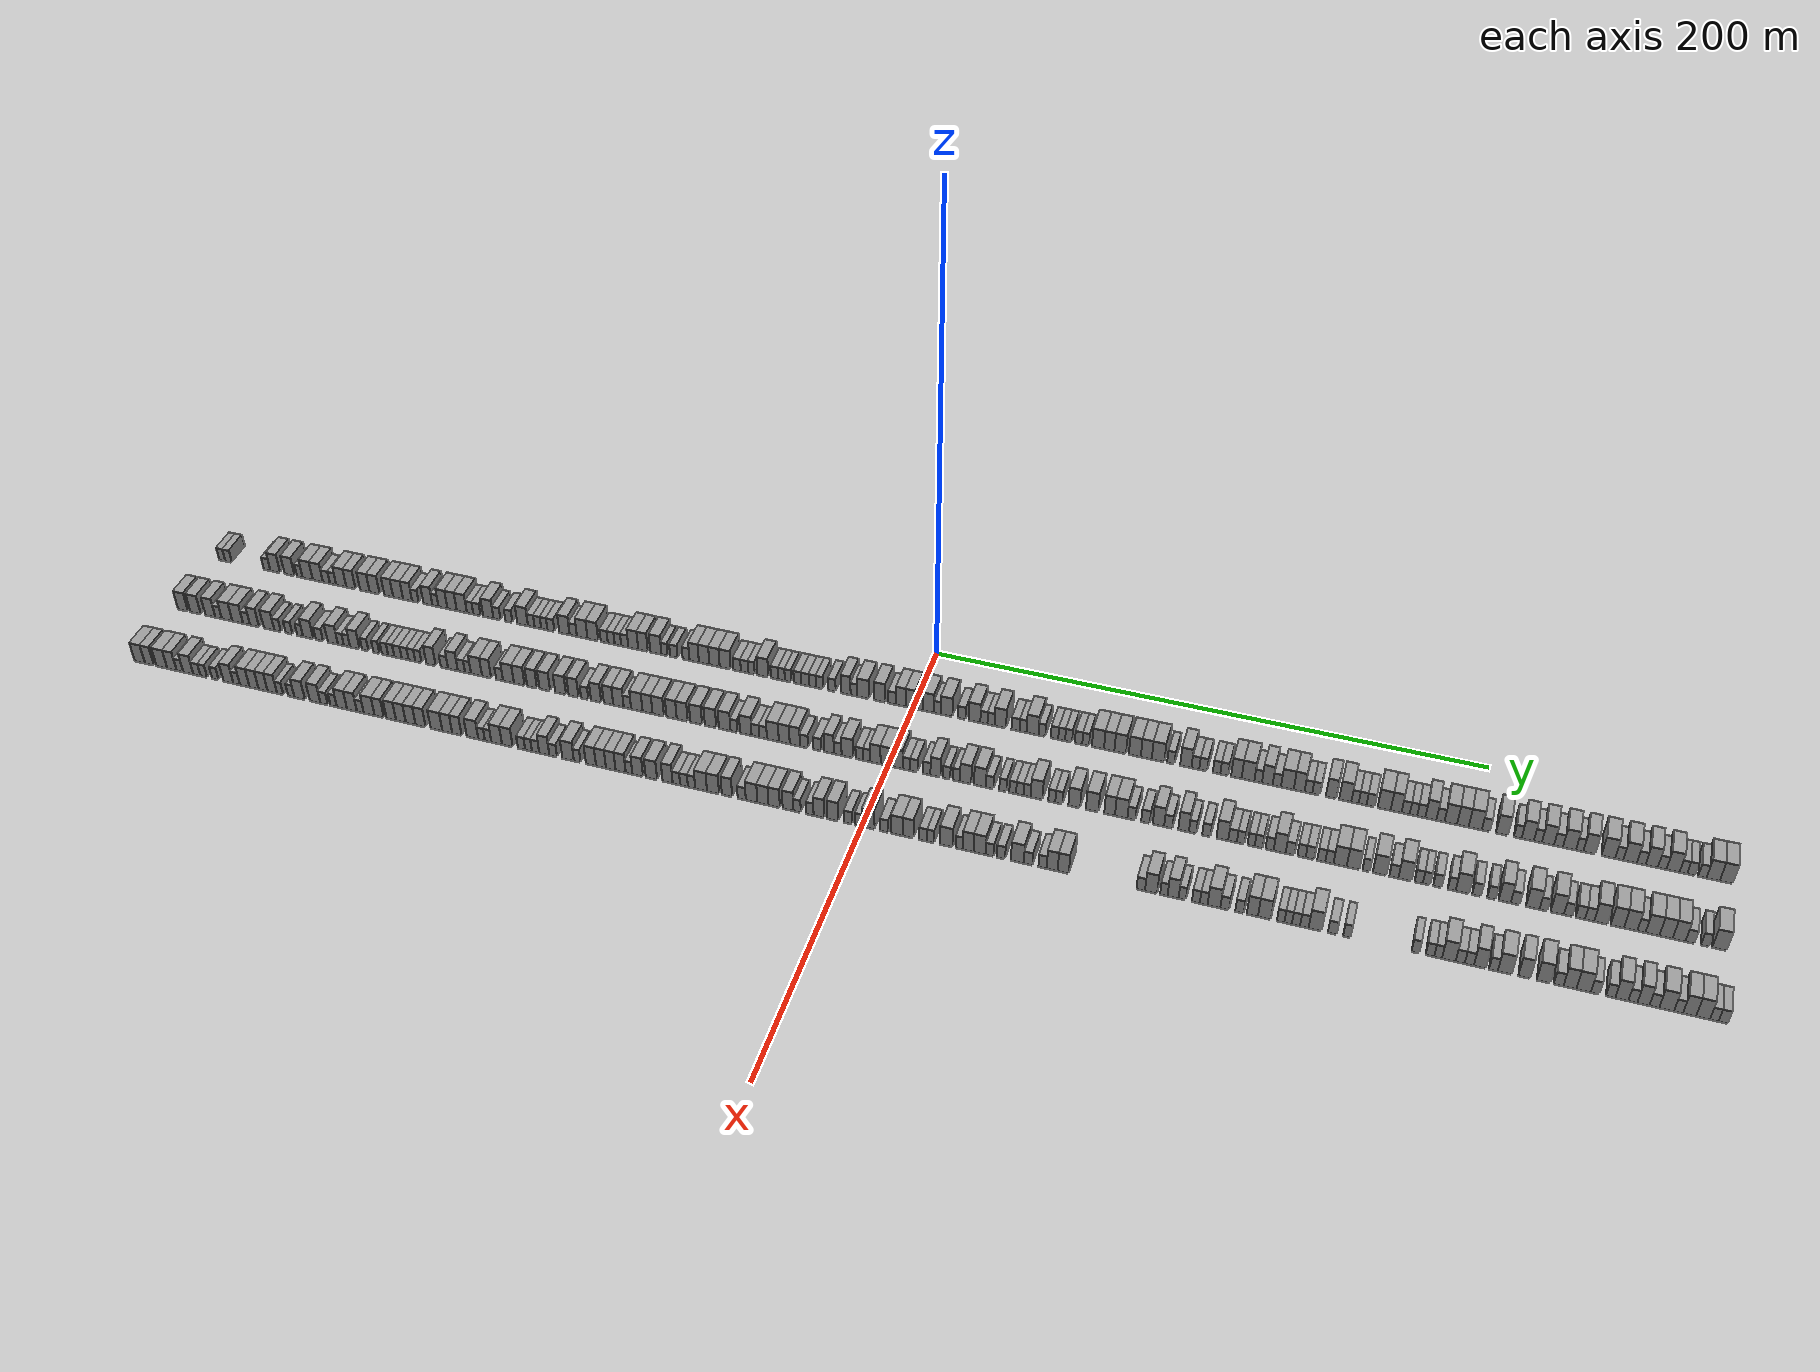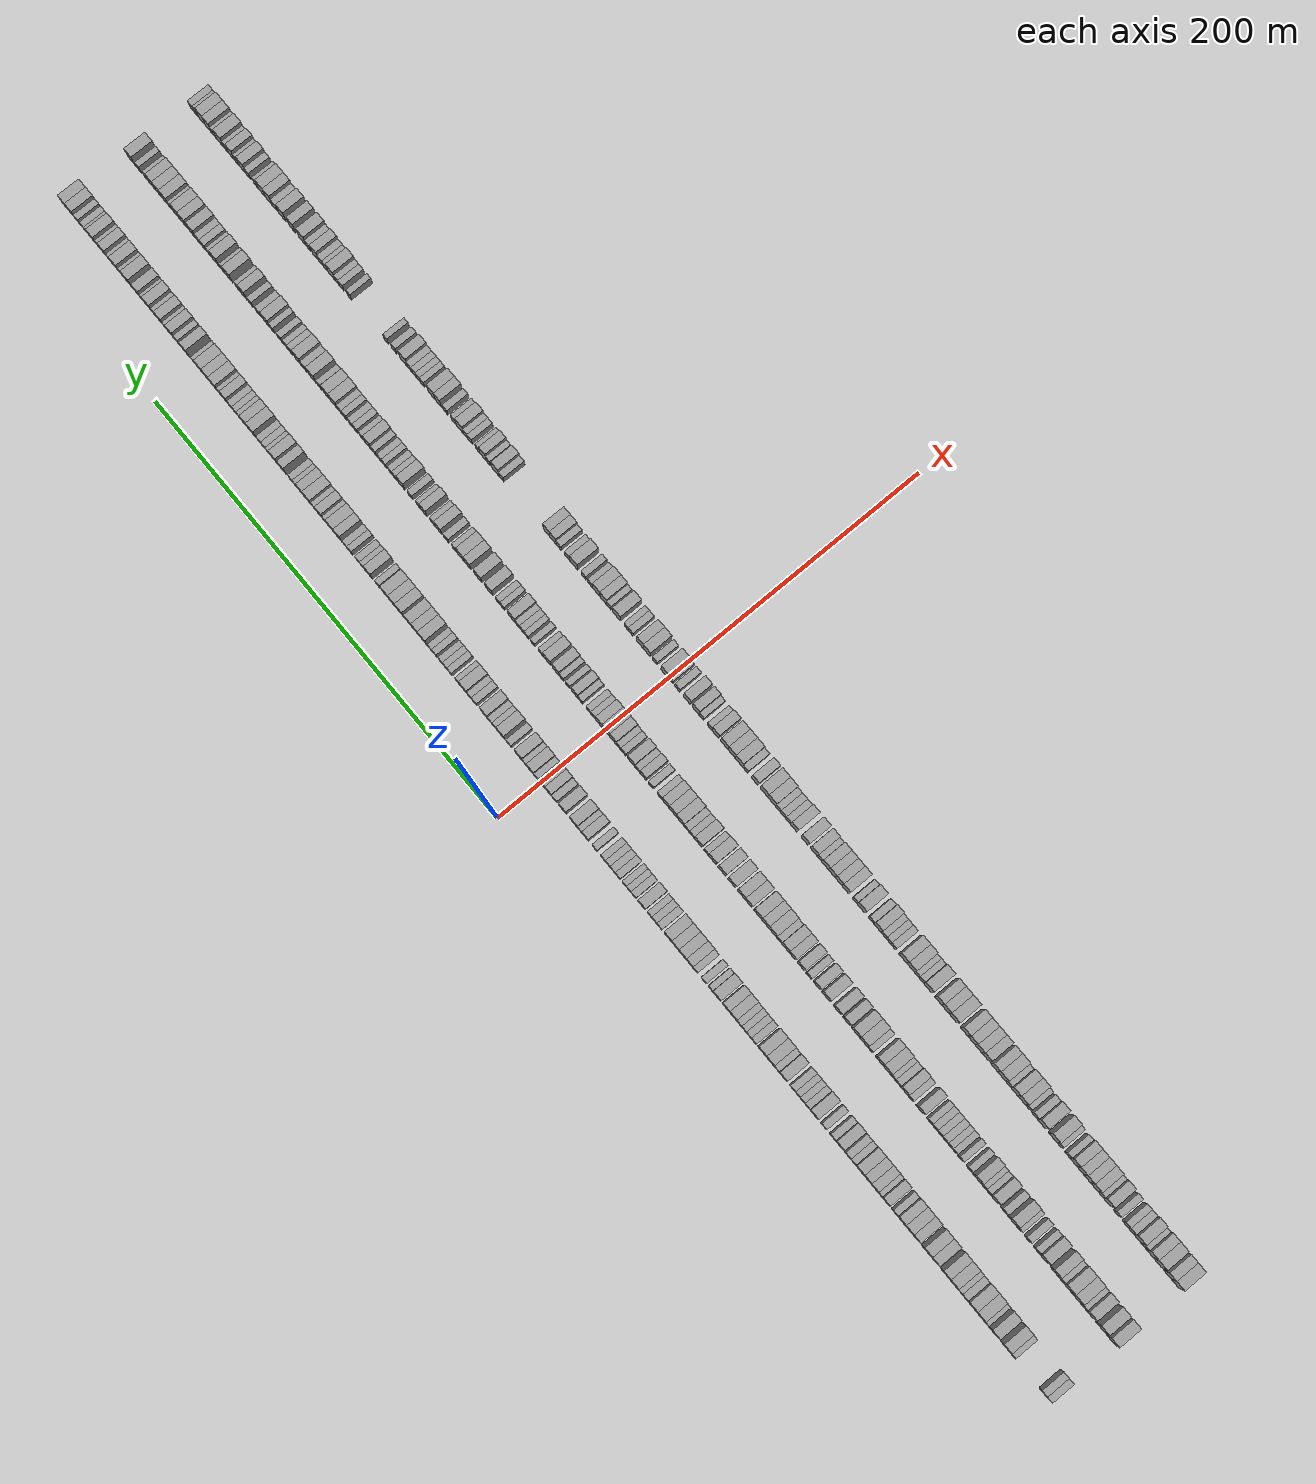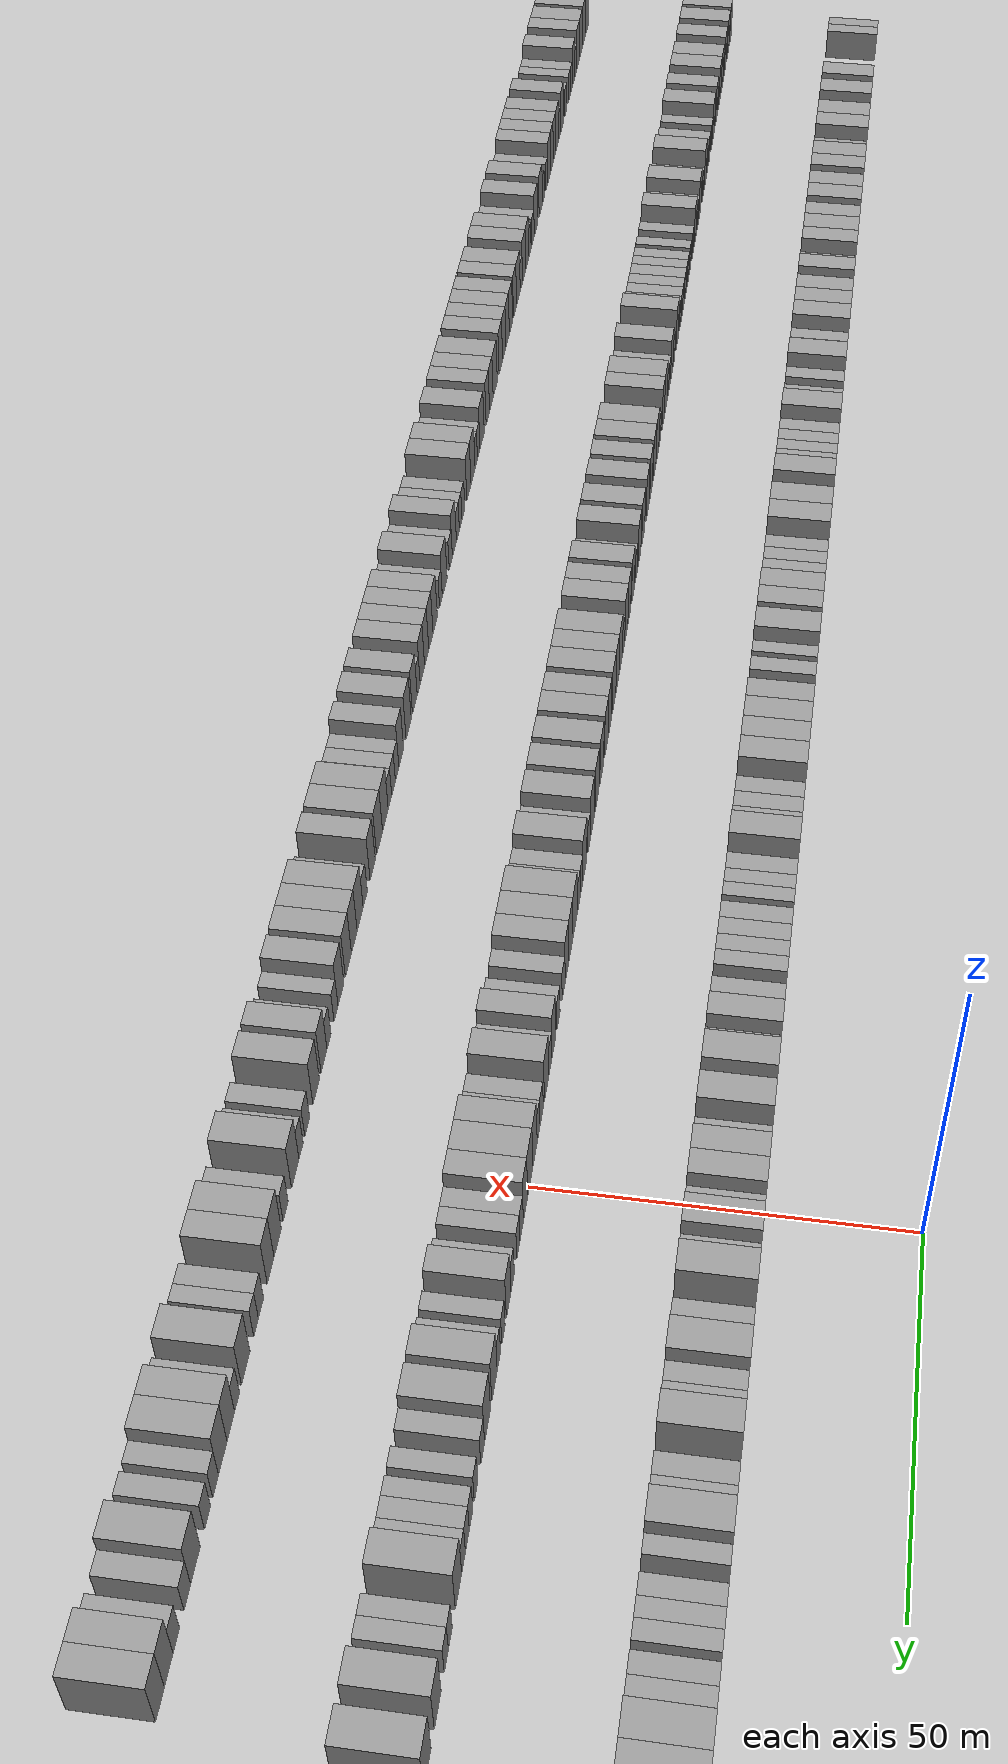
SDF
<sdf version="1.6">
 <world name="default">
  <scene>
   <sky><clouds><speed>12</speed></clouds></sky>
   <ambient>0.4 0.4 0.4 1</ambient>
   <background>0.7 0.7 0.7 1</background>
   <shadows>1</shadows>
  </scene>
  <gravity>0 0 -9.8066</gravity>
  <magnetic_field>6e-06 2.3e-05 -4.2e-05</magnetic_field>
  <physics default="0" name="default_physics" type="ode">
   <ode>
    <solver>
     <type>quick</type>
     <iters>10</iters>
     <sor>1.0</sor>
     <use_dynamic_moi_rescaling>0</use_dynamic_moi_rescaling>
    </solver>
    <constraints>
     <cfm>0</cfm>
     <erp>0.2</erp>
     <contact_max_correcting_vel>100</contact_max_correcting_vel>
     <contact_surface_layer>0.001</contact_surface_layer>
    </constraints>
   </ode>
   <max_step_size>0.004</max_step_size>
   <real_time_factor>1</real_time_factor>
   <real_time_update_rate>250</real_time_update_rate>
  </physics>
  <light name="sun" type="directional">
   <pose>0 0 10 0 0 0</pose>
   <diffuse>0.8 0.8 0.8 1</diffuse>
   <specular>0.2 0.2 0.2 1</specular>
   <attenuation>
    <range>1000</range>
    <constant>0.9</constant>
    <linear>0.01</linear>
    <quadratic>0.001</quadratic>
   </attenuation>
   <direction>-0.5 0.1 -0.9</direction>
  </light>
  <model name="building_1">
   <static>1</static>
   <pose>25.0000 -278.6719 0 0.000000 0.000000 0.000000</pose>
   <link name="link">
    <pose>0 0 3.00 0 0 0</pose>
    <collision name="collision"><geometry><box><size>10.0000 2.6562 6.0000</size></box></geometry></collision>
    <visual name="visual">
     <cast_shadows>0</cast_shadows>
     <geometry><box><size>10.0000 2.6562 6.0000</size></box></geometry>
     <material>
      <script>
       <uri>model://grey_wall/materials/scripts</uri>
       <uri>model://grey_wall/materials/textures</uri>
       <name>vrc/grey_wall</name>
      </script>
     </material>
    </visual>
   </link>
  </model>
  <model name="building_2">
   <static>1</static>
   <pose>25.0000 -275.9168 0 0.000000 0.000000 0.000000</pose>
   <link name="link">
    <pose>0 0 3.00 0 0 0</pose>
    <collision name="collision"><geometry><box><size>10.0000 2.8541 6.0000</size></box></geometry></collision>
    <visual name="visual">
     <cast_shadows>0</cast_shadows>
     <geometry><box><size>10.0000 2.8541 6.0000</size></box></geometry>
     <material>
      <script>
       <uri>model://grey_wall/materials/scripts</uri>
       <uri>model://grey_wall/materials/textures</uri>
       <name>vrc/grey_wall</name>
      </script>
     </material>
    </visual>
   </link>
  </model>
  <model name="building_3">
   <static>1</static>
   <pose>25.0000 -259.2466 0 0.000000 0.000000 0.000000</pose>
   <link name="link">
    <pose>0 0 3.00 0 0 0</pose>
    <collision name="collision"><geometry><box><size>10.0000 2.8287 6.0000</size></box></geometry></collision>
    <visual name="visual">
     <cast_shadows>0</cast_shadows>
     <geometry><box><size>10.0000 2.8287 6.0000</size></box></geometry>
     <material>
      <script>
       <uri>model://grey_wall/materials/scripts</uri>
       <uri>model://grey_wall/materials/textures</uri>
       <name>vrc/grey_wall</name>
      </script>
     </material>
    </visual>
   </link>
  </model>
  <model name="building_4">
   <static>1</static>
   <pose>25.0000 -255.7663 0 0.000000 0.000000 0.000000</pose>
   <link name="link">
    <pose>0 0 4.50 0 0 0</pose>
    <collision name="collision"><geometry><box><size>10.0000 4.1318 9.0000</size></box></geometry></collision>
    <visual name="visual">
     <cast_shadows>0</cast_shadows>
     <geometry><box><size>10.0000 4.1318 9.0000</size></box></geometry>
     <material>
      <script>
       <uri>model://grey_wall/materials/scripts</uri>
       <uri>model://grey_wall/materials/textures</uri>
       <name>vrc/grey_wall</name>
      </script>
     </material>
    </visual>
   </link>
  </model>
  <model name="building_5">
   <static>1</static>
   <pose>25.0000 -249.5898 0 0.000000 0.000000 0.000000</pose>
   <link name="link">
    <pose>0 0 4.50 0 0 0</pose>
    <collision name="collision"><geometry><box><size>10.0000 4.2212 9.0000</size></box></geometry></collision>
    <visual name="visual">
     <cast_shadows>0</cast_shadows>
     <geometry><box><size>10.0000 4.2212 9.0000</size></box></geometry>
     <material>
      <script>
       <uri>model://grey_wall/materials/scripts</uri>
       <uri>model://grey_wall/materials/textures</uri>
       <name>vrc/grey_wall</name>
      </script>
     </material>
    </visual>
   </link>
  </model>
  <model name="building_6">
   <static>1</static>
   <pose>25.0000 -245.2765 0 0.000000 0.000000 0.000000</pose>
   <link name="link">
    <pose>0 0 3.00 0 0 0</pose>
    <collision name="collision"><geometry><box><size>10.0000 2.4053 6.0000</size></box></geometry></collision>
    <visual name="visual">
     <cast_shadows>0</cast_shadows>
     <geometry><box><size>10.0000 2.4053 6.0000</size></box></geometry>
     <material>
      <script>
       <uri>model://grey_wall/materials/scripts</uri>
       <uri>model://grey_wall/materials/textures</uri>
       <name>vrc/grey_wall</name>
      </script>
     </material>
    </visual>
   </link>
  </model>
  <model name="building_7">
   <static>1</static>
   <pose>25.0000 -241.8854 0 0.000000 0.000000 0.000000</pose>
   <link name="link">
    <pose>0 0 4.50 0 0 0</pose>
    <collision name="collision"><geometry><box><size>10.0000 4.3769 9.0000</size></box></geometry></collision>
    <visual name="visual">
     <cast_shadows>0</cast_shadows>
     <geometry><box><size>10.0000 4.3769 9.0000</size></box></geometry>
     <material>
      <script>
       <uri>model://grey_wall/materials/scripts</uri>
       <uri>model://grey_wall/materials/textures</uri>
       <name>vrc/grey_wall</name>
      </script>
     </material>
    </visual>
   </link>
  </model>
  <model name="building_8">
   <static>1</static>
   <pose>25.0000 -237.5531 0 0.000000 0.000000 0.000000</pose>
   <link name="link">
    <pose>0 0 4.50 0 0 0</pose>
    <collision name="collision"><geometry><box><size>10.0000 4.2877 9.0000</size></box></geometry></collision>
    <visual name="visual">
     <cast_shadows>0</cast_shadows>
     <geometry><box><size>10.0000 4.2877 9.0000</size></box></geometry>
     <material>
      <script>
       <uri>model://grey_wall/materials/scripts</uri>
       <uri>model://grey_wall/materials/textures</uri>
       <name>vrc/grey_wall</name>
      </script>
     </material>
    </visual>
   </link>
  </model>
  <model name="building_9">
   <static>1</static>
   <pose>25.0000 -233.9128 0 0.000000 0.000000 0.000000</pose>
   <link name="link">
    <pose>0 0 3.00 0 0 0</pose>
    <collision name="collision"><geometry><box><size>10.0000 2.9928 6.0000</size></box></geometry></collision>
    <visual name="visual">
     <cast_shadows>0</cast_shadows>
     <geometry><box><size>10.0000 2.9928 6.0000</size></box></geometry>
     <material>
      <script>
       <uri>model://grey_wall/materials/scripts</uri>
       <uri>model://grey_wall/materials/textures</uri>
       <name>vrc/grey_wall</name>
      </script>
     </material>
    </visual>
   </link>
  </model>
  <model name="building_10">
   <static>1</static>
   <pose>25.0000 -231.0896 0 0.000000 0.000000 0.000000</pose>
   <link name="link">
    <pose>0 0 3.00 0 0 0</pose>
    <collision name="collision"><geometry><box><size>10.0000 2.6537 6.0000</size></box></geometry></collision>
    <visual name="visual">
     <cast_shadows>0</cast_shadows>
     <geometry><box><size>10.0000 2.6537 6.0000</size></box></geometry>
     <material>
      <script>
       <uri>model://grey_wall/materials/scripts</uri>
       <uri>model://grey_wall/materials/textures</uri>
       <name>vrc/grey_wall</name>
      </script>
     </material>
    </visual>
   </link>
  </model>
  <model name="building_11">
   <static>1</static>
   <pose>25.0000 -227.6349 0 0.000000 0.000000 0.000000</pose>
   <link name="link">
    <pose>0 0 4.50 0 0 0</pose>
    <collision name="collision"><geometry><box><size>10.0000 4.2556 9.0000</size></box></geometry></collision>
    <visual name="visual">
     <cast_shadows>0</cast_shadows>
     <geometry><box><size>10.0000 4.2556 9.0000</size></box></geometry>
     <material>
      <script>
       <uri>model://grey_wall/materials/scripts</uri>
       <uri>model://grey_wall/materials/textures</uri>
       <name>vrc/grey_wall</name>
      </script>
     </material>
    </visual>
   </link>
  </model>
  <model name="building_12">
   <static>1</static>
   <pose>25.0000 -223.5689 0 0.000000 0.000000 0.000000</pose>
   <link name="link">
    <pose>0 0 4.50 0 0 0</pose>
    <collision name="collision"><geometry><box><size>10.0000 3.8763 9.0000</size></box></geometry></collision>
    <visual name="visual">
     <cast_shadows>0</cast_shadows>
     <geometry><box><size>10.0000 3.8763 9.0000</size></box></geometry>
     <material>
      <script>
       <uri>model://grey_wall/materials/scripts</uri>
       <uri>model://grey_wall/materials/textures</uri>
       <name>vrc/grey_wall</name>
      </script>
     </material>
    </visual>
   </link>
  </model>
  <model name="building_13">
   <static>1</static>
   <pose>25.0000 -217.6394 0 0.000000 0.000000 0.000000</pose>
   <link name="link">
    <pose>0 0 4.50 0 0 0</pose>
    <collision name="collision"><geometry><box><size>10.0000 3.9828 9.0000</size></box></geometry></collision>
    <visual name="visual">
     <cast_shadows>0</cast_shadows>
     <geometry><box><size>10.0000 3.9828 9.0000</size></box></geometry>
     <material>
      <script>
       <uri>model://grey_wall/materials/scripts</uri>
       <uri>model://grey_wall/materials/textures</uri>
       <name>vrc/grey_wall</name>
      </script>
     </material>
    </visual>
   </link>
  </model>
  <model name="building_14">
   <static>1</static>
   <pose>25.0000 -213.5491 0 0.000000 0.000000 0.000000</pose>
   <link name="link">
    <pose>0 0 4.50 0 0 0</pose>
    <collision name="collision"><geometry><box><size>10.0000 4.1977 9.0000</size></box></geometry></collision>
    <visual name="visual">
     <cast_shadows>0</cast_shadows>
     <geometry><box><size>10.0000 4.1977 9.0000</size></box></geometry>
     <material>
      <script>
       <uri>model://grey_wall/materials/scripts</uri>
       <uri>model://grey_wall/materials/textures</uri>
       <name>vrc/grey_wall</name>
      </script>
     </material>
    </visual>
   </link>
  </model>
  <model name="building_15">
   <static>1</static>
   <pose>25.0000 -207.6139 0 0.000000 0.000000 0.000000</pose>
   <link name="link">
    <pose>0 0 4.50 0 0 0</pose>
    <collision name="collision"><geometry><box><size>10.0000 3.6728 9.0000</size></box></geometry></collision>
    <visual name="visual">
     <cast_shadows>0</cast_shadows>
     <geometry><box><size>10.0000 3.6728 9.0000</size></box></geometry>
     <material>
      <script>
       <uri>model://grey_wall/materials/scripts</uri>
       <uri>model://grey_wall/materials/textures</uri>
       <name>vrc/grey_wall</name>
      </script>
     </material>
    </visual>
   </link>
  </model>
  <model name="building_16">
   <static>1</static>
   <pose>25.0000 -203.6888 0 0.000000 0.000000 0.000000</pose>
   <link name="link">
    <pose>0 0 4.50 0 0 0</pose>
    <collision name="collision"><geometry><box><size>10.0000 4.1775 9.0000</size></box></geometry></collision>
    <visual name="visual">
     <cast_shadows>0</cast_shadows>
     <geometry><box><size>10.0000 4.1775 9.0000</size></box></geometry>
     <material>
      <script>
       <uri>model://grey_wall/materials/scripts</uri>
       <uri>model://grey_wall/materials/textures</uri>
       <name>vrc/grey_wall</name>
      </script>
     </material>
    </visual>
   </link>
  </model>
  <model name="building_17">
   <static>1</static>
   <pose>25.0000 -199.7320 0 0.000000 0.000000 0.000000</pose>
   <link name="link">
    <pose>0 0 4.50 0 0 0</pose>
    <collision name="collision"><geometry><box><size>10.0000 3.7362 9.0000</size></box></geometry></collision>
    <visual name="visual">
     <cast_shadows>0</cast_shadows>
     <geometry><box><size>10.0000 3.7362 9.0000</size></box></geometry>
     <material>
      <script>
       <uri>model://grey_wall/materials/scripts</uri>
       <uri>model://grey_wall/materials/textures</uri>
       <name>vrc/grey_wall</name>
      </script>
     </material>
    </visual>
   </link>
  </model>
  <model name="building_18">
   <static>1</static>
   <pose>25.0000 -196.5083 0 0.000000 0.000000 0.000000</pose>
   <link name="link">
    <pose>0 0 3.00 0 0 0</pose>
    <collision name="collision"><geometry><box><size>10.0000 2.7112 6.0000</size></box></geometry></collision>
    <visual name="visual">
     <cast_shadows>0</cast_shadows>
     <geometry><box><size>10.0000 2.7112 6.0000</size></box></geometry>
     <material>
      <script>
       <uri>model://grey_wall/materials/scripts</uri>
       <uri>model://grey_wall/materials/textures</uri>
       <name>vrc/grey_wall</name>
      </script>
     </material>
    </visual>
   </link>
  </model>
  <model name="building_19">
   <static>1</static>
   <pose>25.0000 -191.2701 0 0.000000 0.000000 0.000000</pose>
   <link name="link">
    <pose>0 0 4.50 0 0 0</pose>
    <collision name="collision"><geometry><box><size>10.0000 3.7651 9.0000</size></box></geometry></collision>
    <visual name="visual">
     <cast_shadows>0</cast_shadows>
     <geometry><box><size>10.0000 3.7651 9.0000</size></box></geometry>
     <material>
      <script>
       <uri>model://grey_wall/materials/scripts</uri>
       <uri>model://grey_wall/materials/textures</uri>
       <name>vrc/grey_wall</name>
      </script>
     </material>
    </visual>
   </link>
  </model>
  <model name="building_20">
   <static>1</static>
   <pose>25.0000 -188.1491 0 0.000000 0.000000 0.000000</pose>
   <link name="link">
    <pose>0 0 3.00 0 0 0</pose>
    <collision name="collision"><geometry><box><size>10.0000 2.4771 6.0000</size></box></geometry></collision>
    <visual name="visual">
     <cast_shadows>0</cast_shadows>
     <geometry><box><size>10.0000 2.4771 6.0000</size></box></geometry>
     <material>
      <script>
       <uri>model://grey_wall/materials/scripts</uri>
       <uri>model://grey_wall/materials/textures</uri>
       <name>vrc/grey_wall</name>
      </script>
     </material>
    </visual>
   </link>
  </model>
  <model name="building_21">
   <static>1</static>
   <pose>25.0000 -185.0525 0 0.000000 0.000000 0.000000</pose>
   <link name="link">
    <pose>0 0 4.50 0 0 0</pose>
    <collision name="collision"><geometry><box><size>10.0000 3.7161 9.0000</size></box></geometry></collision>
    <visual name="visual">
     <cast_shadows>0</cast_shadows>
     <geometry><box><size>10.0000 3.7161 9.0000</size></box></geometry>
     <material>
      <script>
       <uri>model://grey_wall/materials/scripts</uri>
       <uri>model://grey_wall/materials/textures</uri>
       <name>vrc/grey_wall</name>
      </script>
     </material>
    </visual>
   </link>
  </model>
  <model name="building_22">
   <static>1</static>
   <pose>25.0000 -181.2812 0 0.000000 0.000000 0.000000</pose>
   <link name="link">
    <pose>0 0 4.50 0 0 0</pose>
    <collision name="collision"><geometry><box><size>10.0000 3.8265 9.0000</size></box></geometry></collision>
    <visual name="visual">
     <cast_shadows>0</cast_shadows>
     <geometry><box><size>10.0000 3.8265 9.0000</size></box></geometry>
     <material>
      <script>
       <uri>model://grey_wall/materials/scripts</uri>
       <uri>model://grey_wall/materials/textures</uri>
       <name>vrc/grey_wall</name>
      </script>
     </material>
    </visual>
   </link>
  </model>
  <model name="building_23">
   <static>1</static>
   <pose>25.0000 -177.2653 0 0.000000 0.000000 0.000000</pose>
   <link name="link">
    <pose>0 0 4.50 0 0 0</pose>
    <collision name="collision"><geometry><box><size>10.0000 4.2051 9.0000</size></box></geometry></collision>
    <visual name="visual">
     <cast_shadows>0</cast_shadows>
     <geometry><box><size>10.0000 4.2051 9.0000</size></box></geometry>
     <material>
      <script>
       <uri>model://grey_wall/materials/scripts</uri>
       <uri>model://grey_wall/materials/textures</uri>
       <name>vrc/grey_wall</name>
      </script>
     </material>
    </visual>
   </link>
  </model>
  <model name="building_24">
   <static>1</static>
   <pose>25.0000 -173.8344 0 0.000000 0.000000 0.000000</pose>
   <link name="link">
    <pose>0 0 3.00 0 0 0</pose>
    <collision name="collision"><geometry><box><size>10.0000 2.6567 6.0000</size></box></geometry></collision>
    <visual name="visual">
     <cast_shadows>0</cast_shadows>
     <geometry><box><size>10.0000 2.6567 6.0000</size></box></geometry>
     <material>
      <script>
       <uri>model://grey_wall/materials/scripts</uri>
       <uri>model://grey_wall/materials/textures</uri>
       <name>vrc/grey_wall</name>
      </script>
     </material>
    </visual>
   </link>
  </model>
  <model name="building_25">
   <static>1</static>
   <pose>25.0000 -171.0169 0 0.000000 0.000000 0.000000</pose>
   <link name="link">
    <pose>0 0 3.00 0 0 0</pose>
    <collision name="collision"><geometry><box><size>10.0000 2.9782 6.0000</size></box></geometry></collision>
    <visual name="visual">
     <cast_shadows>0</cast_shadows>
     <geometry><box><size>10.0000 2.9782 6.0000</size></box></geometry>
     <material>
      <script>
       <uri>model://grey_wall/materials/scripts</uri>
       <uri>model://grey_wall/materials/textures</uri>
       <name>vrc/grey_wall</name>
      </script>
     </material>
    </visual>
   </link>
  </model>
  <model name="building_26">
   <static>1</static>
   <pose>25.0000 -166.3937 0 0.000000 0.000000 0.000000</pose>
   <link name="link">
    <pose>0 0 4.50 0 0 0</pose>
    <collision name="collision"><geometry><box><size>10.0000 4.2682 9.0000</size></box></geometry></collision>
    <visual name="visual">
     <cast_shadows>0</cast_shadows>
     <geometry><box><size>10.0000 4.2682 9.0000</size></box></geometry>
     <material>
      <script>
       <uri>model://grey_wall/materials/scripts</uri>
       <uri>model://grey_wall/materials/textures</uri>
       <name>vrc/grey_wall</name>
      </script>
     </material>
    </visual>
   </link>
  </model>
  <model name="building_27">
   <static>1</static>
   <pose>25.0000 -162.8263 0 0.000000 0.000000 0.000000</pose>
   <link name="link">
    <pose>0 0 3.00 0 0 0</pose>
    <collision name="collision"><geometry><box><size>10.0000 2.8666 6.0000</size></box></geometry></collision>
    <visual name="visual">
     <cast_shadows>0</cast_shadows>
     <geometry><box><size>10.0000 2.8666 6.0000</size></box></geometry>
     <material>
      <script>
       <uri>model://grey_wall/materials/scripts</uri>
       <uri>model://grey_wall/materials/textures</uri>
       <name>vrc/grey_wall</name>
      </script>
     </material>
    </visual>
   </link>
  </model>
  <model name="building_28">
   <static>1</static>
   <pose>25.0000 -157.9674 0 0.000000 0.000000 0.000000</pose>
   <link name="link">
    <pose>0 0 3.00 0 0 0</pose>
    <collision name="collision"><geometry><box><size>10.0000 2.8514 6.0000</size></box></geometry></collision>
    <visual name="visual">
     <cast_shadows>0</cast_shadows>
     <geometry><box><size>10.0000 2.8514 6.0000</size></box></geometry>
     <material>
      <script>
       <uri>model://grey_wall/materials/scripts</uri>
       <uri>model://grey_wall/materials/textures</uri>
       <name>vrc/grey_wall</name>
      </script>
     </material>
    </visual>
   </link>
  </model>
  <model name="building_29">
   <static>1</static>
   <pose>25.0000 -152.3742 0 0.000000 0.000000 0.000000</pose>
   <link name="link">
    <pose>0 0 4.50 0 0 0</pose>
    <collision name="collision"><geometry><box><size>10.0000 4.3349 9.0000</size></box></geometry></collision>
    <visual name="visual">
     <cast_shadows>0</cast_shadows>
     <geometry><box><size>10.0000 4.3349 9.0000</size></box></geometry>
     <material>
      <script>
       <uri>model://grey_wall/materials/scripts</uri>
       <uri>model://grey_wall/materials/textures</uri>
       <name>vrc/grey_wall</name>
      </script>
     </material>
    </visual>
   </link>
  </model>
  <model name="building_30">
   <static>1</static>
   <pose>25.0000 -148.8519 0 0.000000 0.000000 0.000000</pose>
   <link name="link">
    <pose>0 0 3.00 0 0 0</pose>
    <collision name="collision"><geometry><box><size>10.0000 2.7098 6.0000</size></box></geometry></collision>
    <visual name="visual">
     <cast_shadows>0</cast_shadows>
     <geometry><box><size>10.0000 2.7098 6.0000</size></box></geometry>
     <material>
      <script>
       <uri>model://grey_wall/materials/scripts</uri>
       <uri>model://grey_wall/materials/textures</uri>
       <name>vrc/grey_wall</name>
      </script>
     </material>
    </visual>
   </link>
  </model>
  <model name="building_31">
   <static>1</static>
   <pose>25.0000 -146.1571 0 0.000000 0.000000 0.000000</pose>
   <link name="link">
    <pose>0 0 3.00 0 0 0</pose>
    <collision name="collision"><geometry><box><size>10.0000 2.6797 6.0000</size></box></geometry></collision>
    <visual name="visual">
     <cast_shadows>0</cast_shadows>
     <geometry><box><size>10.0000 2.6797 6.0000</size></box></geometry>
     <material>
      <script>
       <uri>model://grey_wall/materials/scripts</uri>
       <uri>model://grey_wall/materials/textures</uri>
       <name>vrc/grey_wall</name>
      </script>
     </material>
    </visual>
   </link>
  </model>
  <model name="building_32">
   <static>1</static>
   <pose>25.0000 -143.5729 0 0.000000 0.000000 0.000000</pose>
   <link name="link">
    <pose>0 0 3.00 0 0 0</pose>
    <collision name="collision"><geometry><box><size>10.0000 2.4887 6.0000</size></box></geometry></collision>
    <visual name="visual">
     <cast_shadows>0</cast_shadows>
     <geometry><box><size>10.0000 2.4887 6.0000</size></box></geometry>
     <material>
      <script>
       <uri>model://grey_wall/materials/scripts</uri>
       <uri>model://grey_wall/materials/textures</uri>
       <name>vrc/grey_wall</name>
      </script>
     </material>
    </visual>
   </link>
  </model>
  <model name="building_33">
   <static>1</static>
   <pose>25.0000 -140.9123 0 0.000000 0.000000 0.000000</pose>
   <link name="link">
    <pose>0 0 3.00 0 0 0</pose>
    <collision name="collision"><geometry><box><size>10.0000 2.8326 6.0000</size></box></geometry></collision>
    <visual name="visual">
     <cast_shadows>0</cast_shadows>
     <geometry><box><size>10.0000 2.8326 6.0000</size></box></geometry>
     <material>
      <script>
       <uri>model://grey_wall/materials/scripts</uri>
       <uri>model://grey_wall/materials/textures</uri>
       <name>vrc/grey_wall</name>
      </script>
     </material>
    </visual>
   </link>
  </model>
  <model name="building_34">
   <static>1</static>
   <pose>25.0000 -135.4282 0 0.000000 0.000000 0.000000</pose>
   <link name="link">
    <pose>0 0 4.50 0 0 0</pose>
    <collision name="collision"><geometry><box><size>10.0000 4.1356 9.0000</size></box></geometry></collision>
    <visual name="visual">
     <cast_shadows>0</cast_shadows>
     <geometry><box><size>10.0000 4.1356 9.0000</size></box></geometry>
     <material>
      <script>
       <uri>model://grey_wall/materials/scripts</uri>
       <uri>model://grey_wall/materials/textures</uri>
       <name>vrc/grey_wall</name>
      </script>
     </material>
    </visual>
   </link>
  </model>
  <model name="building_35">
   <static>1</static>
   <pose>25.0000 -131.9099 0 0.000000 0.000000 0.000000</pose>
   <link name="link">
    <pose>0 0 3.00 0 0 0</pose>
    <collision name="collision"><geometry><box><size>10.0000 2.9009 6.0000</size></box></geometry></collision>
    <visual name="visual">
     <cast_shadows>0</cast_shadows>
     <geometry><box><size>10.0000 2.9009 6.0000</size></box></geometry>
     <material>
      <script>
       <uri>model://grey_wall/materials/scripts</uri>
       <uri>model://grey_wall/materials/textures</uri>
       <name>vrc/grey_wall</name>
      </script>
     </material>
    </visual>
   </link>
  </model>
  <model name="building_36">
   <static>1</static>
   <pose>25.0000 -128.3235 0 0.000000 0.000000 0.000000</pose>
   <link name="link">
    <pose>0 0 4.50 0 0 0</pose>
    <collision name="collision"><geometry><box><size>10.0000 4.2720 9.0000</size></box></geometry></collision>
    <visual name="visual">
     <cast_shadows>0</cast_shadows>
     <geometry><box><size>10.0000 4.2720 9.0000</size></box></geometry>
     <material>
      <script>
       <uri>model://grey_wall/materials/scripts</uri>
       <uri>model://grey_wall/materials/textures</uri>
       <name>vrc/grey_wall</name>
      </script>
     </material>
    </visual>
   </link>
  </model>
  <model name="building_37">
   <static>1</static>
   <pose>25.0000 -124.0453 0 0.000000 0.000000 0.000000</pose>
   <link name="link">
    <pose>0 0 4.50 0 0 0</pose>
    <collision name="collision"><geometry><box><size>10.0000 4.2843 9.0000</size></box></geometry></collision>
    <visual name="visual">
     <cast_shadows>0</cast_shadows>
     <geometry><box><size>10.0000 4.2843 9.0000</size></box></geometry>
     <material>
      <script>
       <uri>model://grey_wall/materials/scripts</uri>
       <uri>model://grey_wall/materials/textures</uri>
       <name>vrc/grey_wall</name>
      </script>
     </material>
    </visual>
   </link>
  </model>
  <model name="building_38">
   <static>1</static>
   <pose>25.0000 -119.4989 0 0.000000 0.000000 0.000000</pose>
   <link name="link">
    <pose>0 0 3.00 0 0 0</pose>
    <collision name="collision"><geometry><box><size>10.0000 2.8086 6.0000</size></box></geometry></collision>
    <visual name="visual">
     <cast_shadows>0</cast_shadows>
     <geometry><box><size>10.0000 2.8086 6.0000</size></box></geometry>
     <material>
      <script>
       <uri>model://grey_wall/materials/scripts</uri>
       <uri>model://grey_wall/materials/textures</uri>
       <name>vrc/grey_wall</name>
      </script>
     </material>
    </visual>
   </link>
  </model>
  <model name="building_39">
   <static>1</static>
   <pose>25.0000 -116.7189 0 0.000000 0.000000 0.000000</pose>
   <link name="link">
    <pose>0 0 3.00 0 0 0</pose>
    <collision name="collision"><geometry><box><size>10.0000 2.7514 6.0000</size></box></geometry></collision>
    <visual name="visual">
     <cast_shadows>0</cast_shadows>
     <geometry><box><size>10.0000 2.7514 6.0000</size></box></geometry>
     <material>
      <script>
       <uri>model://grey_wall/materials/scripts</uri>
       <uri>model://grey_wall/materials/textures</uri>
       <name>vrc/grey_wall</name>
      </script>
     </material>
    </visual>
   </link>
  </model>
  <model name="building_40">
   <static>1</static>
   <pose>25.0000 -114.0413 0 0.000000 0.000000 0.000000</pose>
   <link name="link">
    <pose>0 0 3.00 0 0 0</pose>
    <collision name="collision"><geometry><box><size>10.0000 2.6038 6.0000</size></box></geometry></collision>
    <visual name="visual">
     <cast_shadows>0</cast_shadows>
     <geometry><box><size>10.0000 2.6038 6.0000</size></box></geometry>
     <material>
      <script>
       <uri>model://grey_wall/materials/scripts</uri>
       <uri>model://grey_wall/materials/textures</uri>
       <name>vrc/grey_wall</name>
      </script>
     </material>
    </visual>
   </link>
  </model>
  <model name="building_41">
   <static>1</static>
   <pose>25.0000 -111.3283 0 0.000000 0.000000 0.000000</pose>
   <link name="link">
    <pose>0 0 3.00 0 0 0</pose>
    <collision name="collision"><geometry><box><size>10.0000 2.8221 6.0000</size></box></geometry></collision>
    <visual name="visual">
     <cast_shadows>0</cast_shadows>
     <geometry><box><size>10.0000 2.8221 6.0000</size></box></geometry>
     <material>
      <script>
       <uri>model://grey_wall/materials/scripts</uri>
       <uri>model://grey_wall/materials/textures</uri>
       <name>vrc/grey_wall</name>
      </script>
     </material>
    </visual>
   </link>
  </model>
  <model name="building_42">
   <static>1</static>
   <pose>25.0000 -107.9474 0 0.000000 0.000000 0.000000</pose>
   <link name="link">
    <pose>0 0 4.50 0 0 0</pose>
    <collision name="collision"><geometry><box><size>10.0000 3.9398 9.0000</size></box></geometry></collision>
    <visual name="visual">
     <cast_shadows>0</cast_shadows>
     <geometry><box><size>10.0000 3.9398 9.0000</size></box></geometry>
     <material>
      <script>
       <uri>model://grey_wall/materials/scripts</uri>
       <uri>model://grey_wall/materials/textures</uri>
       <name>vrc/grey_wall</name>
      </script>
     </material>
    </visual>
   </link>
  </model>
  <model name="building_43">
   <static>1</static>
   <pose>25.0000 -104.0791 0 0.000000 0.000000 0.000000</pose>
   <link name="link">
    <pose>0 0 4.50 0 0 0</pose>
    <collision name="collision"><geometry><box><size>10.0000 3.7968 9.0000</size></box></geometry></collision>
    <visual name="visual">
     <cast_shadows>0</cast_shadows>
     <geometry><box><size>10.0000 3.7968 9.0000</size></box></geometry>
     <material>
      <script>
       <uri>model://grey_wall/materials/scripts</uri>
       <uri>model://grey_wall/materials/textures</uri>
       <name>vrc/grey_wall</name>
      </script>
     </material>
    </visual>
   </link>
  </model>
  <model name="building_44">
   <static>1</static>
   <pose>25.0000 -98.9828 0 0.000000 0.000000 0.000000</pose>
   <link name="link">
    <pose>0 0 4.50 0 0 0</pose>
    <collision name="collision"><geometry><box><size>10.0000 4.3958 9.0000</size></box></geometry></collision>
    <visual name="visual">
     <cast_shadows>0</cast_shadows>
     <geometry><box><size>10.0000 4.3958 9.0000</size></box></geometry>
     <material>
      <script>
       <uri>model://grey_wall/materials/scripts</uri>
       <uri>model://grey_wall/materials/textures</uri>
       <name>vrc/grey_wall</name>
      </script>
     </material>
    </visual>
   </link>
  </model>
  <model name="building_45">
   <static>1</static>
   <pose>25.0000 -95.5806 0 0.000000 0.000000 0.000000</pose>
   <link name="link">
    <pose>0 0 3.00 0 0 0</pose>
    <collision name="collision"><geometry><box><size>10.0000 2.4086 6.0000</size></box></geometry></collision>
    <visual name="visual">
     <cast_shadows>0</cast_shadows>
     <geometry><box><size>10.0000 2.4086 6.0000</size></box></geometry>
     <material>
      <script>
       <uri>model://grey_wall/materials/scripts</uri>
       <uri>model://grey_wall/materials/textures</uri>
       <name>vrc/grey_wall</name>
      </script>
     </material>
    </visual>
   </link>
  </model>
  <model name="building_46">
   <static>1</static>
   <pose>25.0000 -91.9295 0 0.000000 0.000000 0.000000</pose>
   <link name="link">
    <pose>0 0 3.00 0 0 0</pose>
    <collision name="collision"><geometry><box><size>10.0000 2.8937 6.0000</size></box></geometry></collision>
    <visual name="visual">
     <cast_shadows>0</cast_shadows>
     <geometry><box><size>10.0000 2.8937 6.0000</size></box></geometry>
     <material>
      <script>
       <uri>model://grey_wall/materials/scripts</uri>
       <uri>model://grey_wall/materials/textures</uri>
       <name>vrc/grey_wall</name>
      </script>
     </material>
    </visual>
   </link>
  </model>
  <model name="building_47">
   <static>1</static>
   <pose>25.0000 -87.1205 0 0.000000 0.000000 0.000000</pose>
   <link name="link">
    <pose>0 0 3.00 0 0 0</pose>
    <collision name="collision"><geometry><box><size>10.0000 2.7242 6.0000</size></box></geometry></collision>
    <visual name="visual">
     <cast_shadows>0</cast_shadows>
     <geometry><box><size>10.0000 2.7242 6.0000</size></box></geometry>
     <material>
      <script>
       <uri>model://grey_wall/materials/scripts</uri>
       <uri>model://grey_wall/materials/textures</uri>
       <name>vrc/grey_wall</name>
      </script>
     </material>
    </visual>
   </link>
  </model>
  <model name="building_48">
   <static>1</static>
   <pose>25.0000 -83.9220 0 0.000000 0.000000 0.000000</pose>
   <link name="link">
    <pose>0 0 4.50 0 0 0</pose>
    <collision name="collision"><geometry><box><size>10.0000 3.6729 9.0000</size></box></geometry></collision>
    <visual name="visual">
     <cast_shadows>0</cast_shadows>
     <geometry><box><size>10.0000 3.6729 9.0000</size></box></geometry>
     <material>
      <script>
       <uri>model://grey_wall/materials/scripts</uri>
       <uri>model://grey_wall/materials/textures</uri>
       <name>vrc/grey_wall</name>
      </script>
     </material>
    </visual>
   </link>
  </model>
  <model name="building_49">
   <static>1</static>
   <pose>25.0000 -80.0256 0 0.000000 0.000000 0.000000</pose>
   <link name="link">
    <pose>0 0 4.50 0 0 0</pose>
    <collision name="collision"><geometry><box><size>10.0000 4.1198 9.0000</size></box></geometry></collision>
    <visual name="visual">
     <cast_shadows>0</cast_shadows>
     <geometry><box><size>10.0000 4.1198 9.0000</size></box></geometry>
     <material>
      <script>
       <uri>model://grey_wall/materials/scripts</uri>
       <uri>model://grey_wall/materials/textures</uri>
       <name>vrc/grey_wall</name>
      </script>
     </material>
    </visual>
   </link>
  </model>
  <model name="building_50">
   <static>1</static>
   <pose>25.0000 -75.9775 0 0.000000 0.000000 0.000000</pose>
   <link name="link">
    <pose>0 0 4.50 0 0 0</pose>
    <collision name="collision"><geometry><box><size>10.0000 3.9763 9.0000</size></box></geometry></collision>
    <visual name="visual">
     <cast_shadows>0</cast_shadows>
     <geometry><box><size>10.0000 3.9763 9.0000</size></box></geometry>
     <material>
      <script>
       <uri>model://grey_wall/materials/scripts</uri>
       <uri>model://grey_wall/materials/textures</uri>
       <name>vrc/grey_wall</name>
      </script>
     </material>
    </visual>
   </link>
  </model>
  <model name="building_51">
   <static>1</static>
   <pose>25.0000 -71.8430 0 0.000000 0.000000 0.000000</pose>
   <link name="link">
    <pose>0 0 4.50 0 0 0</pose>
    <collision name="collision"><geometry><box><size>10.0000 4.2927 9.0000</size></box></geometry></collision>
    <visual name="visual">
     <cast_shadows>0</cast_shadows>
     <geometry><box><size>10.0000 4.2927 9.0000</size></box></geometry>
     <material>
      <script>
       <uri>model://grey_wall/materials/scripts</uri>
       <uri>model://grey_wall/materials/textures</uri>
       <name>vrc/grey_wall</name>
      </script>
     </material>
    </visual>
   </link>
  </model>
  <model name="building_52">
   <static>1</static>
   <pose>25.0000 -67.2285 0 0.000000 0.000000 0.000000</pose>
   <link name="link">
    <pose>0 0 3.00 0 0 0</pose>
    <collision name="collision"><geometry><box><size>10.0000 2.9363 6.0000</size></box></geometry></collision>
    <visual name="visual">
     <cast_shadows>0</cast_shadows>
     <geometry><box><size>10.0000 2.9363 6.0000</size></box></geometry>
     <material>
      <script>
       <uri>model://grey_wall/materials/scripts</uri>
       <uri>model://grey_wall/materials/textures</uri>
       <name>vrc/grey_wall</name>
      </script>
     </material>
    </visual>
   </link>
  </model>
  <model name="building_53">
   <static>1</static>
   <pose>25.0000 -64.3253 0 0.000000 0.000000 0.000000</pose>
   <link name="link">
    <pose>0 0 3.00 0 0 0</pose>
    <collision name="collision"><geometry><box><size>10.0000 2.8700 6.0000</size></box></geometry></collision>
    <visual name="visual">
     <cast_shadows>0</cast_shadows>
     <geometry><box><size>10.0000 2.8700 6.0000</size></box></geometry>
     <material>
      <script>
       <uri>model://grey_wall/materials/scripts</uri>
       <uri>model://grey_wall/materials/textures</uri>
       <name>vrc/grey_wall</name>
      </script>
     </material>
    </visual>
   </link>
  </model>
  <model name="building_54">
   <static>1</static>
   <pose>25.0000 -61.6366 0 0.000000 0.000000 0.000000</pose>
   <link name="link">
    <pose>0 0 3.00 0 0 0</pose>
    <collision name="collision"><geometry><box><size>10.0000 2.5075 6.0000</size></box></geometry></collision>
    <visual name="visual">
     <cast_shadows>0</cast_shadows>
     <geometry><box><size>10.0000 2.5075 6.0000</size></box></geometry>
     <material>
      <script>
       <uri>model://grey_wall/materials/scripts</uri>
       <uri>model://grey_wall/materials/textures</uri>
       <name>vrc/grey_wall</name>
      </script>
     </material>
    </visual>
   </link>
  </model>
  <model name="building_55">
   <static>1</static>
   <pose>25.0000 -57.2749 0 0.000000 0.000000 0.000000</pose>
   <link name="link">
    <pose>0 0 4.50 0 0 0</pose>
    <collision name="collision"><geometry><box><size>10.0000 4.2159 9.0000</size></box></geometry></collision>
    <visual name="visual">
     <cast_shadows>0</cast_shadows>
     <geometry><box><size>10.0000 4.2159 9.0000</size></box></geometry>
     <material>
      <script>
       <uri>model://grey_wall/materials/scripts</uri>
       <uri>model://grey_wall/materials/textures</uri>
       <name>vrc/grey_wall</name>
      </script>
     </material>
    </visual>
   </link>
  </model>
  <model name="building_56">
   <static>1</static>
   <pose>25.0000 -52.6987 0 0.000000 0.000000 0.000000</pose>
   <link name="link">
    <pose>0 0 3.00 0 0 0</pose>
    <collision name="collision"><geometry><box><size>10.0000 2.9365 6.0000</size></box></geometry></collision>
    <visual name="visual">
     <cast_shadows>0</cast_shadows>
     <geometry><box><size>10.0000 2.9365 6.0000</size></box></geometry>
     <material>
      <script>
       <uri>model://grey_wall/materials/scripts</uri>
       <uri>model://grey_wall/materials/textures</uri>
       <name>vrc/grey_wall</name>
      </script>
     </material>
    </visual>
   </link>
  </model>
  <model name="building_57">
   <static>1</static>
   <pose>25.0000 -50.0138 0 0.000000 0.000000 0.000000</pose>
   <link name="link">
    <pose>0 0 3.00 0 0 0</pose>
    <collision name="collision"><geometry><box><size>10.0000 2.4333 6.0000</size></box></geometry></collision>
    <visual name="visual">
     <cast_shadows>0</cast_shadows>
     <geometry><box><size>10.0000 2.4333 6.0000</size></box></geometry>
     <material>
      <script>
       <uri>model://grey_wall/materials/scripts</uri>
       <uri>model://grey_wall/materials/textures</uri>
       <name>vrc/grey_wall</name>
      </script>
     </material>
    </visual>
   </link>
  </model>
  <model name="building_58">
   <static>1</static>
   <pose>25.0000 -47.5625 0 0.000000 0.000000 0.000000</pose>
   <link name="link">
    <pose>0 0 3.00 0 0 0</pose>
    <collision name="collision"><geometry><box><size>10.0000 2.4693 6.0000</size></box></geometry></collision>
    <visual name="visual">
     <cast_shadows>0</cast_shadows>
     <geometry><box><size>10.0000 2.4693 6.0000</size></box></geometry>
     <material>
      <script>
       <uri>model://grey_wall/materials/scripts</uri>
       <uri>model://grey_wall/materials/textures</uri>
       <name>vrc/grey_wall</name>
      </script>
     </material>
    </visual>
   </link>
  </model>
  <model name="building_59">
   <static>1</static>
   <pose>25.0000 -43.8836 0 0.000000 0.000000 0.000000</pose>
   <link name="link">
    <pose>0 0 3.00 0 0 0</pose>
    <collision name="collision"><geometry><box><size>10.0000 2.8885 6.0000</size></box></geometry></collision>
    <visual name="visual">
     <cast_shadows>0</cast_shadows>
     <geometry><box><size>10.0000 2.8885 6.0000</size></box></geometry>
     <material>
      <script>
       <uri>model://grey_wall/materials/scripts</uri>
       <uri>model://grey_wall/materials/textures</uri>
       <name>vrc/grey_wall</name>
      </script>
     </material>
    </visual>
   </link>
  </model>
  <model name="building_60">
   <static>1</static>
   <pose>25.0000 -40.9950 0 0.000000 0.000000 0.000000</pose>
   <link name="link">
    <pose>0 0 3.00 0 0 0</pose>
    <collision name="collision"><geometry><box><size>10.0000 2.8887 6.0000</size></box></geometry></collision>
    <visual name="visual">
     <cast_shadows>0</cast_shadows>
     <geometry><box><size>10.0000 2.8887 6.0000</size></box></geometry>
     <material>
      <script>
       <uri>model://grey_wall/materials/scripts</uri>
       <uri>model://grey_wall/materials/textures</uri>
       <name>vrc/grey_wall</name>
      </script>
     </material>
    </visual>
   </link>
  </model>
  <model name="building_61">
   <static>1</static>
   <pose>25.0000 -38.2087 0 0.000000 0.000000 0.000000</pose>
   <link name="link">
    <pose>0 0 3.00 0 0 0</pose>
    <collision name="collision"><geometry><box><size>10.0000 2.6837 6.0000</size></box></geometry></collision>
    <visual name="visual">
     <cast_shadows>0</cast_shadows>
     <geometry><box><size>10.0000 2.6837 6.0000</size></box></geometry>
     <material>
      <script>
       <uri>model://grey_wall/materials/scripts</uri>
       <uri>model://grey_wall/materials/textures</uri>
       <name>vrc/grey_wall</name>
      </script>
     </material>
    </visual>
   </link>
  </model>
  <model name="building_62">
   <static>1</static>
   <pose>25.0000 -35.5522 0 0.000000 0.000000 0.000000</pose>
   <link name="link">
    <pose>0 0 3.00 0 0 0</pose>
    <collision name="collision"><geometry><box><size>10.0000 2.6294 6.0000</size></box></geometry></collision>
    <visual name="visual">
     <cast_shadows>0</cast_shadows>
     <geometry><box><size>10.0000 2.6294 6.0000</size></box></geometry>
     <material>
      <script>
       <uri>model://grey_wall/materials/scripts</uri>
       <uri>model://grey_wall/materials/textures</uri>
       <name>vrc/grey_wall</name>
      </script>
     </material>
    </visual>
   </link>
  </model>
  <model name="building_63">
   <static>1</static>
   <pose>25.0000 -30.8139 0 0.000000 0.000000 0.000000</pose>
   <link name="link">
    <pose>0 0 3.00 0 0 0</pose>
    <collision name="collision"><geometry><box><size>10.0000 2.8473 6.0000</size></box></geometry></collision>
    <visual name="visual">
     <cast_shadows>0</cast_shadows>
     <geometry><box><size>10.0000 2.8473 6.0000</size></box></geometry>
     <material>
      <script>
       <uri>model://grey_wall/materials/scripts</uri>
       <uri>model://grey_wall/materials/textures</uri>
       <name>vrc/grey_wall</name>
      </script>
     </material>
    </visual>
   </link>
  </model>
  <model name="building_64">
   <static>1</static>
   <pose>25.0000 -25.5539 0 0.000000 0.000000 0.000000</pose>
   <link name="link">
    <pose>0 0 4.50 0 0 0</pose>
    <collision name="collision"><geometry><box><size>10.0000 3.6727 9.0000</size></box></geometry></collision>
    <visual name="visual">
     <cast_shadows>0</cast_shadows>
     <geometry><box><size>10.0000 3.6727 9.0000</size></box></geometry>
     <material>
      <script>
       <uri>model://grey_wall/materials/scripts</uri>
       <uri>model://grey_wall/materials/textures</uri>
       <name>vrc/grey_wall</name>
      </script>
     </material>
    </visual>
   </link>
  </model>
  <model name="building_65">
   <static>1</static>
   <pose>25.0000 -22.4882 0 0.000000 0.000000 0.000000</pose>
   <link name="link">
    <pose>0 0 3.00 0 0 0</pose>
    <collision name="collision"><geometry><box><size>10.0000 2.4585 6.0000</size></box></geometry></collision>
    <visual name="visual">
     <cast_shadows>0</cast_shadows>
     <geometry><box><size>10.0000 2.4585 6.0000</size></box></geometry>
     <material>
      <script>
       <uri>model://grey_wall/materials/scripts</uri>
       <uri>model://grey_wall/materials/textures</uri>
       <name>vrc/grey_wall</name>
      </script>
     </material>
    </visual>
   </link>
  </model>
  <model name="building_66">
   <static>1</static>
   <pose>25.0000 -19.0182 0 0.000000 0.000000 0.000000</pose>
   <link name="link">
    <pose>0 0 4.50 0 0 0</pose>
    <collision name="collision"><geometry><box><size>10.0000 4.4814 9.0000</size></box></geometry></collision>
    <visual name="visual">
     <cast_shadows>0</cast_shadows>
     <geometry><box><size>10.0000 4.4814 9.0000</size></box></geometry>
     <material>
      <script>
       <uri>model://grey_wall/materials/scripts</uri>
       <uri>model://grey_wall/materials/textures</uri>
       <name>vrc/grey_wall</name>
      </script>
     </material>
    </visual>
   </link>
  </model>
  <model name="building_67">
   <static>1</static>
   <pose>25.0000 -12.6598 0 0.000000 0.000000 0.000000</pose>
   <link name="link">
    <pose>0 0 4.50 0 0 0</pose>
    <collision name="collision"><geometry><box><size>10.0000 4.2355 9.0000</size></box></geometry></collision>
    <visual name="visual">
     <cast_shadows>0</cast_shadows>
     <geometry><box><size>10.0000 4.2355 9.0000</size></box></geometry>
     <material>
      <script>
       <uri>model://grey_wall/materials/scripts</uri>
       <uri>model://grey_wall/materials/textures</uri>
       <name>vrc/grey_wall</name>
      </script>
     </material>
    </visual>
   </link>
  </model>
  <model name="building_68">
   <static>1</static>
   <pose>25.0000 -8.0594 0 0.000000 0.000000 0.000000</pose>
   <link name="link">
    <pose>0 0 3.00 0 0 0</pose>
    <collision name="collision"><geometry><box><size>10.0000 2.9652 6.0000</size></box></geometry></collision>
    <visual name="visual">
     <cast_shadows>0</cast_shadows>
     <geometry><box><size>10.0000 2.9652 6.0000</size></box></geometry>
     <material>
      <script>
       <uri>model://grey_wall/materials/scripts</uri>
       <uri>model://grey_wall/materials/textures</uri>
       <name>vrc/grey_wall</name>
      </script>
     </material>
    </visual>
   </link>
  </model>
  <model name="building_69">
   <static>1</static>
   <pose>25.0000 -4.7598 0 0.000000 0.000000 0.000000</pose>
   <link name="link">
    <pose>0 0 4.50 0 0 0</pose>
    <collision name="collision"><geometry><box><size>10.0000 3.6340 9.0000</size></box></geometry></collision>
    <visual name="visual">
     <cast_shadows>0</cast_shadows>
     <geometry><box><size>10.0000 3.6340 9.0000</size></box></geometry>
     <material>
      <script>
       <uri>model://grey_wall/materials/scripts</uri>
       <uri>model://grey_wall/materials/textures</uri>
       <name>vrc/grey_wall</name>
      </script>
     </material>
    </visual>
   </link>
  </model>
  <model name="building_70">
   <static>1</static>
   <pose>25.0000 -1.1142 0 0.000000 0.000000 0.000000</pose>
   <link name="link">
    <pose>0 0 4.50 0 0 0</pose>
    <collision name="collision"><geometry><box><size>10.0000 3.6573 9.0000</size></box></geometry></collision>
    <visual name="visual">
     <cast_shadows>0</cast_shadows>
     <geometry><box><size>10.0000 3.6573 9.0000</size></box></geometry>
     <material>
      <script>
       <uri>model://grey_wall/materials/scripts</uri>
       <uri>model://grey_wall/materials/textures</uri>
       <name>vrc/grey_wall</name>
      </script>
     </material>
    </visual>
   </link>
  </model>
  <model name="building_71">
   <static>1</static>
   <pose>25.0000 2.1148 0 0.000000 0.000000 0.000000</pose>
   <link name="link">
    <pose>0 0 3.00 0 0 0</pose>
    <collision name="collision"><geometry><box><size>10.0000 2.8006 6.0000</size></box></geometry></collision>
    <visual name="visual">
     <cast_shadows>0</cast_shadows>
     <geometry><box><size>10.0000 2.8006 6.0000</size></box></geometry>
     <material>
      <script>
       <uri>model://grey_wall/materials/scripts</uri>
       <uri>model://grey_wall/materials/textures</uri>
       <name>vrc/grey_wall</name>
      </script>
     </material>
    </visual>
   </link>
  </model>
  <model name="building_72">
   <static>1</static>
   <pose>25.0000 5.5817 0 0.000000 0.000000 0.000000</pose>
   <link name="link">
    <pose>0 0 4.50 0 0 0</pose>
    <collision name="collision"><geometry><box><size>10.0000 4.1332 9.0000</size></box></geometry></collision>
    <visual name="visual">
     <cast_shadows>0</cast_shadows>
     <geometry><box><size>10.0000 4.1332 9.0000</size></box></geometry>
     <material>
      <script>
       <uri>model://grey_wall/materials/scripts</uri>
       <uri>model://grey_wall/materials/textures</uri>
       <name>vrc/grey_wall</name>
      </script>
     </material>
    </visual>
   </link>
  </model>
  <model name="building_73">
   <static>1</static>
   <pose>25.0000 8.8795 0 0.000000 0.000000 0.000000</pose>
   <link name="link">
    <pose>0 0 3.00 0 0 0</pose>
    <collision name="collision"><geometry><box><size>10.0000 2.4625 6.0000</size></box></geometry></collision>
    <visual name="visual">
     <cast_shadows>0</cast_shadows>
     <geometry><box><size>10.0000 2.4625 6.0000</size></box></geometry>
     <material>
      <script>
       <uri>model://grey_wall/materials/scripts</uri>
       <uri>model://grey_wall/materials/textures</uri>
       <name>vrc/grey_wall</name>
      </script>
     </material>
    </visual>
   </link>
  </model>
  <model name="building_74">
   <static>1</static>
   <pose>25.0000 12.2830 0 0.000000 0.000000 0.000000</pose>
   <link name="link">
    <pose>0 0 4.50 0 0 0</pose>
    <collision name="collision"><geometry><box><size>10.0000 4.3445 9.0000</size></box></geometry></collision>
    <visual name="visual">
     <cast_shadows>0</cast_shadows>
     <geometry><box><size>10.0000 4.3445 9.0000</size></box></geometry>
     <material>
      <script>
       <uri>model://grey_wall/materials/scripts</uri>
       <uri>model://grey_wall/materials/textures</uri>
       <name>vrc/grey_wall</name>
      </script>
     </material>
    </visual>
   </link>
  </model>
  <model name="building_75">
   <static>1</static>
   <pose>25.0000 17.9424 0 0.000000 0.000000 0.000000</pose>
   <link name="link">
    <pose>0 0 3.00 0 0 0</pose>
    <collision name="collision"><geometry><box><size>10.0000 2.9744 6.0000</size></box></geometry></collision>
    <visual name="visual">
     <cast_shadows>0</cast_shadows>
     <geometry><box><size>10.0000 2.9744 6.0000</size></box></geometry>
     <material>
      <script>
       <uri>model://grey_wall/materials/scripts</uri>
       <uri>model://grey_wall/materials/textures</uri>
       <name>vrc/grey_wall</name>
      </script>
     </material>
    </visual>
   </link>
  </model>
  <model name="building_76">
   <static>1</static>
   <pose>25.0000 22.6018 0 0.000000 0.000000 0.000000</pose>
   <link name="link">
    <pose>0 0 4.50 0 0 0</pose>
    <collision name="collision"><geometry><box><size>10.0000 4.3443 9.0000</size></box></geometry></collision>
    <visual name="visual">
     <cast_shadows>0</cast_shadows>
     <geometry><box><size>10.0000 4.3443 9.0000</size></box></geometry>
     <material>
      <script>
       <uri>model://grey_wall/materials/scripts</uri>
       <uri>model://grey_wall/materials/textures</uri>
       <name>vrc/grey_wall</name>
      </script>
     </material>
    </visual>
   </link>
  </model>
  <model name="building_77">
   <static>1</static>
   <pose>25.0000 26.0781 0 0.000000 0.000000 0.000000</pose>
   <link name="link">
    <pose>0 0 3.00 0 0 0</pose>
    <collision name="collision"><geometry><box><size>10.0000 2.6084 6.0000</size></box></geometry></collision>
    <visual name="visual">
     <cast_shadows>0</cast_shadows>
     <geometry><box><size>10.0000 2.6084 6.0000</size></box></geometry>
     <material>
      <script>
       <uri>model://grey_wall/materials/scripts</uri>
       <uri>model://grey_wall/materials/textures</uri>
       <name>vrc/grey_wall</name>
      </script>
     </material>
    </visual>
   </link>
  </model>
  <model name="building_78">
   <static>1</static>
   <pose>25.0000 28.6798 0 0.000000 0.000000 0.000000</pose>
   <link name="link">
    <pose>0 0 3.00 0 0 0</pose>
    <collision name="collision"><geometry><box><size>10.0000 2.5950 6.0000</size></box></geometry></collision>
    <visual name="visual">
     <cast_shadows>0</cast_shadows>
     <geometry><box><size>10.0000 2.5950 6.0000</size></box></geometry>
     <material>
      <script>
       <uri>model://grey_wall/materials/scripts</uri>
       <uri>model://grey_wall/materials/textures</uri>
       <name>vrc/grey_wall</name>
      </script>
     </material>
    </visual>
   </link>
  </model>
  <model name="building_79">
   <static>1</static>
   <pose>25.0000 32.0917 0 0.000000 0.000000 0.000000</pose>
   <link name="link">
    <pose>0 0 4.50 0 0 0</pose>
    <collision name="collision"><geometry><box><size>10.0000 4.2287 9.0000</size></box></geometry></collision>
    <visual name="visual">
     <cast_shadows>0</cast_shadows>
     <geometry><box><size>10.0000 4.2287 9.0000</size></box></geometry>
     <material>
      <script>
       <uri>model://grey_wall/materials/scripts</uri>
       <uri>model://grey_wall/materials/textures</uri>
       <name>vrc/grey_wall</name>
      </script>
     </material>
    </visual>
   </link>
  </model>
  <model name="building_80">
   <static>1</static>
   <pose>25.0000 37.6726 0 0.000000 0.000000 0.000000</pose>
   <link name="link">
    <pose>0 0 3.00 0 0 0</pose>
    <collision name="collision"><geometry><box><size>10.0000 2.9331 6.0000</size></box></geometry></collision>
    <visual name="visual">
     <cast_shadows>0</cast_shadows>
     <geometry><box><size>10.0000 2.9331 6.0000</size></box></geometry>
     <material>
      <script>
       <uri>model://grey_wall/materials/scripts</uri>
       <uri>model://grey_wall/materials/textures</uri>
       <name>vrc/grey_wall</name>
      </script>
     </material>
    </visual>
   </link>
  </model>
  <model name="building_81">
   <static>1</static>
   <pose>25.0000 40.4346 0 0.000000 0.000000 0.000000</pose>
   <link name="link">
    <pose>0 0 3.00 0 0 0</pose>
    <collision name="collision"><geometry><box><size>10.0000 2.5910 6.0000</size></box></geometry></collision>
    <visual name="visual">
     <cast_shadows>0</cast_shadows>
     <geometry><box><size>10.0000 2.5910 6.0000</size></box></geometry>
     <material>
      <script>
       <uri>model://grey_wall/materials/scripts</uri>
       <uri>model://grey_wall/materials/textures</uri>
       <name>vrc/grey_wall</name>
      </script>
     </material>
    </visual>
   </link>
  </model>
  <model name="building_82">
   <static>1</static>
   <pose>25.0000 43.9173 0 0.000000 0.000000 0.000000</pose>
   <link name="link">
    <pose>0 0 4.50 0 0 0</pose>
    <collision name="collision"><geometry><box><size>10.0000 4.3743 9.0000</size></box></geometry></collision>
    <visual name="visual">
     <cast_shadows>0</cast_shadows>
     <geometry><box><size>10.0000 4.3743 9.0000</size></box></geometry>
     <material>
      <script>
       <uri>model://grey_wall/materials/scripts</uri>
       <uri>model://grey_wall/materials/textures</uri>
       <name>vrc/grey_wall</name>
      </script>
     </material>
    </visual>
   </link>
  </model>
  <model name="building_83">
   <static>1</static>
   <pose>25.0000 47.3376 0 0.000000 0.000000 0.000000</pose>
   <link name="link">
    <pose>0 0 3.00 0 0 0</pose>
    <collision name="collision"><geometry><box><size>10.0000 2.4662 6.0000</size></box></geometry></collision>
    <visual name="visual">
     <cast_shadows>0</cast_shadows>
     <geometry><box><size>10.0000 2.4662 6.0000</size></box></geometry>
     <material>
      <script>
       <uri>model://grey_wall/materials/scripts</uri>
       <uri>model://grey_wall/materials/textures</uri>
       <name>vrc/grey_wall</name>
      </script>
     </material>
    </visual>
   </link>
  </model>
  <model name="building_84">
   <static>1</static>
   <pose>25.0000 51.9042 0 0.000000 0.000000 0.000000</pose>
   <link name="link">
    <pose>0 0 3.00 0 0 0</pose>
    <collision name="collision"><geometry><box><size>10.0000 2.6670 6.0000</size></box></geometry></collision>
    <visual name="visual">
     <cast_shadows>0</cast_shadows>
     <geometry><box><size>10.0000 2.6670 6.0000</size></box></geometry>
     <material>
      <script>
       <uri>model://grey_wall/materials/scripts</uri>
       <uri>model://grey_wall/materials/textures</uri>
       <name>vrc/grey_wall</name>
      </script>
     </material>
    </visual>
   </link>
  </model>
  <model name="building_85">
   <static>1</static>
   <pose>25.0000 54.4840 0 0.000000 0.000000 0.000000</pose>
   <link name="link">
    <pose>0 0 3.00 0 0 0</pose>
    <collision name="collision"><geometry><box><size>10.0000 2.4926 6.0000</size></box></geometry></collision>
    <visual name="visual">
     <cast_shadows>0</cast_shadows>
     <geometry><box><size>10.0000 2.4926 6.0000</size></box></geometry>
     <material>
      <script>
       <uri>model://grey_wall/materials/scripts</uri>
       <uri>model://grey_wall/materials/textures</uri>
       <name>vrc/grey_wall</name>
      </script>
     </material>
    </visual>
   </link>
  </model>
  <model name="building_86">
   <static>1</static>
   <pose>25.0000 57.0016 0 0.000000 0.000000 0.000000</pose>
   <link name="link">
    <pose>0 0 3.00 0 0 0</pose>
    <collision name="collision"><geometry><box><size>10.0000 2.5426 6.0000</size></box></geometry></collision>
    <visual name="visual">
     <cast_shadows>0</cast_shadows>
     <geometry><box><size>10.0000 2.5426 6.0000</size></box></geometry>
     <material>
      <script>
       <uri>model://grey_wall/materials/scripts</uri>
       <uri>model://grey_wall/materials/textures</uri>
       <name>vrc/grey_wall</name>
      </script>
     </material>
    </visual>
   </link>
  </model>
  <model name="building_87">
   <static>1</static>
   <pose>25.0000 60.6079 0 0.000000 0.000000 0.000000</pose>
   <link name="link">
    <pose>0 0 3.00 0 0 0</pose>
    <collision name="collision"><geometry><box><size>10.0000 2.6700 6.0000</size></box></geometry></collision>
    <visual name="visual">
     <cast_shadows>0</cast_shadows>
     <geometry><box><size>10.0000 2.6700 6.0000</size></box></geometry>
     <material>
      <script>
       <uri>model://grey_wall/materials/scripts</uri>
       <uri>model://grey_wall/materials/textures</uri>
       <name>vrc/grey_wall</name>
      </script>
     </material>
    </visual>
   </link>
  </model>
  <model name="building_88">
   <static>1</static>
   <pose>25.0000 63.1815 0 0.000000 0.000000 0.000000</pose>
   <link name="link">
    <pose>0 0 3.00 0 0 0</pose>
    <collision name="collision"><geometry><box><size>10.0000 2.4772 6.0000</size></box></geometry></collision>
    <visual name="visual">
     <cast_shadows>0</cast_shadows>
     <geometry><box><size>10.0000 2.4772 6.0000</size></box></geometry>
     <material>
      <script>
       <uri>model://grey_wall/materials/scripts</uri>
       <uri>model://grey_wall/materials/textures</uri>
       <name>vrc/grey_wall</name>
      </script>
     </material>
    </visual>
   </link>
  </model>
  <model name="building_89">
   <static>1</static>
   <pose>25.0000 67.5940 0 0.000000 0.000000 0.000000</pose>
   <link name="link">
    <pose>0 0 4.50 0 0 0</pose>
    <collision name="collision"><geometry><box><size>10.0000 4.3479 9.0000</size></box></geometry></collision>
    <visual name="visual">
     <cast_shadows>0</cast_shadows>
     <geometry><box><size>10.0000 4.3479 9.0000</size></box></geometry>
     <material>
      <script>
       <uri>model://grey_wall/materials/scripts</uri>
       <uri>model://grey_wall/materials/textures</uri>
       <name>vrc/grey_wall</name>
      </script>
     </material>
    </visual>
   </link>
  </model>
  <model name="building_90">
   <static>1</static>
   <pose>25.0000 71.6233 0 0.000000 0.000000 0.000000</pose>
   <link name="link">
    <pose>0 0 4.50 0 0 0</pose>
    <collision name="collision"><geometry><box><size>10.0000 3.7107 9.0000</size></box></geometry></collision>
    <visual name="visual">
     <cast_shadows>0</cast_shadows>
     <geometry><box><size>10.0000 3.7107 9.0000</size></box></geometry>
     <material>
      <script>
       <uri>model://grey_wall/materials/scripts</uri>
       <uri>model://grey_wall/materials/textures</uri>
       <name>vrc/grey_wall</name>
      </script>
     </material>
    </visual>
   </link>
  </model>
  <model name="building_91">
   <static>1</static>
   <pose>25.0000 75.5768 0 0.000000 0.000000 0.000000</pose>
   <link name="link">
    <pose>0 0 4.50 0 0 0</pose>
    <collision name="collision"><geometry><box><size>10.0000 4.1964 9.0000</size></box></geometry></collision>
    <visual name="visual">
     <cast_shadows>0</cast_shadows>
     <geometry><box><size>10.0000 4.1964 9.0000</size></box></geometry>
     <material>
      <script>
       <uri>model://grey_wall/materials/scripts</uri>
       <uri>model://grey_wall/materials/textures</uri>
       <name>vrc/grey_wall</name>
      </script>
     </material>
    </visual>
   </link>
  </model>
  <model name="building_92">
   <static>1</static>
   <pose>25.0000 80.8063 0 0.000000 0.000000 0.000000</pose>
   <link name="link">
    <pose>0 0 4.50 0 0 0</pose>
    <collision name="collision"><geometry><box><size>10.0000 4.2625 9.0000</size></box></geometry></collision>
    <visual name="visual">
     <cast_shadows>0</cast_shadows>
     <geometry><box><size>10.0000 4.2625 9.0000</size></box></geometry>
     <material>
      <script>
       <uri>model://grey_wall/materials/scripts</uri>
       <uri>model://grey_wall/materials/textures</uri>
       <name>vrc/grey_wall</name>
      </script>
     </material>
    </visual>
   </link>
  </model>
  <model name="building_93">
   <static>1</static>
   <pose>25.0000 84.8836 0 0.000000 0.000000 0.000000</pose>
   <link name="link">
    <pose>0 0 4.50 0 0 0</pose>
    <collision name="collision"><geometry><box><size>10.0000 3.8920 9.0000</size></box></geometry></collision>
    <visual name="visual">
     <cast_shadows>0</cast_shadows>
     <geometry><box><size>10.0000 3.8920 9.0000</size></box></geometry>
     <material>
      <script>
       <uri>model://grey_wall/materials/scripts</uri>
       <uri>model://grey_wall/materials/textures</uri>
       <name>vrc/grey_wall</name>
      </script>
     </material>
    </visual>
   </link>
  </model>
  <model name="building_94">
   <static>1</static>
   <pose>25.0000 89.0736 0 0.000000 0.000000 0.000000</pose>
   <link name="link">
    <pose>0 0 4.50 0 0 0</pose>
    <collision name="collision"><geometry><box><size>10.0000 4.4882 9.0000</size></box></geometry></collision>
    <visual name="visual">
     <cast_shadows>0</cast_shadows>
     <geometry><box><size>10.0000 4.4882 9.0000</size></box></geometry>
     <material>
      <script>
       <uri>model://grey_wall/materials/scripts</uri>
       <uri>model://grey_wall/materials/textures</uri>
       <name>vrc/grey_wall</name>
      </script>
     </material>
    </visual>
   </link>
  </model>
  <model name="building_95">
   <static>1</static>
   <pose>25.0000 93.6137 0 0.000000 0.000000 0.000000</pose>
   <link name="link">
    <pose>0 0 3.00 0 0 0</pose>
    <collision name="collision"><geometry><box><size>10.0000 2.5921 6.0000</size></box></geometry></collision>
    <visual name="visual">
     <cast_shadows>0</cast_shadows>
     <geometry><box><size>10.0000 2.5921 6.0000</size></box></geometry>
     <material>
      <script>
       <uri>model://grey_wall/materials/scripts</uri>
       <uri>model://grey_wall/materials/textures</uri>
       <name>vrc/grey_wall</name>
      </script>
     </material>
    </visual>
   </link>
  </model>
  <model name="building_96">
   <static>1</static>
   <pose>25.0000 98.9158 0 0.000000 0.000000 0.000000</pose>
   <link name="link">
    <pose>0 0 4.50 0 0 0</pose>
    <collision name="collision"><geometry><box><size>10.0000 4.0121 9.0000</size></box></geometry></collision>
    <visual name="visual">
     <cast_shadows>0</cast_shadows>
     <geometry><box><size>10.0000 4.0121 9.0000</size></box></geometry>
     <material>
      <script>
       <uri>model://grey_wall/materials/scripts</uri>
       <uri>model://grey_wall/materials/textures</uri>
       <name>vrc/grey_wall</name>
      </script>
     </material>
    </visual>
   </link>
  </model>
  <model name="building_97">
   <static>1</static>
   <pose>25.0000 102.2993 0 0.000000 0.000000 0.000000</pose>
   <link name="link">
    <pose>0 0 3.00 0 0 0</pose>
    <collision name="collision"><geometry><box><size>10.0000 2.7549 6.0000</size></box></geometry></collision>
    <visual name="visual">
     <cast_shadows>0</cast_shadows>
     <geometry><box><size>10.0000 2.7549 6.0000</size></box></geometry>
     <material>
      <script>
       <uri>model://grey_wall/materials/scripts</uri>
       <uri>model://grey_wall/materials/textures</uri>
       <name>vrc/grey_wall</name>
      </script>
     </material>
    </visual>
   </link>
  </model>
  <model name="building_98">
   <static>1</static>
   <pose>25.0000 105.0602 0 0.000000 0.000000 0.000000</pose>
   <link name="link">
    <pose>0 0 3.00 0 0 0</pose>
    <collision name="collision"><geometry><box><size>10.0000 2.7669 6.0000</size></box></geometry></collision>
    <visual name="visual">
     <cast_shadows>0</cast_shadows>
     <geometry><box><size>10.0000 2.7669 6.0000</size></box></geometry>
     <material>
      <script>
       <uri>model://grey_wall/materials/scripts</uri>
       <uri>model://grey_wall/materials/textures</uri>
       <name>vrc/grey_wall</name>
      </script>
     </material>
    </visual>
   </link>
  </model>
  <model name="building_99">
   <static>1</static>
   <pose>25.0000 109.7584 0 0.000000 0.000000 0.000000</pose>
   <link name="link">
    <pose>0 0 3.00 0 0 0</pose>
    <collision name="collision"><geometry><box><size>10.0000 2.6295 6.0000</size></box></geometry></collision>
    <visual name="visual">
     <cast_shadows>0</cast_shadows>
     <geometry><box><size>10.0000 2.6295 6.0000</size></box></geometry>
     <material>
      <script>
       <uri>model://grey_wall/materials/scripts</uri>
       <uri>model://grey_wall/materials/textures</uri>
       <name>vrc/grey_wall</name>
      </script>
     </material>
    </visual>
   </link>
  </model>
  <model name="building_100">
   <static>1</static>
   <pose>25.0000 112.4646 0 0.000000 0.000000 0.000000</pose>
   <link name="link">
    <pose>0 0 3.00 0 0 0</pose>
    <collision name="collision"><geometry><box><size>10.0000 2.7828 6.0000</size></box></geometry></collision>
    <visual name="visual">
     <cast_shadows>0</cast_shadows>
     <geometry><box><size>10.0000 2.7828 6.0000</size></box></geometry>
     <material>
      <script>
       <uri>model://grey_wall/materials/scripts</uri>
       <uri>model://grey_wall/materials/textures</uri>
       <name>vrc/grey_wall</name>
      </script>
     </material>
    </visual>
   </link>
  </model>
  <model name="building_101">
   <static>1</static>
   <pose>25.0000 116.6821 0 0.000000 0.000000 0.000000</pose>
   <link name="link">
    <pose>0 0 4.50 0 0 0</pose>
    <collision name="collision"><geometry><box><size>10.0000 3.6521 9.0000</size></box></geometry></collision>
    <visual name="visual">
     <cast_shadows>0</cast_shadows>
     <geometry><box><size>10.0000 3.6521 9.0000</size></box></geometry>
     <material>
      <script>
       <uri>model://grey_wall/materials/scripts</uri>
       <uri>model://grey_wall/materials/textures</uri>
       <name>vrc/grey_wall</name>
      </script>
     </material>
    </visual>
   </link>
  </model>
  <model name="building_102">
   <static>1</static>
   <pose>25.0000 120.7356 0 0.000000 0.000000 0.000000</pose>
   <link name="link">
    <pose>0 0 4.50 0 0 0</pose>
    <collision name="collision"><geometry><box><size>10.0000 4.4549 9.0000</size></box></geometry></collision>
    <visual name="visual">
     <cast_shadows>0</cast_shadows>
     <geometry><box><size>10.0000 4.4549 9.0000</size></box></geometry>
     <material>
      <script>
       <uri>model://grey_wall/materials/scripts</uri>
       <uri>model://grey_wall/materials/textures</uri>
       <name>vrc/grey_wall</name>
      </script>
     </material>
    </visual>
   </link>
  </model>
  <model name="building_103">
   <static>1</static>
   <pose>25.0000 124.2792 0 0.000000 0.000000 0.000000</pose>
   <link name="link">
    <pose>0 0 3.00 0 0 0</pose>
    <collision name="collision"><geometry><box><size>10.0000 2.6323 6.0000</size></box></geometry></collision>
    <visual name="visual">
     <cast_shadows>0</cast_shadows>
     <geometry><box><size>10.0000 2.6323 6.0000</size></box></geometry>
     <material>
      <script>
       <uri>model://grey_wall/materials/scripts</uri>
       <uri>model://grey_wall/materials/textures</uri>
       <name>vrc/grey_wall</name>
      </script>
     </material>
    </visual>
   </link>
  </model>
  <model name="building_104">
   <static>1</static>
   <pose>25.0000 127.4532 0 0.000000 0.000000 0.000000</pose>
   <link name="link">
    <pose>0 0 4.50 0 0 0</pose>
    <collision name="collision"><geometry><box><size>10.0000 3.7158 9.0000</size></box></geometry></collision>
    <visual name="visual">
     <cast_shadows>0</cast_shadows>
     <geometry><box><size>10.0000 3.7158 9.0000</size></box></geometry>
     <material>
      <script>
       <uri>model://grey_wall/materials/scripts</uri>
       <uri>model://grey_wall/materials/textures</uri>
       <name>vrc/grey_wall</name>
      </script>
     </material>
    </visual>
   </link>
  </model>
  <model name="building_105">
   <static>1</static>
   <pose>25.0000 130.7575 0 0.000000 0.000000 0.000000</pose>
   <link name="link">
    <pose>0 0 3.00 0 0 0</pose>
    <collision name="collision"><geometry><box><size>10.0000 2.8928 6.0000</size></box></geometry></collision>
    <visual name="visual">
     <cast_shadows>0</cast_shadows>
     <geometry><box><size>10.0000 2.8928 6.0000</size></box></geometry>
     <material>
      <script>
       <uri>model://grey_wall/materials/scripts</uri>
       <uri>model://grey_wall/materials/textures</uri>
       <name>vrc/grey_wall</name>
      </script>
     </material>
    </visual>
   </link>
  </model>
  <model name="building_106">
   <static>1</static>
   <pose>25.0000 134.4187 0 0.000000 0.000000 0.000000</pose>
   <link name="link">
    <pose>0 0 4.50 0 0 0</pose>
    <collision name="collision"><geometry><box><size>10.0000 4.4296 9.0000</size></box></geometry></collision>
    <visual name="visual">
     <cast_shadows>0</cast_shadows>
     <geometry><box><size>10.0000 4.4296 9.0000</size></box></geometry>
     <material>
      <script>
       <uri>model://grey_wall/materials/scripts</uri>
       <uri>model://grey_wall/materials/textures</uri>
       <name>vrc/grey_wall</name>
      </script>
     </material>
    </visual>
   </link>
  </model>
  <model name="building_107">
   <static>1</static>
   <pose>25.0000 138.4829 0 0.000000 0.000000 0.000000</pose>
   <link name="link">
    <pose>0 0 4.50 0 0 0</pose>
    <collision name="collision"><geometry><box><size>10.0000 3.6987 9.0000</size></box></geometry></collision>
    <visual name="visual">
     <cast_shadows>0</cast_shadows>
     <geometry><box><size>10.0000 3.6987 9.0000</size></box></geometry>
     <material>
      <script>
       <uri>model://grey_wall/materials/scripts</uri>
       <uri>model://grey_wall/materials/textures</uri>
       <name>vrc/grey_wall</name>
      </script>
     </material>
    </visual>
   </link>
  </model>
  <model name="building_108">
   <static>1</static>
   <pose>25.0000 141.6702 0 0.000000 0.000000 0.000000</pose>
   <link name="link">
    <pose>0 0 3.00 0 0 0</pose>
    <collision name="collision"><geometry><box><size>10.0000 2.6760 6.0000</size></box></geometry></collision>
    <visual name="visual">
     <cast_shadows>0</cast_shadows>
     <geometry><box><size>10.0000 2.6760 6.0000</size></box></geometry>
     <material>
      <script>
       <uri>model://grey_wall/materials/scripts</uri>
       <uri>model://grey_wall/materials/textures</uri>
       <name>vrc/grey_wall</name>
      </script>
     </material>
    </visual>
   </link>
  </model>
  <model name="building_109">
   <static>1</static>
   <pose>25.0000 144.3447 0 0.000000 0.000000 0.000000</pose>
   <link name="link">
    <pose>0 0 3.00 0 0 0</pose>
    <collision name="collision"><geometry><box><size>10.0000 2.6730 6.0000</size></box></geometry></collision>
    <visual name="visual">
     <cast_shadows>0</cast_shadows>
     <geometry><box><size>10.0000 2.6730 6.0000</size></box></geometry>
     <material>
      <script>
       <uri>model://grey_wall/materials/scripts</uri>
       <uri>model://grey_wall/materials/textures</uri>
       <name>vrc/grey_wall</name>
      </script>
     </material>
    </visual>
   </link>
  </model>
  <model name="building_110">
   <static>1</static>
   <pose>25.0000 149.4834 0 0.000000 0.000000 0.000000</pose>
   <link name="link">
    <pose>0 0 4.50 0 0 0</pose>
    <collision name="collision"><geometry><box><size>10.0000 3.6043 9.0000</size></box></geometry></collision>
    <visual name="visual">
     <cast_shadows>0</cast_shadows>
     <geometry><box><size>10.0000 3.6043 9.0000</size></box></geometry>
     <material>
      <script>
       <uri>model://grey_wall/materials/scripts</uri>
       <uri>model://grey_wall/materials/textures</uri>
       <name>vrc/grey_wall</name>
      </script>
     </material>
    </visual>
   </link>
  </model>
  <model name="building_111">
   <static>1</static>
   <pose>25.0000 154.3491 0 0.000000 0.000000 0.000000</pose>
   <link name="link">
    <pose>0 0 4.50 0 0 0</pose>
    <collision name="collision"><geometry><box><size>10.0000 4.1273 9.0000</size></box></geometry></collision>
    <visual name="visual">
     <cast_shadows>0</cast_shadows>
     <geometry><box><size>10.0000 4.1273 9.0000</size></box></geometry>
     <material>
      <script>
       <uri>model://grey_wall/materials/scripts</uri>
       <uri>model://grey_wall/materials/textures</uri>
       <name>vrc/grey_wall</name>
      </script>
     </material>
    </visual>
   </link>
  </model>
  <model name="building_112">
   <static>1</static>
   <pose>25.0000 157.6586 0 0.000000 0.000000 0.000000</pose>
   <link name="link">
    <pose>0 0 3.00 0 0 0</pose>
    <collision name="collision"><geometry><box><size>10.0000 2.4916 6.0000</size></box></geometry></collision>
    <visual name="visual">
     <cast_shadows>0</cast_shadows>
     <geometry><box><size>10.0000 2.4916 6.0000</size></box></geometry>
     <material>
      <script>
       <uri>model://grey_wall/materials/scripts</uri>
       <uri>model://grey_wall/materials/textures</uri>
       <name>vrc/grey_wall</name>
      </script>
     </material>
    </visual>
   </link>
  </model>
  <model name="building_113">
   <static>1</static>
   <pose>25.0000 160.2516 0 0.000000 0.000000 0.000000</pose>
   <link name="link">
    <pose>0 0 3.00 0 0 0</pose>
    <collision name="collision"><geometry><box><size>10.0000 2.6944 6.0000</size></box></geometry></collision>
    <visual name="visual">
     <cast_shadows>0</cast_shadows>
     <geometry><box><size>10.0000 2.6944 6.0000</size></box></geometry>
     <material>
      <script>
       <uri>model://grey_wall/materials/scripts</uri>
       <uri>model://grey_wall/materials/textures</uri>
       <name>vrc/grey_wall</name>
      </script>
     </material>
    </visual>
   </link>
  </model>
  <model name="building_114">
   <static>1</static>
   <pose>25.0000 162.9889 0 0.000000 0.000000 0.000000</pose>
   <link name="link">
    <pose>0 0 3.00 0 0 0</pose>
    <collision name="collision"><geometry><box><size>10.0000 2.7803 6.0000</size></box></geometry></collision>
    <visual name="visual">
     <cast_shadows>0</cast_shadows>
     <geometry><box><size>10.0000 2.7803 6.0000</size></box></geometry>
     <material>
      <script>
       <uri>model://grey_wall/materials/scripts</uri>
       <uri>model://grey_wall/materials/textures</uri>
       <name>vrc/grey_wall</name>
      </script>
     </material>
    </visual>
   </link>
  </model>
  <model name="building_115">
   <static>1</static>
   <pose>25.0000 167.5828 0 0.000000 0.000000 0.000000</pose>
   <link name="link">
    <pose>0 0 4.50 0 0 0</pose>
    <collision name="collision"><geometry><box><size>10.0000 4.4075 9.0000</size></box></geometry></collision>
    <visual name="visual">
     <cast_shadows>0</cast_shadows>
     <geometry><box><size>10.0000 4.4075 9.0000</size></box></geometry>
     <material>
      <script>
       <uri>model://grey_wall/materials/scripts</uri>
       <uri>model://grey_wall/materials/textures</uri>
       <name>vrc/grey_wall</name>
      </script>
     </material>
    </visual>
   </link>
  </model>
  <model name="building_116">
   <static>1</static>
   <pose>25.0000 171.6278 0 0.000000 0.000000 0.000000</pose>
   <link name="link">
    <pose>0 0 4.50 0 0 0</pose>
    <collision name="collision"><geometry><box><size>10.0000 3.6826 9.0000</size></box></geometry></collision>
    <visual name="visual">
     <cast_shadows>0</cast_shadows>
     <geometry><box><size>10.0000 3.6826 9.0000</size></box></geometry>
     <material>
      <script>
       <uri>model://grey_wall/materials/scripts</uri>
       <uri>model://grey_wall/materials/textures</uri>
       <name>vrc/grey_wall</name>
      </script>
     </material>
    </visual>
   </link>
  </model>
  <model name="building_117">
   <static>1</static>
   <pose>25.0000 174.8508 0 0.000000 0.000000 0.000000</pose>
   <link name="link">
    <pose>0 0 3.00 0 0 0</pose>
    <collision name="collision"><geometry><box><size>10.0000 2.7632 6.0000</size></box></geometry></collision>
    <visual name="visual">
     <cast_shadows>0</cast_shadows>
     <geometry><box><size>10.0000 2.7632 6.0000</size></box></geometry>
     <material>
      <script>
       <uri>model://grey_wall/materials/scripts</uri>
       <uri>model://grey_wall/materials/textures</uri>
       <name>vrc/grey_wall</name>
      </script>
     </material>
    </visual>
   </link>
  </model>
  <model name="building_118">
   <static>1</static>
   <pose>25.0000 177.4949 0 0.000000 0.000000 0.000000</pose>
   <link name="link">
    <pose>0 0 3.00 0 0 0</pose>
    <collision name="collision"><geometry><box><size>10.0000 2.5251 6.0000</size></box></geometry></collision>
    <visual name="visual">
     <cast_shadows>0</cast_shadows>
     <geometry><box><size>10.0000 2.5251 6.0000</size></box></geometry>
     <material>
      <script>
       <uri>model://grey_wall/materials/scripts</uri>
       <uri>model://grey_wall/materials/textures</uri>
       <name>vrc/grey_wall</name>
      </script>
     </material>
    </visual>
   </link>
  </model>
  <model name="building_119">
   <static>1</static>
   <pose>25.0000 180.1338 0 0.000000 0.000000 0.000000</pose>
   <link name="link">
    <pose>0 0 3.00 0 0 0</pose>
    <collision name="collision"><geometry><box><size>10.0000 2.7527 6.0000</size></box></geometry></collision>
    <visual name="visual">
     <cast_shadows>0</cast_shadows>
     <geometry><box><size>10.0000 2.7527 6.0000</size></box></geometry>
     <material>
      <script>
       <uri>model://grey_wall/materials/scripts</uri>
       <uri>model://grey_wall/materials/textures</uri>
       <name>vrc/grey_wall</name>
      </script>
     </material>
    </visual>
   </link>
  </model>
  <model name="building_120">
   <static>1</static>
   <pose>25.0000 183.3661 0 0.000000 0.000000 0.000000</pose>
   <link name="link">
    <pose>0 0 4.50 0 0 0</pose>
    <collision name="collision"><geometry><box><size>10.0000 3.7121 9.0000</size></box></geometry></collision>
    <visual name="visual">
     <cast_shadows>0</cast_shadows>
     <geometry><box><size>10.0000 3.7121 9.0000</size></box></geometry>
     <material>
      <script>
       <uri>model://grey_wall/materials/scripts</uri>
       <uri>model://grey_wall/materials/textures</uri>
       <name>vrc/grey_wall</name>
      </script>
     </material>
    </visual>
   </link>
  </model>
  <model name="building_121">
   <static>1</static>
   <pose>25.0000 186.5716 0 0.000000 0.000000 0.000000</pose>
   <link name="link">
    <pose>0 0 3.00 0 0 0</pose>
    <collision name="collision"><geometry><box><size>10.0000 2.6988 6.0000</size></box></geometry></collision>
    <visual name="visual">
     <cast_shadows>0</cast_shadows>
     <geometry><box><size>10.0000 2.6988 6.0000</size></box></geometry>
     <material>
      <script>
       <uri>model://grey_wall/materials/scripts</uri>
       <uri>model://grey_wall/materials/textures</uri>
       <name>vrc/grey_wall</name>
      </script>
     </material>
    </visual>
   </link>
  </model>
  <model name="building_122">
   <static>1</static>
   <pose>25.0000 190.0125 0 0.000000 0.000000 0.000000</pose>
   <link name="link">
    <pose>0 0 4.50 0 0 0</pose>
    <collision name="collision"><geometry><box><size>10.0000 4.1832 9.0000</size></box></geometry></collision>
    <visual name="visual">
     <cast_shadows>0</cast_shadows>
     <geometry><box><size>10.0000 4.1832 9.0000</size></box></geometry>
     <material>
      <script>
       <uri>model://grey_wall/materials/scripts</uri>
       <uri>model://grey_wall/materials/textures</uri>
       <name>vrc/grey_wall</name>
      </script>
     </material>
    </visual>
   </link>
  </model>
  <model name="building_123">
   <static>1</static>
   <pose>25.0000 194.0577 0 0.000000 0.000000 0.000000</pose>
   <link name="link">
    <pose>0 0 4.50 0 0 0</pose>
    <collision name="collision"><geometry><box><size>10.0000 3.9071 9.0000</size></box></geometry></collision>
    <visual name="visual">
     <cast_shadows>0</cast_shadows>
     <geometry><box><size>10.0000 3.9071 9.0000</size></box></geometry>
     <material>
      <script>
       <uri>model://grey_wall/materials/scripts</uri>
       <uri>model://grey_wall/materials/textures</uri>
       <name>vrc/grey_wall</name>
      </script>
     </material>
    </visual>
   </link>
  </model>
  <model name="building_124">
   <static>1</static>
   <pose>25.0000 198.2306 0 0.000000 0.000000 0.000000</pose>
   <link name="link">
    <pose>0 0 4.50 0 0 0</pose>
    <collision name="collision"><geometry><box><size>10.0000 4.4389 9.0000</size></box></geometry></collision>
    <visual name="visual">
     <cast_shadows>0</cast_shadows>
     <geometry><box><size>10.0000 4.4389 9.0000</size></box></geometry>
     <material>
      <script>
       <uri>model://grey_wall/materials/scripts</uri>
       <uri>model://grey_wall/materials/textures</uri>
       <name>vrc/grey_wall</name>
      </script>
     </material>
    </visual>
   </link>
  </model>
  <model name="building_125">
   <static>1</static>
   <pose>25.0000 201.7926 0 0.000000 0.000000 0.000000</pose>
   <link name="link">
    <pose>0 0 3.00 0 0 0</pose>
    <collision name="collision"><geometry><box><size>10.0000 2.6850 6.0000</size></box></geometry></collision>
    <visual name="visual">
     <cast_shadows>0</cast_shadows>
     <geometry><box><size>10.0000 2.6850 6.0000</size></box></geometry>
     <material>
      <script>
       <uri>model://grey_wall/materials/scripts</uri>
       <uri>model://grey_wall/materials/textures</uri>
       <name>vrc/grey_wall</name>
      </script>
     </material>
    </visual>
   </link>
  </model>
  <model name="building_126">
   <static>1</static>
   <pose>25.0000 207.1161 0 0.000000 0.000000 0.000000</pose>
   <link name="link">
    <pose>0 0 4.50 0 0 0</pose>
    <collision name="collision"><geometry><box><size>10.0000 3.9621 9.0000</size></box></geometry></collision>
    <visual name="visual">
     <cast_shadows>0</cast_shadows>
     <geometry><box><size>10.0000 3.9621 9.0000</size></box></geometry>
     <material>
      <script>
       <uri>model://grey_wall/materials/scripts</uri>
       <uri>model://grey_wall/materials/textures</uri>
       <name>vrc/grey_wall</name>
      </script>
     </material>
    </visual>
   </link>
  </model>
  <model name="building_127">
   <static>1</static>
   <pose>25.0000 212.3497 0 0.000000 0.000000 0.000000</pose>
   <link name="link">
    <pose>0 0 3.00 0 0 0</pose>
    <collision name="collision"><geometry><box><size>10.0000 2.5050 6.0000</size></box></geometry></collision>
    <visual name="visual">
     <cast_shadows>0</cast_shadows>
     <geometry><box><size>10.0000 2.5050 6.0000</size></box></geometry>
     <material>
      <script>
       <uri>model://grey_wall/materials/scripts</uri>
       <uri>model://grey_wall/materials/textures</uri>
       <name>vrc/grey_wall</name>
      </script>
     </material>
    </visual>
   </link>
  </model>
  <model name="building_128">
   <static>1</static>
   <pose>25.0000 215.6218 0 0.000000 0.000000 0.000000</pose>
   <link name="link">
    <pose>0 0 4.50 0 0 0</pose>
    <collision name="collision"><geometry><box><size>10.0000 4.0392 9.0000</size></box></geometry></collision>
    <visual name="visual">
     <cast_shadows>0</cast_shadows>
     <geometry><box><size>10.0000 4.0392 9.0000</size></box></geometry>
     <material>
      <script>
       <uri>model://grey_wall/materials/scripts</uri>
       <uri>model://grey_wall/materials/textures</uri>
       <name>vrc/grey_wall</name>
      </script>
     </material>
    </visual>
   </link>
  </model>
  <model name="building_129">
   <static>1</static>
   <pose>25.0000 218.9604 0 0.000000 0.000000 0.000000</pose>
   <link name="link">
    <pose>0 0 3.00 0 0 0</pose>
    <collision name="collision"><geometry><box><size>10.0000 2.6381 6.0000</size></box></geometry></collision>
    <visual name="visual">
     <cast_shadows>0</cast_shadows>
     <geometry><box><size>10.0000 2.6381 6.0000</size></box></geometry>
     <material>
      <script>
       <uri>model://grey_wall/materials/scripts</uri>
       <uri>model://grey_wall/materials/textures</uri>
       <name>vrc/grey_wall</name>
      </script>
     </material>
    </visual>
   </link>
  </model>
  <model name="building_130">
   <static>1</static>
   <pose>25.0000 222.2775 0 0.000000 0.000000 0.000000</pose>
   <link name="link">
    <pose>0 0 4.50 0 0 0</pose>
    <collision name="collision"><geometry><box><size>10.0000 3.9960 9.0000</size></box></geometry></collision>
    <visual name="visual">
     <cast_shadows>0</cast_shadows>
     <geometry><box><size>10.0000 3.9960 9.0000</size></box></geometry>
     <material>
      <script>
       <uri>model://grey_wall/materials/scripts</uri>
       <uri>model://grey_wall/materials/textures</uri>
       <name>vrc/grey_wall</name>
      </script>
     </material>
    </visual>
   </link>
  </model>
  <model name="building_131">
   <static>1</static>
   <pose>25.0000 225.7371 0 0.000000 0.000000 0.000000</pose>
   <link name="link">
    <pose>0 0 3.00 0 0 0</pose>
    <collision name="collision"><geometry><box><size>10.0000 2.9233 6.0000</size></box></geometry></collision>
    <visual name="visual">
     <cast_shadows>0</cast_shadows>
     <geometry><box><size>10.0000 2.9233 6.0000</size></box></geometry>
     <material>
      <script>
       <uri>model://grey_wall/materials/scripts</uri>
       <uri>model://grey_wall/materials/textures</uri>
       <name>vrc/grey_wall</name>
      </script>
     </material>
    </visual>
   </link>
  </model>
  <model name="building_132">
   <static>1</static>
   <pose>25.0000 229.3410 0 0.000000 0.000000 0.000000</pose>
   <link name="link">
    <pose>0 0 4.50 0 0 0</pose>
    <collision name="collision"><geometry><box><size>10.0000 4.2844 9.0000</size></box></geometry></collision>
    <visual name="visual">
     <cast_shadows>0</cast_shadows>
     <geometry><box><size>10.0000 4.2844 9.0000</size></box></geometry>
     <material>
      <script>
       <uri>model://grey_wall/materials/scripts</uri>
       <uri>model://grey_wall/materials/textures</uri>
       <name>vrc/grey_wall</name>
      </script>
     </material>
    </visual>
   </link>
  </model>
  <model name="building_133">
   <static>1</static>
   <pose>25.0000 232.6871 0 0.000000 0.000000 0.000000</pose>
   <link name="link">
    <pose>0 0 3.00 0 0 0</pose>
    <collision name="collision"><geometry><box><size>10.0000 2.4078 6.0000</size></box></geometry></collision>
    <visual name="visual">
     <cast_shadows>0</cast_shadows>
     <geometry><box><size>10.0000 2.4078 6.0000</size></box></geometry>
     <material>
      <script>
       <uri>model://grey_wall/materials/scripts</uri>
       <uri>model://grey_wall/materials/textures</uri>
       <name>vrc/grey_wall</name>
      </script>
     </material>
    </visual>
   </link>
  </model>
  <model name="building_134">
   <static>1</static>
   <pose>25.0000 235.8330 0 0.000000 0.000000 0.000000</pose>
   <link name="link">
    <pose>0 0 4.50 0 0 0</pose>
    <collision name="collision"><geometry><box><size>10.0000 3.8840 9.0000</size></box></geometry></collision>
    <visual name="visual">
     <cast_shadows>0</cast_shadows>
     <geometry><box><size>10.0000 3.8840 9.0000</size></box></geometry>
     <material>
      <script>
       <uri>model://grey_wall/materials/scripts</uri>
       <uri>model://grey_wall/materials/textures</uri>
       <name>vrc/grey_wall</name>
      </script>
     </material>
    </visual>
   </link>
  </model>
  <model name="building_135">
   <static>1</static>
   <pose>25.0000 242.0177 0 0.000000 0.000000 0.000000</pose>
   <link name="link">
    <pose>0 0 4.50 0 0 0</pose>
    <collision name="collision"><geometry><box><size>10.0000 4.4853 9.0000</size></box></geometry></collision>
    <visual name="visual">
     <cast_shadows>0</cast_shadows>
     <geometry><box><size>10.0000 4.4853 9.0000</size></box></geometry>
     <material>
      <script>
       <uri>model://grey_wall/materials/scripts</uri>
       <uri>model://grey_wall/materials/textures</uri>
       <name>vrc/grey_wall</name>
      </script>
     </material>
    </visual>
   </link>
  </model>
  <model name="building_136">
   <static>1</static>
   <pose>25.0000 245.5828 0 0.000000 0.000000 0.000000</pose>
   <link name="link">
    <pose>0 0 3.00 0 0 0</pose>
    <collision name="collision"><geometry><box><size>10.0000 2.6449 6.0000</size></box></geometry></collision>
    <visual name="visual">
     <cast_shadows>0</cast_shadows>
     <geometry><box><size>10.0000 2.6449 6.0000</size></box></geometry>
     <material>
      <script>
       <uri>model://grey_wall/materials/scripts</uri>
       <uri>model://grey_wall/materials/textures</uri>
       <name>vrc/grey_wall</name>
      </script>
     </material>
    </visual>
   </link>
  </model>
  <model name="building_137">
   <static>1</static>
   <pose>25.0000 249.1103 0 0.000000 0.000000 0.000000</pose>
   <link name="link">
    <pose>0 0 4.50 0 0 0</pose>
    <collision name="collision"><geometry><box><size>10.0000 4.4101 9.0000</size></box></geometry></collision>
    <visual name="visual">
     <cast_shadows>0</cast_shadows>
     <geometry><box><size>10.0000 4.4101 9.0000</size></box></geometry>
     <material>
      <script>
       <uri>model://grey_wall/materials/scripts</uri>
       <uri>model://grey_wall/materials/textures</uri>
       <name>vrc/grey_wall</name>
      </script>
     </material>
    </visual>
   </link>
  </model>
  <model name="building_138">
   <static>1</static>
   <pose>25.0000 252.6983 0 0.000000 0.000000 0.000000</pose>
   <link name="link">
    <pose>0 0 3.00 0 0 0</pose>
    <collision name="collision"><geometry><box><size>10.0000 2.7658 6.0000</size></box></geometry></collision>
    <visual name="visual">
     <cast_shadows>0</cast_shadows>
     <geometry><box><size>10.0000 2.7658 6.0000</size></box></geometry>
     <material>
      <script>
       <uri>model://grey_wall/materials/scripts</uri>
       <uri>model://grey_wall/materials/textures</uri>
       <name>vrc/grey_wall</name>
      </script>
     </material>
    </visual>
   </link>
  </model>
  <model name="building_139">
   <static>1</static>
   <pose>25.0000 256.0548 0 0.000000 0.000000 0.000000</pose>
   <link name="link">
    <pose>0 0 4.50 0 0 0</pose>
    <collision name="collision"><geometry><box><size>10.0000 3.9474 9.0000</size></box></geometry></collision>
    <visual name="visual">
     <cast_shadows>0</cast_shadows>
     <geometry><box><size>10.0000 3.9474 9.0000</size></box></geometry>
     <material>
      <script>
       <uri>model://grey_wall/materials/scripts</uri>
       <uri>model://grey_wall/materials/textures</uri>
       <name>vrc/grey_wall</name>
      </script>
     </material>
    </visual>
   </link>
  </model>
  <model name="building_140">
   <static>1</static>
   <pose>25.0000 259.4243 0 0.000000 0.000000 0.000000</pose>
   <link name="link">
    <pose>0 0 3.00 0 0 0</pose>
    <collision name="collision"><geometry><box><size>10.0000 2.7915 6.0000</size></box></geometry></collision>
    <visual name="visual">
     <cast_shadows>0</cast_shadows>
     <geometry><box><size>10.0000 2.7915 6.0000</size></box></geometry>
     <material>
      <script>
       <uri>model://grey_wall/materials/scripts</uri>
       <uri>model://grey_wall/materials/textures</uri>
       <name>vrc/grey_wall</name>
      </script>
     </material>
    </visual>
   </link>
  </model>
  <model name="building_141">
   <static>1</static>
   <pose>25.0000 262.9224 0 0.000000 0.000000 0.000000</pose>
   <link name="link">
    <pose>0 0 4.50 0 0 0</pose>
    <collision name="collision"><geometry><box><size>10.0000 4.2047 9.0000</size></box></geometry></collision>
    <visual name="visual">
     <cast_shadows>0</cast_shadows>
     <geometry><box><size>10.0000 4.2047 9.0000</size></box></geometry>
     <material>
      <script>
       <uri>model://grey_wall/materials/scripts</uri>
       <uri>model://grey_wall/materials/textures</uri>
       <name>vrc/grey_wall</name>
      </script>
     </material>
    </visual>
   </link>
  </model>
  <model name="building_142">
   <static>1</static>
   <pose>25.0000 266.2257 0 0.000000 0.000000 0.000000</pose>
   <link name="link">
    <pose>0 0 3.00 0 0 0</pose>
    <collision name="collision"><geometry><box><size>10.0000 2.4020 6.0000</size></box></geometry></collision>
    <visual name="visual">
     <cast_shadows>0</cast_shadows>
     <geometry><box><size>10.0000 2.4020 6.0000</size></box></geometry>
     <material>
      <script>
       <uri>model://grey_wall/materials/scripts</uri>
       <uri>model://grey_wall/materials/textures</uri>
       <name>vrc/grey_wall</name>
      </script>
     </material>
    </visual>
   </link>
  </model>
  <model name="building_143">
   <static>1</static>
   <pose>25.0000 268.6956 0 0.000000 0.000000 0.000000</pose>
   <link name="link">
    <pose>0 0 3.00 0 0 0</pose>
    <collision name="collision"><geometry><box><size>10.0000 2.5378 6.0000</size></box></geometry></collision>
    <visual name="visual">
     <cast_shadows>0</cast_shadows>
     <geometry><box><size>10.0000 2.5378 6.0000</size></box></geometry>
     <material>
      <script>
       <uri>model://grey_wall/materials/scripts</uri>
       <uri>model://grey_wall/materials/textures</uri>
       <name>vrc/grey_wall</name>
      </script>
     </material>
    </visual>
   </link>
  </model>
  <model name="building_144">
   <static>1</static>
   <pose>25.0000 272.2869 0 0.000000 0.000000 0.000000</pose>
   <link name="link">
    <pose>0 0 3.00 0 0 0</pose>
    <collision name="collision"><geometry><box><size>10.0000 2.6449 6.0000</size></box></geometry></collision>
    <visual name="visual">
     <cast_shadows>0</cast_shadows>
     <geometry><box><size>10.0000 2.6449 6.0000</size></box></geometry>
     <material>
      <script>
       <uri>model://grey_wall/materials/scripts</uri>
       <uri>model://grey_wall/materials/textures</uri>
       <name>vrc/grey_wall</name>
      </script>
     </material>
    </visual>
   </link>
  </model>
  <model name="building_145">
   <static>1</static>
   <pose>25.0000 275.7179 0 0.000000 0.000000 0.000000</pose>
   <link name="link">
    <pose>0 0 4.50 0 0 0</pose>
    <collision name="collision"><geometry><box><size>10.0000 4.2171 9.0000</size></box></geometry></collision>
    <visual name="visual">
     <cast_shadows>0</cast_shadows>
     <geometry><box><size>10.0000 4.2171 9.0000</size></box></geometry>
     <material>
      <script>
       <uri>model://grey_wall/materials/scripts</uri>
       <uri>model://grey_wall/materials/textures</uri>
       <name>vrc/grey_wall</name>
      </script>
     </material>
    </visual>
   </link>
  </model>
  <model name="building_146">
   <static>1</static>
   <pose>25.0000 279.8933 0 0.000000 0.000000 0.000000</pose>
   <link name="link">
    <pose>0 0 4.50 0 0 0</pose>
    <collision name="collision"><geometry><box><size>10.0000 4.1337 9.0000</size></box></geometry></collision>
    <visual name="visual">
     <cast_shadows>0</cast_shadows>
     <geometry><box><size>10.0000 4.1337 9.0000</size></box></geometry>
     <material>
      <script>
       <uri>model://grey_wall/materials/scripts</uri>
       <uri>model://grey_wall/materials/textures</uri>
       <name>vrc/grey_wall</name>
      </script>
     </material>
    </visual>
   </link>
  </model>
  <model name="building_147">
   <static>1</static>
   <pose>55.0000 -277.8851 0 0.000000 0.000000 0.000000</pose>
   <link name="link">
    <pose>0 0 4.50 0 0 0</pose>
    <collision name="collision"><geometry><box><size>10.0000 4.2297 9.0000</size></box></geometry></collision>
    <visual name="visual">
     <cast_shadows>0</cast_shadows>
     <geometry><box><size>10.0000 4.2297 9.0000</size></box></geometry>
     <material>
      <script>
       <uri>model://grey_wall/materials/scripts</uri>
       <uri>model://grey_wall/materials/textures</uri>
       <name>vrc/grey_wall</name>
      </script>
     </material>
    </visual>
   </link>
  </model>
  <model name="building_148">
   <static>1</static>
   <pose>55.0000 -272.5545 0 0.000000 0.000000 0.000000</pose>
   <link name="link">
    <pose>0 0 4.50 0 0 0</pose>
    <collision name="collision"><geometry><box><size>10.0000 4.4316 9.0000</size></box></geometry></collision>
    <visual name="visual">
     <cast_shadows>0</cast_shadows>
     <geometry><box><size>10.0000 4.4316 9.0000</size></box></geometry>
     <material>
      <script>
       <uri>model://grey_wall/materials/scripts</uri>
       <uri>model://grey_wall/materials/textures</uri>
       <name>vrc/grey_wall</name>
      </script>
     </material>
    </visual>
   </link>
  </model>
  <model name="building_149">
   <static>1</static>
   <pose>55.0000 -266.2629 0 0.000000 0.000000 0.000000</pose>
   <link name="link">
    <pose>0 0 4.50 0 0 0</pose>
    <collision name="collision"><geometry><box><size>10.0000 4.1516 9.0000</size></box></geometry></collision>
    <visual name="visual">
     <cast_shadows>0</cast_shadows>
     <geometry><box><size>10.0000 4.1516 9.0000</size></box></geometry>
     <material>
      <script>
       <uri>model://grey_wall/materials/scripts</uri>
       <uri>model://grey_wall/materials/textures</uri>
       <name>vrc/grey_wall</name>
      </script>
     </material>
    </visual>
   </link>
  </model>
  <model name="building_150">
   <static>1</static>
   <pose>55.0000 -262.8139 0 0.000000 0.000000 0.000000</pose>
   <link name="link">
    <pose>0 0 3.00 0 0 0</pose>
    <collision name="collision"><geometry><box><size>10.0000 2.7465 6.0000</size></box></geometry></collision>
    <visual name="visual">
     <cast_shadows>0</cast_shadows>
     <geometry><box><size>10.0000 2.7465 6.0000</size></box></geometry>
     <material>
      <script>
       <uri>model://grey_wall/materials/scripts</uri>
       <uri>model://grey_wall/materials/textures</uri>
       <name>vrc/grey_wall</name>
      </script>
     </material>
    </visual>
   </link>
  </model>
  <model name="building_151">
   <static>1</static>
   <pose>55.0000 -259.2217 0 0.000000 0.000000 0.000000</pose>
   <link name="link">
    <pose>0 0 4.50 0 0 0</pose>
    <collision name="collision"><geometry><box><size>10.0000 4.4379 9.0000</size></box></geometry></collision>
    <visual name="visual">
     <cast_shadows>0</cast_shadows>
     <geometry><box><size>10.0000 4.4379 9.0000</size></box></geometry>
     <material>
      <script>
       <uri>model://grey_wall/materials/scripts</uri>
       <uri>model://grey_wall/materials/textures</uri>
       <name>vrc/grey_wall</name>
      </script>
     </material>
    </visual>
   </link>
  </model>
  <model name="building_152">
   <static>1</static>
   <pose>55.0000 -254.7670 0 0.000000 0.000000 0.000000</pose>
   <link name="link">
    <pose>0 0 4.50 0 0 0</pose>
    <collision name="collision"><geometry><box><size>10.0000 4.4715 9.0000</size></box></geometry></collision>
    <visual name="visual">
     <cast_shadows>0</cast_shadows>
     <geometry><box><size>10.0000 4.4715 9.0000</size></box></geometry>
     <material>
      <script>
       <uri>model://grey_wall/materials/scripts</uri>
       <uri>model://grey_wall/materials/textures</uri>
       <name>vrc/grey_wall</name>
      </script>
     </material>
    </visual>
   </link>
  </model>
  <model name="building_153">
   <static>1</static>
   <pose>55.0000 -251.0787 0 0.000000 0.000000 0.000000</pose>
   <link name="link">
    <pose>0 0 3.00 0 0 0</pose>
    <collision name="collision"><geometry><box><size>10.0000 2.9051 6.0000</size></box></geometry></collision>
    <visual name="visual">
     <cast_shadows>0</cast_shadows>
     <geometry><box><size>10.0000 2.9051 6.0000</size></box></geometry>
     <material>
      <script>
       <uri>model://grey_wall/materials/scripts</uri>
       <uri>model://grey_wall/materials/textures</uri>
       <name>vrc/grey_wall</name>
      </script>
     </material>
    </visual>
   </link>
  </model>
  <model name="building_154">
   <static>1</static>
   <pose>55.0000 -247.7133 0 0.000000 0.000000 0.000000</pose>
   <link name="link">
    <pose>0 0 4.50 0 0 0</pose>
    <collision name="collision"><geometry><box><size>10.0000 3.8258 9.0000</size></box></geometry></collision>
    <visual name="visual">
     <cast_shadows>0</cast_shadows>
     <geometry><box><size>10.0000 3.8258 9.0000</size></box></geometry>
     <material>
      <script>
       <uri>model://grey_wall/materials/scripts</uri>
       <uri>model://grey_wall/materials/textures</uri>
       <name>vrc/grey_wall</name>
      </script>
     </material>
    </visual>
   </link>
  </model>
  <model name="building_155">
   <static>1</static>
   <pose>55.0000 -241.6032 0 0.000000 0.000000 0.000000</pose>
   <link name="link">
    <pose>0 0 4.50 0 0 0</pose>
    <collision name="collision"><geometry><box><size>10.0000 4.3944 9.0000</size></box></geometry></collision>
    <visual name="visual">
     <cast_shadows>0</cast_shadows>
     <geometry><box><size>10.0000 4.3944 9.0000</size></box></geometry>
     <material>
      <script>
       <uri>model://grey_wall/materials/scripts</uri>
       <uri>model://grey_wall/materials/textures</uri>
       <name>vrc/grey_wall</name>
      </script>
     </material>
    </visual>
   </link>
  </model>
  <model name="building_156">
   <static>1</static>
   <pose>55.0000 -238.0489 0 0.000000 0.000000 0.000000</pose>
   <link name="link">
    <pose>0 0 3.00 0 0 0</pose>
    <collision name="collision"><geometry><box><size>10.0000 2.7142 6.0000</size></box></geometry></collision>
    <visual name="visual">
     <cast_shadows>0</cast_shadows>
     <geometry><box><size>10.0000 2.7142 6.0000</size></box></geometry>
     <material>
      <script>
       <uri>model://grey_wall/materials/scripts</uri>
       <uri>model://grey_wall/materials/textures</uri>
       <name>vrc/grey_wall</name>
      </script>
     </material>
    </visual>
   </link>
  </model>
  <model name="building_157">
   <static>1</static>
   <pose>55.0000 -233.2929 0 0.000000 0.000000 0.000000</pose>
   <link name="link">
    <pose>0 0 3.00 0 0 0</pose>
    <collision name="collision"><geometry><box><size>10.0000 2.7978 6.0000</size></box></geometry></collision>
    <visual name="visual">
     <cast_shadows>0</cast_shadows>
     <geometry><box><size>10.0000 2.7978 6.0000</size></box></geometry>
     <material>
      <script>
       <uri>model://grey_wall/materials/scripts</uri>
       <uri>model://grey_wall/materials/textures</uri>
       <name>vrc/grey_wall</name>
      </script>
     </material>
    </visual>
   </link>
  </model>
  <model name="building_158">
   <static>1</static>
   <pose>55.0000 -228.6891 0 0.000000 0.000000 0.000000</pose>
   <link name="link">
    <pose>0 0 3.00 0 0 0</pose>
    <collision name="collision"><geometry><box><size>10.0000 2.4097 6.0000</size></box></geometry></collision>
    <visual name="visual">
     <cast_shadows>0</cast_shadows>
     <geometry><box><size>10.0000 2.4097 6.0000</size></box></geometry>
     <material>
      <script>
       <uri>model://grey_wall/materials/scripts</uri>
       <uri>model://grey_wall/materials/textures</uri>
       <name>vrc/grey_wall</name>
      </script>
     </material>
    </visual>
   </link>
  </model>
  <model name="building_159">
   <static>1</static>
   <pose>55.0000 -225.3676 0 0.000000 0.000000 0.000000</pose>
   <link name="link">
    <pose>0 0 4.50 0 0 0</pose>
    <collision name="collision"><geometry><box><size>10.0000 4.2333 9.0000</size></box></geometry></collision>
    <visual name="visual">
     <cast_shadows>0</cast_shadows>
     <geometry><box><size>10.0000 4.2333 9.0000</size></box></geometry>
     <material>
      <script>
       <uri>model://grey_wall/materials/scripts</uri>
       <uri>model://grey_wall/materials/textures</uri>
       <name>vrc/grey_wall</name>
      </script>
     </material>
    </visual>
   </link>
  </model>
  <model name="building_160">
   <static>1</static>
   <pose>55.0000 -220.7635 0 0.000000 0.000000 0.000000</pose>
   <link name="link">
    <pose>0 0 3.00 0 0 0</pose>
    <collision name="collision"><geometry><box><size>10.0000 2.9750 6.0000</size></box></geometry></collision>
    <visual name="visual">
     <cast_shadows>0</cast_shadows>
     <geometry><box><size>10.0000 2.9750 6.0000</size></box></geometry>
     <material>
      <script>
       <uri>model://grey_wall/materials/scripts</uri>
       <uri>model://grey_wall/materials/textures</uri>
       <name>vrc/grey_wall</name>
      </script>
     </material>
    </visual>
   </link>
  </model>
  <model name="building_161">
   <static>1</static>
   <pose>55.0000 -215.1988 0 0.000000 0.000000 0.000000</pose>
   <link name="link">
    <pose>0 0 4.50 0 0 0</pose>
    <collision name="collision"><geometry><box><size>10.0000 4.1543 9.0000</size></box></geometry></collision>
    <visual name="visual">
     <cast_shadows>0</cast_shadows>
     <geometry><box><size>10.0000 4.1543 9.0000</size></box></geometry>
     <material>
      <script>
       <uri>model://grey_wall/materials/scripts</uri>
       <uri>model://grey_wall/materials/textures</uri>
       <name>vrc/grey_wall</name>
      </script>
     </material>
    </visual>
   </link>
  </model>
  <model name="building_162">
   <static>1</static>
   <pose>55.0000 -211.9054 0 0.000000 0.000000 0.000000</pose>
   <link name="link">
    <pose>0 0 3.00 0 0 0</pose>
    <collision name="collision"><geometry><box><size>10.0000 2.4326 6.0000</size></box></geometry></collision>
    <visual name="visual">
     <cast_shadows>0</cast_shadows>
     <geometry><box><size>10.0000 2.4326 6.0000</size></box></geometry>
     <material>
      <script>
       <uri>model://grey_wall/materials/scripts</uri>
       <uri>model://grey_wall/materials/textures</uri>
       <name>vrc/grey_wall</name>
      </script>
     </material>
    </visual>
   </link>
  </model>
  <model name="building_163">
   <static>1</static>
   <pose>55.0000 -209.4249 0 0.000000 0.000000 0.000000</pose>
   <link name="link">
    <pose>0 0 3.00 0 0 0</pose>
    <collision name="collision"><geometry><box><size>10.0000 2.5284 6.0000</size></box></geometry></collision>
    <visual name="visual">
     <cast_shadows>0</cast_shadows>
     <geometry><box><size>10.0000 2.5284 6.0000</size></box></geometry>
     <material>
      <script>
       <uri>model://grey_wall/materials/scripts</uri>
       <uri>model://grey_wall/materials/textures</uri>
       <name>vrc/grey_wall</name>
      </script>
     </material>
    </visual>
   </link>
  </model>
  <model name="building_164">
   <static>1</static>
   <pose>55.0000 -206.2072 0 0.000000 0.000000 0.000000</pose>
   <link name="link">
    <pose>0 0 4.50 0 0 0</pose>
    <collision name="collision"><geometry><box><size>10.0000 3.9069 9.0000</size></box></geometry></collision>
    <visual name="visual">
     <cast_shadows>0</cast_shadows>
     <geometry><box><size>10.0000 3.9069 9.0000</size></box></geometry>
     <material>
      <script>
       <uri>model://grey_wall/materials/scripts</uri>
       <uri>model://grey_wall/materials/textures</uri>
       <name>vrc/grey_wall</name>
      </script>
     </material>
    </visual>
   </link>
  </model>
  <model name="building_165">
   <static>1</static>
   <pose>55.0000 -201.9400 0 0.000000 0.000000 0.000000</pose>
   <link name="link">
    <pose>0 0 3.00 0 0 0</pose>
    <collision name="collision"><geometry><box><size>10.0000 2.6274 6.0000</size></box></geometry></collision>
    <visual name="visual">
     <cast_shadows>0</cast_shadows>
     <geometry><box><size>10.0000 2.6274 6.0000</size></box></geometry>
     <material>
      <script>
       <uri>model://grey_wall/materials/scripts</uri>
       <uri>model://grey_wall/materials/textures</uri>
       <name>vrc/grey_wall</name>
      </script>
     </material>
    </visual>
   </link>
  </model>
  <model name="building_166">
   <static>1</static>
   <pose>55.0000 -197.3832 0 0.000000 0.000000 0.000000</pose>
   <link name="link">
    <pose>0 0 3.00 0 0 0</pose>
    <collision name="collision"><geometry><box><size>10.0000 2.4862 6.0000</size></box></geometry></collision>
    <visual name="visual">
     <cast_shadows>0</cast_shadows>
     <geometry><box><size>10.0000 2.4862 6.0000</size></box></geometry>
     <material>
      <script>
       <uri>model://grey_wall/materials/scripts</uri>
       <uri>model://grey_wall/materials/textures</uri>
       <name>vrc/grey_wall</name>
      </script>
     </material>
    </visual>
   </link>
  </model>
  <model name="building_167">
   <static>1</static>
   <pose>55.0000 -193.8683 0 0.000000 0.000000 0.000000</pose>
   <link name="link">
    <pose>0 0 3.00 0 0 0</pose>
    <collision name="collision"><geometry><box><size>10.0000 2.5436 6.0000</size></box></geometry></collision>
    <visual name="visual">
     <cast_shadows>0</cast_shadows>
     <geometry><box><size>10.0000 2.5436 6.0000</size></box></geometry>
     <material>
      <script>
       <uri>model://grey_wall/materials/scripts</uri>
       <uri>model://grey_wall/materials/textures</uri>
       <name>vrc/grey_wall</name>
      </script>
     </material>
    </visual>
   </link>
  </model>
  <model name="building_168">
   <static>1</static>
   <pose>55.0000 -191.3441 0 0.000000 0.000000 0.000000</pose>
   <link name="link">
    <pose>0 0 3.00 0 0 0</pose>
    <collision name="collision"><geometry><box><size>10.0000 2.5047 6.0000</size></box></geometry></collision>
    <visual name="visual">
     <cast_shadows>0</cast_shadows>
     <geometry><box><size>10.0000 2.5047 6.0000</size></box></geometry>
     <material>
      <script>
       <uri>model://grey_wall/materials/scripts</uri>
       <uri>model://grey_wall/materials/textures</uri>
       <name>vrc/grey_wall</name>
      </script>
     </material>
    </visual>
   </link>
  </model>
  <model name="building_169">
   <static>1</static>
   <pose>55.0000 -188.6165 0 0.000000 0.000000 0.000000</pose>
   <link name="link">
    <pose>0 0 3.00 0 0 0</pose>
    <collision name="collision"><geometry><box><size>10.0000 2.9505 6.0000</size></box></geometry></collision>
    <visual name="visual">
     <cast_shadows>0</cast_shadows>
     <geometry><box><size>10.0000 2.9505 6.0000</size></box></geometry>
     <material>
      <script>
       <uri>model://grey_wall/materials/scripts</uri>
       <uri>model://grey_wall/materials/textures</uri>
       <name>vrc/grey_wall</name>
      </script>
     </material>
    </visual>
   </link>
  </model>
  <model name="building_170">
   <static>1</static>
   <pose>55.0000 -185.7485 0 0.000000 0.000000 0.000000</pose>
   <link name="link">
    <pose>0 0 3.00 0 0 0</pose>
    <collision name="collision"><geometry><box><size>10.0000 2.7854 6.0000</size></box></geometry></collision>
    <visual name="visual">
     <cast_shadows>0</cast_shadows>
     <geometry><box><size>10.0000 2.7854 6.0000</size></box></geometry>
     <material>
      <script>
       <uri>model://grey_wall/materials/scripts</uri>
       <uri>model://grey_wall/materials/textures</uri>
       <name>vrc/grey_wall</name>
      </script>
     </material>
    </visual>
   </link>
  </model>
  <model name="building_171">
   <static>1</static>
   <pose>55.0000 -182.9844 0 0.000000 0.000000 0.000000</pose>
   <link name="link">
    <pose>0 0 3.00 0 0 0</pose>
    <collision name="collision"><geometry><box><size>10.0000 2.7429 6.0000</size></box></geometry></collision>
    <visual name="visual">
     <cast_shadows>0</cast_shadows>
     <geometry><box><size>10.0000 2.7429 6.0000</size></box></geometry>
     <material>
      <script>
       <uri>model://grey_wall/materials/scripts</uri>
       <uri>model://grey_wall/materials/textures</uri>
       <name>vrc/grey_wall</name>
      </script>
     </material>
    </visual>
   </link>
  </model>
  <model name="building_172">
   <static>1</static>
   <pose>55.0000 -180.3671 0 0.000000 0.000000 0.000000</pose>
   <link name="link">
    <pose>0 0 3.00 0 0 0</pose>
    <collision name="collision"><geometry><box><size>10.0000 2.4916 6.0000</size></box></geometry></collision>
    <visual name="visual">
     <cast_shadows>0</cast_shadows>
     <geometry><box><size>10.0000 2.4916 6.0000</size></box></geometry>
     <material>
      <script>
       <uri>model://grey_wall/materials/scripts</uri>
       <uri>model://grey_wall/materials/textures</uri>
       <name>vrc/grey_wall</name>
      </script>
     </material>
    </visual>
   </link>
  </model>
  <model name="building_173">
   <static>1</static>
   <pose>55.0000 -175.2502 0 0.000000 0.000000 0.000000</pose>
   <link name="link">
    <pose>0 0 4.50 0 0 0</pose>
    <collision name="collision"><geometry><box><size>10.0000 3.7422 9.0000</size></box></geometry></collision>
    <visual name="visual">
     <cast_shadows>0</cast_shadows>
     <geometry><box><size>10.0000 3.7422 9.0000</size></box></geometry>
     <material>
      <script>
       <uri>model://grey_wall/materials/scripts</uri>
       <uri>model://grey_wall/materials/textures</uri>
       <name>vrc/grey_wall</name>
      </script>
     </material>
    </visual>
   </link>
  </model>
  <model name="building_174">
   <static>1</static>
   <pose>55.0000 -169.8975 0 0.000000 0.000000 0.000000</pose>
   <link name="link">
    <pose>0 0 3.00 0 0 0</pose>
    <collision name="collision"><geometry><box><size>10.0000 2.9632 6.0000</size></box></geometry></collision>
    <visual name="visual">
     <cast_shadows>0</cast_shadows>
     <geometry><box><size>10.0000 2.9632 6.0000</size></box></geometry>
     <material>
      <script>
       <uri>model://grey_wall/materials/scripts</uri>
       <uri>model://grey_wall/materials/textures</uri>
       <name>vrc/grey_wall</name>
      </script>
     </material>
    </visual>
   </link>
  </model>
  <model name="building_175">
   <static>1</static>
   <pose>55.0000 -166.4838 0 0.000000 0.000000 0.000000</pose>
   <link name="link">
    <pose>0 0 4.50 0 0 0</pose>
    <collision name="collision"><geometry><box><size>10.0000 3.8642 9.0000</size></box></geometry></collision>
    <visual name="visual">
     <cast_shadows>0</cast_shadows>
     <geometry><box><size>10.0000 3.8642 9.0000</size></box></geometry>
     <material>
      <script>
       <uri>model://grey_wall/materials/scripts</uri>
       <uri>model://grey_wall/materials/textures</uri>
       <name>vrc/grey_wall</name>
      </script>
     </material>
    </visual>
   </link>
  </model>
  <model name="building_176">
   <static>1</static>
   <pose>55.0000 -163.1049 0 0.000000 0.000000 0.000000</pose>
   <link name="link">
    <pose>0 0 3.00 0 0 0</pose>
    <collision name="collision"><geometry><box><size>10.0000 2.8937 6.0000</size></box></geometry></collision>
    <visual name="visual">
     <cast_shadows>0</cast_shadows>
     <geometry><box><size>10.0000 2.8937 6.0000</size></box></geometry>
     <material>
      <script>
       <uri>model://grey_wall/materials/scripts</uri>
       <uri>model://grey_wall/materials/textures</uri>
       <name>vrc/grey_wall</name>
      </script>
     </material>
    </visual>
   </link>
  </model>
  <model name="building_177">
   <static>1</static>
   <pose>55.0000 -160.4513 0 0.000000 0.000000 0.000000</pose>
   <link name="link">
    <pose>0 0 3.00 0 0 0</pose>
    <collision name="collision"><geometry><box><size>10.0000 2.4135 6.0000</size></box></geometry></collision>
    <visual name="visual">
     <cast_shadows>0</cast_shadows>
     <geometry><box><size>10.0000 2.4135 6.0000</size></box></geometry>
     <material>
      <script>
       <uri>model://grey_wall/materials/scripts</uri>
       <uri>model://grey_wall/materials/textures</uri>
       <name>vrc/grey_wall</name>
      </script>
     </material>
    </visual>
   </link>
  </model>
  <model name="building_178">
   <static>1</static>
   <pose>55.0000 -157.0525 0 0.000000 0.000000 0.000000</pose>
   <link name="link">
    <pose>0 0 4.50 0 0 0</pose>
    <collision name="collision"><geometry><box><size>10.0000 4.3841 9.0000</size></box></geometry></collision>
    <visual name="visual">
     <cast_shadows>0</cast_shadows>
     <geometry><box><size>10.0000 4.3841 9.0000</size></box></geometry>
     <material>
      <script>
       <uri>model://grey_wall/materials/scripts</uri>
       <uri>model://grey_wall/materials/textures</uri>
       <name>vrc/grey_wall</name>
      </script>
     </material>
    </visual>
   </link>
  </model>
  <model name="building_179">
   <static>1</static>
   <pose>55.0000 -153.0569 0 0.000000 0.000000 0.000000</pose>
   <link name="link">
    <pose>0 0 4.50 0 0 0</pose>
    <collision name="collision"><geometry><box><size>10.0000 3.6070 9.0000</size></box></geometry></collision>
    <visual name="visual">
     <cast_shadows>0</cast_shadows>
     <geometry><box><size>10.0000 3.6070 9.0000</size></box></geometry>
     <material>
      <script>
       <uri>model://grey_wall/materials/scripts</uri>
       <uri>model://grey_wall/materials/textures</uri>
       <name>vrc/grey_wall</name>
      </script>
     </material>
    </visual>
   </link>
  </model>
  <model name="building_180">
   <static>1</static>
   <pose>55.0000 -147.8962 0 0.000000 0.000000 0.000000</pose>
   <link name="link">
    <pose>0 0 3.00 0 0 0</pose>
    <collision name="collision"><geometry><box><size>10.0000 2.7145 6.0000</size></box></geometry></collision>
    <visual name="visual">
     <cast_shadows>0</cast_shadows>
     <geometry><box><size>10.0000 2.7145 6.0000</size></box></geometry>
     <material>
      <script>
       <uri>model://grey_wall/materials/scripts</uri>
       <uri>model://grey_wall/materials/textures</uri>
       <name>vrc/grey_wall</name>
      </script>
     </material>
    </visual>
   </link>
  </model>
  <model name="building_181">
   <static>1</static>
   <pose>55.0000 -144.3848 0 0.000000 0.000000 0.000000</pose>
   <link name="link">
    <pose>0 0 4.50 0 0 0</pose>
    <collision name="collision"><geometry><box><size>10.0000 4.3083 9.0000</size></box></geometry></collision>
    <visual name="visual">
     <cast_shadows>0</cast_shadows>
     <geometry><box><size>10.0000 4.3083 9.0000</size></box></geometry>
     <material>
      <script>
       <uri>model://grey_wall/materials/scripts</uri>
       <uri>model://grey_wall/materials/textures</uri>
       <name>vrc/grey_wall</name>
      </script>
     </material>
    </visual>
   </link>
  </model>
  <model name="building_182">
   <static>1</static>
   <pose>55.0000 -140.1165 0 0.000000 0.000000 0.000000</pose>
   <link name="link">
    <pose>0 0 4.50 0 0 0</pose>
    <collision name="collision"><geometry><box><size>10.0000 4.2282 9.0000</size></box></geometry></collision>
    <visual name="visual">
     <cast_shadows>0</cast_shadows>
     <geometry><box><size>10.0000 4.2282 9.0000</size></box></geometry>
     <material>
      <script>
       <uri>model://grey_wall/materials/scripts</uri>
       <uri>model://grey_wall/materials/textures</uri>
       <name>vrc/grey_wall</name>
      </script>
     </material>
    </visual>
   </link>
  </model>
  <model name="building_183">
   <static>1</static>
   <pose>55.0000 -135.0719 0 0.000000 0.000000 0.000000</pose>
   <link name="link">
    <pose>0 0 4.50 0 0 0</pose>
    <collision name="collision"><geometry><box><size>10.0000 3.8611 9.0000</size></box></geometry></collision>
    <visual name="visual">
     <cast_shadows>0</cast_shadows>
     <geometry><box><size>10.0000 3.8611 9.0000</size></box></geometry>
     <material>
      <script>
       <uri>model://grey_wall/materials/scripts</uri>
       <uri>model://grey_wall/materials/textures</uri>
       <name>vrc/grey_wall</name>
      </script>
     </material>
    </visual>
   </link>
  </model>
  <model name="building_184">
   <static>1</static>
   <pose>55.0000 -130.0602 0 0.000000 0.000000 0.000000</pose>
   <link name="link">
    <pose>0 0 4.50 0 0 0</pose>
    <collision name="collision"><geometry><box><size>10.0000 4.1622 9.0000</size></box></geometry></collision>
    <visual name="visual">
     <cast_shadows>0</cast_shadows>
     <geometry><box><size>10.0000 4.1622 9.0000</size></box></geometry>
     <material>
      <script>
       <uri>model://grey_wall/materials/scripts</uri>
       <uri>model://grey_wall/materials/textures</uri>
       <name>vrc/grey_wall</name>
      </script>
     </material>
    </visual>
   </link>
  </model>
  <model name="building_185">
   <static>1</static>
   <pose>55.0000 -123.8568 0 0.000000 0.000000 0.000000</pose>
   <link name="link">
    <pose>0 0 4.50 0 0 0</pose>
    <collision name="collision"><geometry><box><size>10.0000 4.2445 9.0000</size></box></geometry></collision>
    <visual name="visual">
     <cast_shadows>0</cast_shadows>
     <geometry><box><size>10.0000 4.2445 9.0000</size></box></geometry>
     <material>
      <script>
       <uri>model://grey_wall/materials/scripts</uri>
       <uri>model://grey_wall/materials/textures</uri>
       <name>vrc/grey_wall</name>
      </script>
     </material>
    </visual>
   </link>
  </model>
  <model name="building_186">
   <static>1</static>
   <pose>55.0000 -118.8119 0 0.000000 0.000000 0.000000</pose>
   <link name="link">
    <pose>0 0 4.50 0 0 0</pose>
    <collision name="collision"><geometry><box><size>10.0000 3.8454 9.0000</size></box></geometry></collision>
    <visual name="visual">
     <cast_shadows>0</cast_shadows>
     <geometry><box><size>10.0000 3.8454 9.0000</size></box></geometry>
     <material>
      <script>
       <uri>model://grey_wall/materials/scripts</uri>
       <uri>model://grey_wall/materials/textures</uri>
       <name>vrc/grey_wall</name>
      </script>
     </material>
    </visual>
   </link>
  </model>
  <model name="building_187">
   <static>1</static>
   <pose>55.0000 -114.4673 0 0.000000 0.000000 0.000000</pose>
   <link name="link">
    <pose>0 0 3.00 0 0 0</pose>
    <collision name="collision"><geometry><box><size>10.0000 2.8437 6.0000</size></box></geometry></collision>
    <visual name="visual">
     <cast_shadows>0</cast_shadows>
     <geometry><box><size>10.0000 2.8437 6.0000</size></box></geometry>
     <material>
      <script>
       <uri>model://grey_wall/materials/scripts</uri>
       <uri>model://grey_wall/materials/textures</uri>
       <name>vrc/grey_wall</name>
      </script>
     </material>
    </visual>
   </link>
  </model>
  <model name="building_188">
   <static>1</static>
   <pose>55.0000 -110.0602 0 0.000000 0.000000 0.000000</pose>
   <link name="link">
    <pose>0 0 4.50 0 0 0</pose>
    <collision name="collision"><geometry><box><size>10.0000 3.9705 9.0000</size></box></geometry></collision>
    <visual name="visual">
     <cast_shadows>0</cast_shadows>
     <geometry><box><size>10.0000 3.9705 9.0000</size></box></geometry>
     <material>
      <script>
       <uri>model://grey_wall/materials/scripts</uri>
       <uri>model://grey_wall/materials/textures</uri>
       <name>vrc/grey_wall</name>
      </script>
     </material>
    </visual>
   </link>
  </model>
  <model name="building_189">
   <static>1</static>
   <pose>55.0000 -105.2402 0 0.000000 0.000000 0.000000</pose>
   <link name="link">
    <pose>0 0 4.50 0 0 0</pose>
    <collision name="collision"><geometry><box><size>10.0000 3.6695 9.0000</size></box></geometry></collision>
    <visual name="visual">
     <cast_shadows>0</cast_shadows>
     <geometry><box><size>10.0000 3.6695 9.0000</size></box></geometry>
     <material>
      <script>
       <uri>model://grey_wall/materials/scripts</uri>
       <uri>model://grey_wall/materials/textures</uri>
       <name>vrc/grey_wall</name>
      </script>
     </material>
    </visual>
   </link>
  </model>
  <model name="building_190">
   <static>1</static>
   <pose>55.0000 -101.3886 0 0.000000 0.000000 0.000000</pose>
   <link name="link">
    <pose>0 0 4.50 0 0 0</pose>
    <collision name="collision"><geometry><box><size>10.0000 4.0338 9.0000</size></box></geometry></collision>
    <visual name="visual">
     <cast_shadows>0</cast_shadows>
     <geometry><box><size>10.0000 4.0338 9.0000</size></box></geometry>
     <material>
      <script>
       <uri>model://grey_wall/materials/scripts</uri>
       <uri>model://grey_wall/materials/textures</uri>
       <name>vrc/grey_wall</name>
      </script>
     </material>
    </visual>
   </link>
  </model>
  <model name="building_191">
   <static>1</static>
   <pose>55.0000 -97.9466 0 0.000000 0.000000 0.000000</pose>
   <link name="link">
    <pose>0 0 3.00 0 0 0</pose>
    <collision name="collision"><geometry><box><size>10.0000 2.8502 6.0000</size></box></geometry></collision>
    <visual name="visual">
     <cast_shadows>0</cast_shadows>
     <geometry><box><size>10.0000 2.8502 6.0000</size></box></geometry>
     <material>
      <script>
       <uri>model://grey_wall/materials/scripts</uri>
       <uri>model://grey_wall/materials/textures</uri>
       <name>vrc/grey_wall</name>
      </script>
     </material>
    </visual>
   </link>
  </model>
  <model name="building_192">
   <static>1</static>
   <pose>55.0000 -94.3193 0 0.000000 0.000000 0.000000</pose>
   <link name="link">
    <pose>0 0 4.50 0 0 0</pose>
    <collision name="collision"><geometry><box><size>10.0000 4.4044 9.0000</size></box></geometry></collision>
    <visual name="visual">
     <cast_shadows>0</cast_shadows>
     <geometry><box><size>10.0000 4.4044 9.0000</size></box></geometry>
     <material>
      <script>
       <uri>model://grey_wall/materials/scripts</uri>
       <uri>model://grey_wall/materials/textures</uri>
       <name>vrc/grey_wall</name>
      </script>
     </material>
    </visual>
   </link>
  </model>
  <model name="building_193">
   <static>1</static>
   <pose>55.0000 -90.2112 0 0.000000 0.000000 0.000000</pose>
   <link name="link">
    <pose>0 0 4.50 0 0 0</pose>
    <collision name="collision"><geometry><box><size>10.0000 3.8118 9.0000</size></box></geometry></collision>
    <visual name="visual">
     <cast_shadows>0</cast_shadows>
     <geometry><box><size>10.0000 3.8118 9.0000</size></box></geometry>
     <material>
      <script>
       <uri>model://grey_wall/materials/scripts</uri>
       <uri>model://grey_wall/materials/textures</uri>
       <name>vrc/grey_wall</name>
      </script>
     </material>
    </visual>
   </link>
  </model>
  <model name="building_194">
   <static>1</static>
   <pose>55.0000 -86.1188 0 0.000000 0.000000 0.000000</pose>
   <link name="link">
    <pose>0 0 4.50 0 0 0</pose>
    <collision name="collision"><geometry><box><size>10.0000 4.3730 9.0000</size></box></geometry></collision>
    <visual name="visual">
     <cast_shadows>0</cast_shadows>
     <geometry><box><size>10.0000 4.3730 9.0000</size></box></geometry>
     <material>
      <script>
       <uri>model://grey_wall/materials/scripts</uri>
       <uri>model://grey_wall/materials/textures</uri>
       <name>vrc/grey_wall</name>
      </script>
     </material>
    </visual>
   </link>
  </model>
  <model name="building_195">
   <static>1</static>
   <pose>55.0000 -80.9849 0 0.000000 0.000000 0.000000</pose>
   <link name="link">
    <pose>0 0 4.50 0 0 0</pose>
    <collision name="collision"><geometry><box><size>10.0000 3.8947 9.0000</size></box></geometry></collision>
    <visual name="visual">
     <cast_shadows>0</cast_shadows>
     <geometry><box><size>10.0000 3.8947 9.0000</size></box></geometry>
     <material>
      <script>
       <uri>model://grey_wall/materials/scripts</uri>
       <uri>model://grey_wall/materials/textures</uri>
       <name>vrc/grey_wall</name>
      </script>
     </material>
    </visual>
   </link>
  </model>
  <model name="building_196">
   <static>1</static>
   <pose>55.0000 -76.9464 0 0.000000 0.000000 0.000000</pose>
   <link name="link">
    <pose>0 0 4.50 0 0 0</pose>
    <collision name="collision"><geometry><box><size>10.0000 4.1825 9.0000</size></box></geometry></collision>
    <visual name="visual">
     <cast_shadows>0</cast_shadows>
     <geometry><box><size>10.0000 4.1825 9.0000</size></box></geometry>
     <material>
      <script>
       <uri>model://grey_wall/materials/scripts</uri>
       <uri>model://grey_wall/materials/textures</uri>
       <name>vrc/grey_wall</name>
      </script>
     </material>
    </visual>
   </link>
  </model>
  <model name="building_197">
   <static>1</static>
   <pose>55.0000 -71.6240 0 0.000000 0.000000 0.000000</pose>
   <link name="link">
    <pose>0 0 4.50 0 0 0</pose>
    <collision name="collision"><geometry><box><size>10.0000 4.4622 9.0000</size></box></geometry></collision>
    <visual name="visual">
     <cast_shadows>0</cast_shadows>
     <geometry><box><size>10.0000 4.4622 9.0000</size></box></geometry>
     <material>
      <script>
       <uri>model://grey_wall/materials/scripts</uri>
       <uri>model://grey_wall/materials/textures</uri>
       <name>vrc/grey_wall</name>
      </script>
     </material>
    </visual>
   </link>
  </model>
  <model name="building_198">
   <static>1</static>
   <pose>55.0000 -66.2171 0 0.000000 0.000000 0.000000</pose>
   <link name="link">
    <pose>0 0 4.50 0 0 0</pose>
    <collision name="collision"><geometry><box><size>10.0000 4.3515 9.0000</size></box></geometry></collision>
    <visual name="visual">
     <cast_shadows>0</cast_shadows>
     <geometry><box><size>10.0000 4.3515 9.0000</size></box></geometry>
     <material>
      <script>
       <uri>model://grey_wall/materials/scripts</uri>
       <uri>model://grey_wall/materials/textures</uri>
       <name>vrc/grey_wall</name>
      </script>
     </material>
    </visual>
   </link>
  </model>
  <model name="building_199">
   <static>1</static>
   <pose>55.0000 -60.8538 0 0.000000 0.000000 0.000000</pose>
   <link name="link">
    <pose>0 0 4.50 0 0 0</pose>
    <collision name="collision"><geometry><box><size>10.0000 4.3753 9.0000</size></box></geometry></collision>
    <visual name="visual">
     <cast_shadows>0</cast_shadows>
     <geometry><box><size>10.0000 4.3753 9.0000</size></box></geometry>
     <material>
      <script>
       <uri>model://grey_wall/materials/scripts</uri>
       <uri>model://grey_wall/materials/textures</uri>
       <name>vrc/grey_wall</name>
      </script>
     </material>
    </visual>
   </link>
  </model>
  <model name="building_200">
   <static>1</static>
   <pose>55.0000 -57.3651 0 0.000000 0.000000 0.000000</pose>
   <link name="link">
    <pose>0 0 3.00 0 0 0</pose>
    <collision name="collision"><geometry><box><size>10.0000 2.6020 6.0000</size></box></geometry></collision>
    <visual name="visual">
     <cast_shadows>0</cast_shadows>
     <geometry><box><size>10.0000 2.6020 6.0000</size></box></geometry>
     <material>
      <script>
       <uri>model://grey_wall/materials/scripts</uri>
       <uri>model://grey_wall/materials/textures</uri>
       <name>vrc/grey_wall</name>
      </script>
     </material>
    </visual>
   </link>
  </model>
  <model name="building_201">
   <static>1</static>
   <pose>55.0000 -52.9068 0 0.000000 0.000000 0.000000</pose>
   <link name="link">
    <pose>0 0 4.50 0 0 0</pose>
    <collision name="collision"><geometry><box><size>10.0000 4.3148 9.0000</size></box></geometry></collision>
    <visual name="visual">
     <cast_shadows>0</cast_shadows>
     <geometry><box><size>10.0000 4.3148 9.0000</size></box></geometry>
     <material>
      <script>
       <uri>model://grey_wall/materials/scripts</uri>
       <uri>model://grey_wall/materials/textures</uri>
       <name>vrc/grey_wall</name>
      </script>
     </material>
    </visual>
   </link>
  </model>
  <model name="building_202">
   <static>1</static>
   <pose>55.0000 -49.3180 0 0.000000 0.000000 0.000000</pose>
   <link name="link">
    <pose>0 0 3.00 0 0 0</pose>
    <collision name="collision"><geometry><box><size>10.0000 2.8627 6.0000</size></box></geometry></collision>
    <visual name="visual">
     <cast_shadows>0</cast_shadows>
     <geometry><box><size>10.0000 2.8627 6.0000</size></box></geometry>
     <material>
      <script>
       <uri>model://grey_wall/materials/scripts</uri>
       <uri>model://grey_wall/materials/textures</uri>
       <name>vrc/grey_wall</name>
      </script>
     </material>
    </visual>
   </link>
  </model>
  <model name="building_203">
   <static>1</static>
   <pose>55.0000 -46.4471 0 0.000000 0.000000 0.000000</pose>
   <link name="link">
    <pose>0 0 3.00 0 0 0</pose>
    <collision name="collision"><geometry><box><size>10.0000 2.8791 6.0000</size></box></geometry></collision>
    <visual name="visual">
     <cast_shadows>0</cast_shadows>
     <geometry><box><size>10.0000 2.8791 6.0000</size></box></geometry>
     <material>
      <script>
       <uri>model://grey_wall/materials/scripts</uri>
       <uri>model://grey_wall/materials/textures</uri>
       <name>vrc/grey_wall</name>
      </script>
     </material>
    </visual>
   </link>
  </model>
  <model name="building_204">
   <static>1</static>
   <pose>55.0000 -42.7832 0 0.000000 0.000000 0.000000</pose>
   <link name="link">
    <pose>0 0 4.50 0 0 0</pose>
    <collision name="collision"><geometry><box><size>10.0000 4.4487 9.0000</size></box></geometry></collision>
    <visual name="visual">
     <cast_shadows>0</cast_shadows>
     <geometry><box><size>10.0000 4.4487 9.0000</size></box></geometry>
     <material>
      <script>
       <uri>model://grey_wall/materials/scripts</uri>
       <uri>model://grey_wall/materials/textures</uri>
       <name>vrc/grey_wall</name>
      </script>
     </material>
    </visual>
   </link>
  </model>
  <model name="building_205">
   <static>1</static>
   <pose>55.0000 -38.5308 0 0.000000 0.000000 0.000000</pose>
   <link name="link">
    <pose>0 0 4.50 0 0 0</pose>
    <collision name="collision"><geometry><box><size>10.0000 4.0562 9.0000</size></box></geometry></collision>
    <visual name="visual">
     <cast_shadows>0</cast_shadows>
     <geometry><box><size>10.0000 4.0562 9.0000</size></box></geometry>
     <material>
      <script>
       <uri>model://grey_wall/materials/scripts</uri>
       <uri>model://grey_wall/materials/textures</uri>
       <name>vrc/grey_wall</name>
      </script>
     </material>
    </visual>
   </link>
  </model>
  <model name="building_206">
   <static>1</static>
   <pose>55.0000 -34.5973 0 0.000000 0.000000 0.000000</pose>
   <link name="link">
    <pose>0 0 4.50 0 0 0</pose>
    <collision name="collision"><geometry><box><size>10.0000 3.8108 9.0000</size></box></geometry></collision>
    <visual name="visual">
     <cast_shadows>0</cast_shadows>
     <geometry><box><size>10.0000 3.8108 9.0000</size></box></geometry>
     <material>
      <script>
       <uri>model://grey_wall/materials/scripts</uri>
       <uri>model://grey_wall/materials/textures</uri>
       <name>vrc/grey_wall</name>
      </script>
     </material>
    </visual>
   </link>
  </model>
  <model name="building_207">
   <static>1</static>
   <pose>55.0000 -31.2158 0 0.000000 0.000000 0.000000</pose>
   <link name="link">
    <pose>0 0 3.00 0 0 0</pose>
    <collision name="collision"><geometry><box><size>10.0000 2.9521 6.0000</size></box></geometry></collision>
    <visual name="visual">
     <cast_shadows>0</cast_shadows>
     <geometry><box><size>10.0000 2.9521 6.0000</size></box></geometry>
     <material>
      <script>
       <uri>model://grey_wall/materials/scripts</uri>
       <uri>model://grey_wall/materials/textures</uri>
       <name>vrc/grey_wall</name>
      </script>
     </material>
    </visual>
   </link>
  </model>
  <model name="building_208">
   <static>1</static>
   <pose>55.0000 -26.2525 0 0.000000 0.000000 0.000000</pose>
   <link name="link">
    <pose>0 0 3.00 0 0 0</pose>
    <collision name="collision"><geometry><box><size>10.0000 2.9745 6.0000</size></box></geometry></collision>
    <visual name="visual">
     <cast_shadows>0</cast_shadows>
     <geometry><box><size>10.0000 2.9745 6.0000</size></box></geometry>
     <material>
      <script>
       <uri>model://grey_wall/materials/scripts</uri>
       <uri>model://grey_wall/materials/textures</uri>
       <name>vrc/grey_wall</name>
      </script>
     </material>
    </visual>
   </link>
  </model>
  <model name="building_209">
   <static>1</static>
   <pose>55.0000 -21.9597 0 0.000000 0.000000 0.000000</pose>
   <link name="link">
    <pose>0 0 4.50 0 0 0</pose>
    <collision name="collision"><geometry><box><size>10.0000 3.6111 9.0000</size></box></geometry></collision>
    <visual name="visual">
     <cast_shadows>0</cast_shadows>
     <geometry><box><size>10.0000 3.6111 9.0000</size></box></geometry>
     <material>
      <script>
       <uri>model://grey_wall/materials/scripts</uri>
       <uri>model://grey_wall/materials/textures</uri>
       <name>vrc/grey_wall</name>
      </script>
     </material>
    </visual>
   </link>
  </model>
  <model name="building_210">
   <static>1</static>
   <pose>55.0000 -18.7268 0 0.000000 0.000000 0.000000</pose>
   <link name="link">
    <pose>0 0 3.00 0 0 0</pose>
    <collision name="collision"><geometry><box><size>10.0000 2.8549 6.0000</size></box></geometry></collision>
    <visual name="visual">
     <cast_shadows>0</cast_shadows>
     <geometry><box><size>10.0000 2.8549 6.0000</size></box></geometry>
     <material>
      <script>
       <uri>model://grey_wall/materials/scripts</uri>
       <uri>model://grey_wall/materials/textures</uri>
       <name>vrc/grey_wall</name>
      </script>
     </material>
    </visual>
   </link>
  </model>
  <model name="building_211">
   <static>1</static>
   <pose>55.0000 -15.2177 0 0.000000 0.000000 0.000000</pose>
   <link name="link">
    <pose>0 0 4.50 0 0 0</pose>
    <collision name="collision"><geometry><box><size>10.0000 4.1632 9.0000</size></box></geometry></collision>
    <visual name="visual">
     <cast_shadows>0</cast_shadows>
     <geometry><box><size>10.0000 4.1632 9.0000</size></box></geometry>
     <material>
      <script>
       <uri>model://grey_wall/materials/scripts</uri>
       <uri>model://grey_wall/materials/textures</uri>
       <name>vrc/grey_wall</name>
      </script>
     </material>
    </visual>
   </link>
  </model>
  <model name="building_212">
   <static>1</static>
   <pose>55.0000 -10.7203 0 0.000000 0.000000 0.000000</pose>
   <link name="link">
    <pose>0 0 3.00 0 0 0</pose>
    <collision name="collision"><geometry><box><size>10.0000 2.8317 6.0000</size></box></geometry></collision>
    <visual name="visual">
     <cast_shadows>0</cast_shadows>
     <geometry><box><size>10.0000 2.8317 6.0000</size></box></geometry>
     <material>
      <script>
       <uri>model://grey_wall/materials/scripts</uri>
       <uri>model://grey_wall/materials/textures</uri>
       <name>vrc/grey_wall</name>
      </script>
     </material>
    </visual>
   </link>
  </model>
  <model name="building_213">
   <static>1</static>
   <pose>55.0000 -8.0339 0 0.000000 0.000000 0.000000</pose>
   <link name="link">
    <pose>0 0 3.00 0 0 0</pose>
    <collision name="collision"><geometry><box><size>10.0000 2.5411 6.0000</size></box></geometry></collision>
    <visual name="visual">
     <cast_shadows>0</cast_shadows>
     <geometry><box><size>10.0000 2.5411 6.0000</size></box></geometry>
     <material>
      <script>
       <uri>model://grey_wall/materials/scripts</uri>
       <uri>model://grey_wall/materials/textures</uri>
       <name>vrc/grey_wall</name>
      </script>
     </material>
    </visual>
   </link>
  </model>
  <model name="building_214">
   <static>1</static>
   <pose>55.0000 -4.8901 0 0.000000 0.000000 0.000000</pose>
   <link name="link">
    <pose>0 0 4.50 0 0 0</pose>
    <collision name="collision"><geometry><box><size>10.0000 3.7464 9.0000</size></box></geometry></collision>
    <visual name="visual">
     <cast_shadows>0</cast_shadows>
     <geometry><box><size>10.0000 3.7464 9.0000</size></box></geometry>
     <material>
      <script>
       <uri>model://grey_wall/materials/scripts</uri>
       <uri>model://grey_wall/materials/textures</uri>
       <name>vrc/grey_wall</name>
      </script>
     </material>
    </visual>
   </link>
  </model>
  <model name="building_215">
   <static>1</static>
   <pose>55.0000 -0.8221 0 0.000000 0.000000 0.000000</pose>
   <link name="link">
    <pose>0 0 4.50 0 0 0</pose>
    <collision name="collision"><geometry><box><size>10.0000 4.3896 9.0000</size></box></geometry></collision>
    <visual name="visual">
     <cast_shadows>0</cast_shadows>
     <geometry><box><size>10.0000 4.3896 9.0000</size></box></geometry>
     <material>
      <script>
       <uri>model://grey_wall/materials/scripts</uri>
       <uri>model://grey_wall/materials/textures</uri>
       <name>vrc/grey_wall</name>
      </script>
     </material>
    </visual>
   </link>
  </model>
  <model name="building_216">
   <static>1</static>
   <pose>55.0000 3.1955 0 0.000000 0.000000 0.000000</pose>
   <link name="link">
    <pose>0 0 4.50 0 0 0</pose>
    <collision name="collision"><geometry><box><size>10.0000 3.6456 9.0000</size></box></geometry></collision>
    <visual name="visual">
     <cast_shadows>0</cast_shadows>
     <geometry><box><size>10.0000 3.6456 9.0000</size></box></geometry>
     <material>
      <script>
       <uri>model://grey_wall/materials/scripts</uri>
       <uri>model://grey_wall/materials/textures</uri>
       <name>vrc/grey_wall</name>
      </script>
     </material>
    </visual>
   </link>
  </model>
  <model name="building_217">
   <static>1</static>
   <pose>55.0000 6.4200 0 0.000000 0.000000 0.000000</pose>
   <link name="link">
    <pose>0 0 3.00 0 0 0</pose>
    <collision name="collision"><geometry><box><size>10.0000 2.8036 6.0000</size></box></geometry></collision>
    <visual name="visual">
     <cast_shadows>0</cast_shadows>
     <geometry><box><size>10.0000 2.8036 6.0000</size></box></geometry>
     <material>
      <script>
       <uri>model://grey_wall/materials/scripts</uri>
       <uri>model://grey_wall/materials/textures</uri>
       <name>vrc/grey_wall</name>
      </script>
     </material>
    </visual>
   </link>
  </model>
  <model name="building_218">
   <static>1</static>
   <pose>55.0000 9.1258 0 0.000000 0.000000 0.000000</pose>
   <link name="link">
    <pose>0 0 3.00 0 0 0</pose>
    <collision name="collision"><geometry><box><size>10.0000 2.6079 6.0000</size></box></geometry></collision>
    <visual name="visual">
     <cast_shadows>0</cast_shadows>
     <geometry><box><size>10.0000 2.6079 6.0000</size></box></geometry>
     <material>
      <script>
       <uri>model://grey_wall/materials/scripts</uri>
       <uri>model://grey_wall/materials/textures</uri>
       <name>vrc/grey_wall</name>
      </script>
     </material>
    </visual>
   </link>
  </model>
  <model name="building_219">
   <static>1</static>
   <pose>55.0000 13.7623 0 0.000000 0.000000 0.000000</pose>
   <link name="link">
    <pose>0 0 3.00 0 0 0</pose>
    <collision name="collision"><geometry><box><size>10.0000 2.6653 6.0000</size></box></geometry></collision>
    <visual name="visual">
     <cast_shadows>0</cast_shadows>
     <geometry><box><size>10.0000 2.6653 6.0000</size></box></geometry>
     <material>
      <script>
       <uri>model://grey_wall/materials/scripts</uri>
       <uri>model://grey_wall/materials/textures</uri>
       <name>vrc/grey_wall</name>
      </script>
     </material>
    </visual>
   </link>
  </model>
  <model name="building_220">
   <static>1</static>
   <pose>55.0000 16.9103 0 0.000000 0.000000 0.000000</pose>
   <link name="link">
    <pose>0 0 4.50 0 0 0</pose>
    <collision name="collision"><geometry><box><size>10.0000 3.6306 9.0000</size></box></geometry></collision>
    <visual name="visual">
     <cast_shadows>0</cast_shadows>
     <geometry><box><size>10.0000 3.6306 9.0000</size></box></geometry>
     <material>
      <script>
       <uri>model://grey_wall/materials/scripts</uri>
       <uri>model://grey_wall/materials/textures</uri>
       <name>vrc/grey_wall</name>
      </script>
     </material>
    </visual>
   </link>
  </model>
  <model name="building_221">
   <static>1</static>
   <pose>55.0000 20.9963 0 0.000000 0.000000 0.000000</pose>
   <link name="link">
    <pose>0 0 3.00 0 0 0</pose>
    <collision name="collision"><geometry><box><size>10.0000 2.5415 6.0000</size></box></geometry></collision>
    <visual name="visual">
     <cast_shadows>0</cast_shadows>
     <geometry><box><size>10.0000 2.5415 6.0000</size></box></geometry>
     <material>
      <script>
       <uri>model://grey_wall/materials/scripts</uri>
       <uri>model://grey_wall/materials/textures</uri>
       <name>vrc/grey_wall</name>
      </script>
     </material>
    </visual>
   </link>
  </model>
  <model name="building_222">
   <static>1</static>
   <pose>55.0000 24.5210 0 0.000000 0.000000 0.000000</pose>
   <link name="link">
    <pose>0 0 3.00 0 0 0</pose>
    <collision name="collision"><geometry><box><size>10.0000 2.5078 6.0000</size></box></geometry></collision>
    <visual name="visual">
     <cast_shadows>0</cast_shadows>
     <geometry><box><size>10.0000 2.5078 6.0000</size></box></geometry>
     <material>
      <script>
       <uri>model://grey_wall/materials/scripts</uri>
       <uri>model://grey_wall/materials/textures</uri>
       <name>vrc/grey_wall</name>
      </script>
     </material>
    </visual>
   </link>
  </model>
  <model name="building_223">
   <static>1</static>
   <pose>55.0000 27.7870 0 0.000000 0.000000 0.000000</pose>
   <link name="link">
    <pose>0 0 4.50 0 0 0</pose>
    <collision name="collision"><geometry><box><size>10.0000 4.0242 9.0000</size></box></geometry></collision>
    <visual name="visual">
     <cast_shadows>0</cast_shadows>
     <geometry><box><size>10.0000 4.0242 9.0000</size></box></geometry>
     <material>
      <script>
       <uri>model://grey_wall/materials/scripts</uri>
       <uri>model://grey_wall/materials/textures</uri>
       <name>vrc/grey_wall</name>
      </script>
     </material>
    </visual>
   </link>
  </model>
  <model name="building_224">
   <static>1</static>
   <pose>55.0000 32.9271 0 0.000000 0.000000 0.000000</pose>
   <link name="link">
    <pose>0 0 4.50 0 0 0</pose>
    <collision name="collision"><geometry><box><size>10.0000 4.2560 9.0000</size></box></geometry></collision>
    <visual name="visual">
     <cast_shadows>0</cast_shadows>
     <geometry><box><size>10.0000 4.2560 9.0000</size></box></geometry>
     <material>
      <script>
       <uri>model://grey_wall/materials/scripts</uri>
       <uri>model://grey_wall/materials/textures</uri>
       <name>vrc/grey_wall</name>
      </script>
     </material>
    </visual>
   </link>
  </model>
  <model name="building_225">
   <static>1</static>
   <pose>55.0000 36.4293 0 0.000000 0.000000 0.000000</pose>
   <link name="link">
    <pose>0 0 3.00 0 0 0</pose>
    <collision name="collision"><geometry><box><size>10.0000 2.7485 6.0000</size></box></geometry></collision>
    <visual name="visual">
     <cast_shadows>0</cast_shadows>
     <geometry><box><size>10.0000 2.7485 6.0000</size></box></geometry>
     <material>
      <script>
       <uri>model://grey_wall/materials/scripts</uri>
       <uri>model://grey_wall/materials/textures</uri>
       <name>vrc/grey_wall</name>
      </script>
     </material>
    </visual>
   </link>
  </model>
  <model name="building_226">
   <static>1</static>
   <pose>55.0000 41.0884 0 0.000000 0.000000 0.000000</pose>
   <link name="link">
    <pose>0 0 3.00 0 0 0</pose>
    <collision name="collision"><geometry><box><size>10.0000 2.5697 6.0000</size></box></geometry></collision>
    <visual name="visual">
     <cast_shadows>0</cast_shadows>
     <geometry><box><size>10.0000 2.5697 6.0000</size></box></geometry>
     <material>
      <script>
       <uri>model://grey_wall/materials/scripts</uri>
       <uri>model://grey_wall/materials/textures</uri>
       <name>vrc/grey_wall</name>
      </script>
     </material>
    </visual>
   </link>
  </model>
  <model name="building_227">
   <static>1</static>
   <pose>55.0000 44.5845 0 0.000000 0.000000 0.000000</pose>
   <link name="link">
    <pose>0 0 3.00 0 0 0</pose>
    <collision name="collision"><geometry><box><size>10.0000 2.4224 6.0000</size></box></geometry></collision>
    <visual name="visual">
     <cast_shadows>0</cast_shadows>
     <geometry><box><size>10.0000 2.4224 6.0000</size></box></geometry>
     <material>
      <script>
       <uri>model://grey_wall/materials/scripts</uri>
       <uri>model://grey_wall/materials/textures</uri>
       <name>vrc/grey_wall</name>
      </script>
     </material>
    </visual>
   </link>
  </model>
  <model name="building_228">
   <static>1</static>
   <pose>55.0000 47.1179 0 0.000000 0.000000 0.000000</pose>
   <link name="link">
    <pose>0 0 3.00 0 0 0</pose>
    <collision name="collision"><geometry><box><size>10.0000 2.6445 6.0000</size></box></geometry></collision>
    <visual name="visual">
     <cast_shadows>0</cast_shadows>
     <geometry><box><size>10.0000 2.6445 6.0000</size></box></geometry>
     <material>
      <script>
       <uri>model://grey_wall/materials/scripts</uri>
       <uri>model://grey_wall/materials/textures</uri>
       <name>vrc/grey_wall</name>
      </script>
     </material>
    </visual>
   </link>
  </model>
  <model name="building_229">
   <static>1</static>
   <pose>55.0000 49.6965 0 0.000000 0.000000 0.000000</pose>
   <link name="link">
    <pose>0 0 3.00 0 0 0</pose>
    <collision name="collision"><geometry><box><size>10.0000 2.5126 6.0000</size></box></geometry></collision>
    <visual name="visual">
     <cast_shadows>0</cast_shadows>
     <geometry><box><size>10.0000 2.5126 6.0000</size></box></geometry>
     <material>
      <script>
       <uri>model://grey_wall/materials/scripts</uri>
       <uri>model://grey_wall/materials/textures</uri>
       <name>vrc/grey_wall</name>
      </script>
     </material>
    </visual>
   </link>
  </model>
  <model name="building_230">
   <static>1</static>
   <pose>55.0000 53.0548 0 0.000000 0.000000 0.000000</pose>
   <link name="link">
    <pose>0 0 4.50 0 0 0</pose>
    <collision name="collision"><geometry><box><size>10.0000 4.2041 9.0000</size></box></geometry></collision>
    <visual name="visual">
     <cast_shadows>0</cast_shadows>
     <geometry><box><size>10.0000 4.2041 9.0000</size></box></geometry>
     <material>
      <script>
       <uri>model://grey_wall/materials/scripts</uri>
       <uri>model://grey_wall/materials/textures</uri>
       <name>vrc/grey_wall</name>
      </script>
     </material>
    </visual>
   </link>
  </model>
  <model name="building_231">
   <static>1</static>
   <pose>55.0000 58.3899 0 0.000000 0.000000 0.000000</pose>
   <link name="link">
    <pose>0 0 3.00 0 0 0</pose>
    <collision name="collision"><geometry><box><size>10.0000 2.4661 6.0000</size></box></geometry></collision>
    <visual name="visual">
     <cast_shadows>0</cast_shadows>
     <geometry><box><size>10.0000 2.4661 6.0000</size></box></geometry>
     <material>
      <script>
       <uri>model://grey_wall/materials/scripts</uri>
       <uri>model://grey_wall/materials/textures</uri>
       <name>vrc/grey_wall</name>
      </script>
     </material>
    </visual>
   </link>
  </model>
  <model name="building_232">
   <static>1</static>
   <pose>55.0000 60.9281 0 0.000000 0.000000 0.000000</pose>
   <link name="link">
    <pose>0 0 3.00 0 0 0</pose>
    <collision name="collision"><geometry><box><size>10.0000 2.6103 6.0000</size></box></geometry></collision>
    <visual name="visual">
     <cast_shadows>0</cast_shadows>
     <geometry><box><size>10.0000 2.6103 6.0000</size></box></geometry>
     <material>
      <script>
       <uri>model://grey_wall/materials/scripts</uri>
       <uri>model://grey_wall/materials/textures</uri>
       <name>vrc/grey_wall</name>
      </script>
     </material>
    </visual>
   </link>
  </model>
  <model name="building_233">
   <static>1</static>
   <pose>55.0000 66.3065 0 0.000000 0.000000 0.000000</pose>
   <link name="link">
    <pose>0 0 4.50 0 0 0</pose>
    <collision name="collision"><geometry><box><size>10.0000 4.1464 9.0000</size></box></geometry></collision>
    <visual name="visual">
     <cast_shadows>0</cast_shadows>
     <geometry><box><size>10.0000 4.1464 9.0000</size></box></geometry>
     <material>
      <script>
       <uri>model://grey_wall/materials/scripts</uri>
       <uri>model://grey_wall/materials/textures</uri>
       <name>vrc/grey_wall</name>
      </script>
     </material>
    </visual>
   </link>
  </model>
  <model name="building_234">
   <static>1</static>
   <pose>55.0000 72.5756 0 0.000000 0.000000 0.000000</pose>
   <link name="link">
    <pose>0 0 4.50 0 0 0</pose>
    <collision name="collision"><geometry><box><size>10.0000 4.3918 9.0000</size></box></geometry></collision>
    <visual name="visual">
     <cast_shadows>0</cast_shadows>
     <geometry><box><size>10.0000 4.3918 9.0000</size></box></geometry>
     <material>
      <script>
       <uri>model://grey_wall/materials/scripts</uri>
       <uri>model://grey_wall/materials/textures</uri>
       <name>vrc/grey_wall</name>
      </script>
     </material>
    </visual>
   </link>
  </model>
  <model name="building_235">
   <static>1</static>
   <pose>55.0000 78.6493 0 0.000000 0.000000 0.000000</pose>
   <link name="link">
    <pose>0 0 4.50 0 0 0</pose>
    <collision name="collision"><geometry><box><size>10.0000 3.7555 9.0000</size></box></geometry></collision>
    <visual name="visual">
     <cast_shadows>0</cast_shadows>
     <geometry><box><size>10.0000 3.7555 9.0000</size></box></geometry>
     <material>
      <script>
       <uri>model://grey_wall/materials/scripts</uri>
       <uri>model://grey_wall/materials/textures</uri>
       <name>vrc/grey_wall</name>
      </script>
     </material>
    </visual>
   </link>
  </model>
  <model name="building_236">
   <static>1</static>
   <pose>55.0000 82.6828 0 0.000000 0.000000 0.000000</pose>
   <link name="link">
    <pose>0 0 4.50 0 0 0</pose>
    <collision name="collision"><geometry><box><size>10.0000 4.3116 9.0000</size></box></geometry></collision>
    <visual name="visual">
     <cast_shadows>0</cast_shadows>
     <geometry><box><size>10.0000 4.3116 9.0000</size></box></geometry>
     <material>
      <script>
       <uri>model://grey_wall/materials/scripts</uri>
       <uri>model://grey_wall/materials/textures</uri>
       <name>vrc/grey_wall</name>
      </script>
     </material>
    </visual>
   </link>
  </model>
  <model name="building_237">
   <static>1</static>
   <pose>55.0000 86.2237 0 0.000000 0.000000 0.000000</pose>
   <link name="link">
    <pose>0 0 3.00 0 0 0</pose>
    <collision name="collision"><geometry><box><size>10.0000 2.7701 6.0000</size></box></geometry></collision>
    <visual name="visual">
     <cast_shadows>0</cast_shadows>
     <geometry><box><size>10.0000 2.7701 6.0000</size></box></geometry>
     <material>
      <script>
       <uri>model://grey_wall/materials/scripts</uri>
       <uri>model://grey_wall/materials/textures</uri>
       <name>vrc/grey_wall</name>
      </script>
     </material>
    </visual>
   </link>
  </model>
  <model name="building_238">
   <static>1</static>
   <pose>55.0000 91.1015 0 0.000000 0.000000 0.000000</pose>
   <link name="link">
    <pose>0 0 3.00 0 0 0</pose>
    <collision name="collision"><geometry><box><size>10.0000 2.9854 6.0000</size></box></geometry></collision>
    <visual name="visual">
     <cast_shadows>0</cast_shadows>
     <geometry><box><size>10.0000 2.9854 6.0000</size></box></geometry>
     <material>
      <script>
       <uri>model://grey_wall/materials/scripts</uri>
       <uri>model://grey_wall/materials/textures</uri>
       <name>vrc/grey_wall</name>
      </script>
     </material>
    </visual>
   </link>
  </model>
  <model name="building_239">
   <static>1</static>
   <pose>55.0000 95.5578 0 0.000000 0.000000 0.000000</pose>
   <link name="link">
    <pose>0 0 4.50 0 0 0</pose>
    <collision name="collision"><geometry><box><size>10.0000 3.9273 9.0000</size></box></geometry></collision>
    <visual name="visual">
     <cast_shadows>0</cast_shadows>
     <geometry><box><size>10.0000 3.9273 9.0000</size></box></geometry>
     <material>
      <script>
       <uri>model://grey_wall/materials/scripts</uri>
       <uri>model://grey_wall/materials/textures</uri>
       <name>vrc/grey_wall</name>
      </script>
     </material>
    </visual>
   </link>
  </model>
  <model name="building_240">
   <static>1</static>
   <pose>55.0000 98.9516 0 0.000000 0.000000 0.000000</pose>
   <link name="link">
    <pose>0 0 3.00 0 0 0</pose>
    <collision name="collision"><geometry><box><size>10.0000 2.8602 6.0000</size></box></geometry></collision>
    <visual name="visual">
     <cast_shadows>0</cast_shadows>
     <geometry><box><size>10.0000 2.8602 6.0000</size></box></geometry>
     <material>
      <script>
       <uri>model://grey_wall/materials/scripts</uri>
       <uri>model://grey_wall/materials/textures</uri>
       <name>vrc/grey_wall</name>
      </script>
     </material>
    </visual>
   </link>
  </model>
  <model name="building_241">
   <static>1</static>
   <pose>55.0000 104.1972 0 0.000000 0.000000 0.000000</pose>
   <link name="link">
    <pose>0 0 4.50 0 0 0</pose>
    <collision name="collision"><geometry><box><size>10.0000 3.6310 9.0000</size></box></geometry></collision>
    <visual name="visual">
     <cast_shadows>0</cast_shadows>
     <geometry><box><size>10.0000 3.6310 9.0000</size></box></geometry>
     <material>
      <script>
       <uri>model://grey_wall/materials/scripts</uri>
       <uri>model://grey_wall/materials/textures</uri>
       <name>vrc/grey_wall</name>
      </script>
     </material>
    </visual>
   </link>
  </model>
  <model name="building_242">
   <static>1</static>
   <pose>55.0000 107.2837 0 0.000000 0.000000 0.000000</pose>
   <link name="link">
    <pose>0 0 3.00 0 0 0</pose>
    <collision name="collision"><geometry><box><size>10.0000 2.5420 6.0000</size></box></geometry></collision>
    <visual name="visual">
     <cast_shadows>0</cast_shadows>
     <geometry><box><size>10.0000 2.5420 6.0000</size></box></geometry>
     <material>
      <script>
       <uri>model://grey_wall/materials/scripts</uri>
       <uri>model://grey_wall/materials/textures</uri>
       <name>vrc/grey_wall</name>
      </script>
     </material>
    </visual>
   </link>
  </model>
  <model name="building_243">
   <static>1</static>
   <pose>55.0000 111.9834 0 0.000000 0.000000 0.000000</pose>
   <link name="link">
    <pose>0 0 3.00 0 0 0</pose>
    <collision name="collision"><geometry><box><size>10.0000 2.8573 6.0000</size></box></geometry></collision>
    <visual name="visual">
     <cast_shadows>0</cast_shadows>
     <geometry><box><size>10.0000 2.8573 6.0000</size></box></geometry>
     <material>
      <script>
       <uri>model://grey_wall/materials/scripts</uri>
       <uri>model://grey_wall/materials/textures</uri>
       <name>vrc/grey_wall</name>
      </script>
     </material>
    </visual>
   </link>
  </model>
  <model name="building_244">
   <static>1</static>
   <pose>55.0000 117.4284 0 0.000000 0.000000 0.000000</pose>
   <link name="link">
    <pose>0 0 4.50 0 0 0</pose>
    <collision name="collision"><geometry><box><size>10.0000 4.0327 9.0000</size></box></geometry></collision>
    <visual name="visual">
     <cast_shadows>0</cast_shadows>
     <geometry><box><size>10.0000 4.0327 9.0000</size></box></geometry>
     <material>
      <script>
       <uri>model://grey_wall/materials/scripts</uri>
       <uri>model://grey_wall/materials/textures</uri>
       <name>vrc/grey_wall</name>
      </script>
     </material>
    </visual>
   </link>
  </model>
  <model name="building_245">
   <static>1</static>
   <pose>55.0000 120.9205 0 0.000000 0.000000 0.000000</pose>
   <link name="link">
    <pose>0 0 3.00 0 0 0</pose>
    <collision name="collision"><geometry><box><size>10.0000 2.9514 6.0000</size></box></geometry></collision>
    <visual name="visual">
     <cast_shadows>0</cast_shadows>
     <geometry><box><size>10.0000 2.9514 6.0000</size></box></geometry>
     <material>
      <script>
       <uri>model://grey_wall/materials/scripts</uri>
       <uri>model://grey_wall/materials/textures</uri>
       <name>vrc/grey_wall</name>
      </script>
     </material>
    </visual>
   </link>
  </model>
  <model name="building_246">
   <static>1</static>
   <pose>55.0000 123.6707 0 0.000000 0.000000 0.000000</pose>
   <link name="link">
    <pose>0 0 3.00 0 0 0</pose>
    <collision name="collision"><geometry><box><size>10.0000 2.5491 6.0000</size></box></geometry></collision>
    <visual name="visual">
     <cast_shadows>0</cast_shadows>
     <geometry><box><size>10.0000 2.5491 6.0000</size></box></geometry>
     <material>
      <script>
       <uri>model://grey_wall/materials/scripts</uri>
       <uri>model://grey_wall/materials/textures</uri>
       <name>vrc/grey_wall</name>
      </script>
     </material>
    </visual>
   </link>
  </model>
  <model name="building_247">
   <static>1</static>
   <pose>55.0000 127.1866 0 0.000000 0.000000 0.000000</pose>
   <link name="link">
    <pose>0 0 3.00 0 0 0</pose>
    <collision name="collision"><geometry><box><size>10.0000 2.4827 6.0000</size></box></geometry></collision>
    <visual name="visual">
     <cast_shadows>0</cast_shadows>
     <geometry><box><size>10.0000 2.4827 6.0000</size></box></geometry>
     <material>
      <script>
       <uri>model://grey_wall/materials/scripts</uri>
       <uri>model://grey_wall/materials/textures</uri>
       <name>vrc/grey_wall</name>
      </script>
     </material>
    </visual>
   </link>
  </model>
  <model name="building_248">
   <static>1</static>
   <pose>55.0000 129.7366 0 0.000000 0.000000 0.000000</pose>
   <link name="link">
    <pose>0 0 3.00 0 0 0</pose>
    <collision name="collision"><geometry><box><size>10.0000 2.6174 6.0000</size></box></geometry></collision>
    <visual name="visual">
     <cast_shadows>0</cast_shadows>
     <geometry><box><size>10.0000 2.6174 6.0000</size></box></geometry>
     <material>
      <script>
       <uri>model://grey_wall/materials/scripts</uri>
       <uri>model://grey_wall/materials/textures</uri>
       <name>vrc/grey_wall</name>
      </script>
     </material>
    </visual>
   </link>
  </model>
  <model name="building_249">
   <static>1</static>
   <pose>55.0000 133.4147 0 0.000000 0.000000 0.000000</pose>
   <link name="link">
    <pose>0 0 3.00 0 0 0</pose>
    <collision name="collision"><geometry><box><size>10.0000 2.7388 6.0000</size></box></geometry></collision>
    <visual name="visual">
     <cast_shadows>0</cast_shadows>
     <geometry><box><size>10.0000 2.7388 6.0000</size></box></geometry>
     <material>
      <script>
       <uri>model://grey_wall/materials/scripts</uri>
       <uri>model://grey_wall/materials/textures</uri>
       <name>vrc/grey_wall</name>
      </script>
     </material>
    </visual>
   </link>
  </model>
  <model name="building_250">
   <static>1</static>
   <pose>55.0000 136.8019 0 0.000000 0.000000 0.000000</pose>
   <link name="link">
    <pose>0 0 4.50 0 0 0</pose>
    <collision name="collision"><geometry><box><size>10.0000 4.0355 9.0000</size></box></geometry></collision>
    <visual name="visual">
     <cast_shadows>0</cast_shadows>
     <geometry><box><size>10.0000 4.0355 9.0000</size></box></geometry>
     <material>
      <script>
       <uri>model://grey_wall/materials/scripts</uri>
       <uri>model://grey_wall/materials/textures</uri>
       <name>vrc/grey_wall</name>
      </script>
     </material>
    </visual>
   </link>
  </model>
  <model name="building_251">
   <static>1</static>
   <pose>55.0000 140.3006 0 0.000000 0.000000 0.000000</pose>
   <link name="link">
    <pose>0 0 3.00 0 0 0</pose>
    <collision name="collision"><geometry><box><size>10.0000 2.9618 6.0000</size></box></geometry></collision>
    <visual name="visual">
     <cast_shadows>0</cast_shadows>
     <geometry><box><size>10.0000 2.9618 6.0000</size></box></geometry>
     <material>
      <script>
       <uri>model://grey_wall/materials/scripts</uri>
       <uri>model://grey_wall/materials/textures</uri>
       <name>vrc/grey_wall</name>
      </script>
     </material>
    </visual>
   </link>
  </model>
  <model name="building_252">
   <static>1</static>
   <pose>55.0000 144.1662 0 0.000000 0.000000 0.000000</pose>
   <link name="link">
    <pose>0 0 3.00 0 0 0</pose>
    <collision name="collision"><geometry><box><size>10.0000 2.7696 6.0000</size></box></geometry></collision>
    <visual name="visual">
     <cast_shadows>0</cast_shadows>
     <geometry><box><size>10.0000 2.7696 6.0000</size></box></geometry>
     <material>
      <script>
       <uri>model://grey_wall/materials/scripts</uri>
       <uri>model://grey_wall/materials/textures</uri>
       <name>vrc/grey_wall</name>
      </script>
     </material>
    </visual>
   </link>
  </model>
  <model name="building_253">
   <static>1</static>
   <pose>55.0000 146.9723 0 0.000000 0.000000 0.000000</pose>
   <link name="link">
    <pose>0 0 3.00 0 0 0</pose>
    <collision name="collision"><geometry><box><size>10.0000 2.8426 6.0000</size></box></geometry></collision>
    <visual name="visual">
     <cast_shadows>0</cast_shadows>
     <geometry><box><size>10.0000 2.8426 6.0000</size></box></geometry>
     <material>
      <script>
       <uri>model://grey_wall/materials/scripts</uri>
       <uri>model://grey_wall/materials/textures</uri>
       <name>vrc/grey_wall</name>
      </script>
     </material>
    </visual>
   </link>
  </model>
  <model name="building_254">
   <static>1</static>
   <pose>55.0000 150.7240 0 0.000000 0.000000 0.000000</pose>
   <link name="link">
    <pose>0 0 3.00 0 0 0</pose>
    <collision name="collision"><geometry><box><size>10.0000 2.6609 6.0000</size></box></geometry></collision>
    <visual name="visual">
     <cast_shadows>0</cast_shadows>
     <geometry><box><size>10.0000 2.6609 6.0000</size></box></geometry>
     <material>
      <script>
       <uri>model://grey_wall/materials/scripts</uri>
       <uri>model://grey_wall/materials/textures</uri>
       <name>vrc/grey_wall</name>
      </script>
     </material>
    </visual>
   </link>
  </model>
  <model name="building_255">
   <static>1</static>
   <pose>55.0000 153.4331 0 0.000000 0.000000 0.000000</pose>
   <link name="link">
    <pose>0 0 3.00 0 0 0</pose>
    <collision name="collision"><geometry><box><size>10.0000 2.7572 6.0000</size></box></geometry></collision>
    <visual name="visual">
     <cast_shadows>0</cast_shadows>
     <geometry><box><size>10.0000 2.7572 6.0000</size></box></geometry>
     <material>
      <script>
       <uri>model://grey_wall/materials/scripts</uri>
       <uri>model://grey_wall/materials/textures</uri>
       <name>vrc/grey_wall</name>
      </script>
     </material>
    </visual>
   </link>
  </model>
  <model name="building_256">
   <static>1</static>
   <pose>55.0000 157.0059 0 0.000000 0.000000 0.000000</pose>
   <link name="link">
    <pose>0 0 4.50 0 0 0</pose>
    <collision name="collision"><geometry><box><size>10.0000 4.3884 9.0000</size></box></geometry></collision>
    <visual name="visual">
     <cast_shadows>0</cast_shadows>
     <geometry><box><size>10.0000 4.3884 9.0000</size></box></geometry>
     <material>
      <script>
       <uri>model://grey_wall/materials/scripts</uri>
       <uri>model://grey_wall/materials/textures</uri>
       <name>vrc/grey_wall</name>
      </script>
     </material>
    </visual>
   </link>
  </model>
  <model name="building_257">
   <static>1</static>
   <pose>55.0000 161.3180 0 0.000000 0.000000 0.000000</pose>
   <link name="link">
    <pose>0 0 4.50 0 0 0</pose>
    <collision name="collision"><geometry><box><size>10.0000 4.2357 9.0000</size></box></geometry></collision>
    <visual name="visual">
     <cast_shadows>0</cast_shadows>
     <geometry><box><size>10.0000 4.2357 9.0000</size></box></geometry>
     <material>
      <script>
       <uri>model://grey_wall/materials/scripts</uri>
       <uri>model://grey_wall/materials/textures</uri>
       <name>vrc/grey_wall</name>
      </script>
     </material>
    </visual>
   </link>
  </model>
  <model name="building_258">
   <static>1</static>
   <pose>55.0000 165.6407 0 0.000000 0.000000 0.000000</pose>
   <link name="link">
    <pose>0 0 3.00 0 0 0</pose>
    <collision name="collision"><geometry><box><size>10.0000 2.4098 6.0000</size></box></geometry></collision>
    <visual name="visual">
     <cast_shadows>0</cast_shadows>
     <geometry><box><size>10.0000 2.4098 6.0000</size></box></geometry>
     <material>
      <script>
       <uri>model://grey_wall/materials/scripts</uri>
       <uri>model://grey_wall/materials/textures</uri>
       <name>vrc/grey_wall</name>
      </script>
     </material>
    </visual>
   </link>
  </model>
  <model name="building_259">
   <static>1</static>
   <pose>55.0000 170.0697 0 0.000000 0.000000 0.000000</pose>
   <link name="link">
    <pose>0 0 4.50 0 0 0</pose>
    <collision name="collision"><geometry><box><size>10.0000 4.4481 9.0000</size></box></geometry></collision>
    <visual name="visual">
     <cast_shadows>0</cast_shadows>
     <geometry><box><size>10.0000 4.4481 9.0000</size></box></geometry>
     <material>
      <script>
       <uri>model://grey_wall/materials/scripts</uri>
       <uri>model://grey_wall/materials/textures</uri>
       <name>vrc/grey_wall</name>
      </script>
     </material>
    </visual>
   </link>
  </model>
  <model name="building_260">
   <static>1</static>
   <pose>55.0000 174.7714 0 0.000000 0.000000 0.000000</pose>
   <link name="link">
    <pose>0 0 3.00 0 0 0</pose>
    <collision name="collision"><geometry><box><size>10.0000 2.9554 6.0000</size></box></geometry></collision>
    <visual name="visual">
     <cast_shadows>0</cast_shadows>
     <geometry><box><size>10.0000 2.9554 6.0000</size></box></geometry>
     <material>
      <script>
       <uri>model://grey_wall/materials/scripts</uri>
       <uri>model://grey_wall/materials/textures</uri>
       <name>vrc/grey_wall</name>
      </script>
     </material>
    </visual>
   </link>
  </model>
  <model name="building_261">
   <static>1</static>
   <pose>55.0000 178.4216 0 0.000000 0.000000 0.000000</pose>
   <link name="link">
    <pose>0 0 4.50 0 0 0</pose>
    <collision name="collision"><geometry><box><size>10.0000 4.3450 9.0000</size></box></geometry></collision>
    <visual name="visual">
     <cast_shadows>0</cast_shadows>
     <geometry><box><size>10.0000 4.3450 9.0000</size></box></geometry>
     <material>
      <script>
       <uri>model://grey_wall/materials/scripts</uri>
       <uri>model://grey_wall/materials/textures</uri>
       <name>vrc/grey_wall</name>
      </script>
     </material>
    </visual>
   </link>
  </model>
  <model name="building_262">
   <static>1</static>
   <pose>55.0000 182.9109 0 0.000000 0.000000 0.000000</pose>
   <link name="link">
    <pose>0 0 3.00 0 0 0</pose>
    <collision name="collision"><geometry><box><size>10.0000 2.6336 6.0000</size></box></geometry></collision>
    <visual name="visual">
     <cast_shadows>0</cast_shadows>
     <geometry><box><size>10.0000 2.6336 6.0000</size></box></geometry>
     <material>
      <script>
       <uri>model://grey_wall/materials/scripts</uri>
       <uri>model://grey_wall/materials/textures</uri>
       <name>vrc/grey_wall</name>
      </script>
     </material>
    </visual>
   </link>
  </model>
  <model name="building_263">
   <static>1</static>
   <pose>55.0000 185.4453 0 0.000000 0.000000 0.000000</pose>
   <link name="link">
    <pose>0 0 3.00 0 0 0</pose>
    <collision name="collision"><geometry><box><size>10.0000 2.4354 6.0000</size></box></geometry></collision>
    <visual name="visual">
     <cast_shadows>0</cast_shadows>
     <geometry><box><size>10.0000 2.4354 6.0000</size></box></geometry>
     <material>
      <script>
       <uri>model://grey_wall/materials/scripts</uri>
       <uri>model://grey_wall/materials/textures</uri>
       <name>vrc/grey_wall</name>
      </script>
     </material>
    </visual>
   </link>
  </model>
  <model name="building_264">
   <static>1</static>
   <pose>55.0000 189.0334 0 0.000000 0.000000 0.000000</pose>
   <link name="link">
    <pose>0 0 3.00 0 0 0</pose>
    <collision name="collision"><geometry><box><size>10.0000 2.7407 6.0000</size></box></geometry></collision>
    <visual name="visual">
     <cast_shadows>0</cast_shadows>
     <geometry><box><size>10.0000 2.7407 6.0000</size></box></geometry>
     <material>
      <script>
       <uri>model://grey_wall/materials/scripts</uri>
       <uri>model://grey_wall/materials/textures</uri>
       <name>vrc/grey_wall</name>
      </script>
     </material>
    </visual>
   </link>
  </model>
  <model name="building_265">
   <static>1</static>
   <pose>55.0000 193.6743 0 0.000000 0.000000 0.000000</pose>
   <link name="link">
    <pose>0 0 3.00 0 0 0</pose>
    <collision name="collision"><geometry><box><size>10.0000 2.5410 6.0000</size></box></geometry></collision>
    <visual name="visual">
     <cast_shadows>0</cast_shadows>
     <geometry><box><size>10.0000 2.5410 6.0000</size></box></geometry>
     <material>
      <script>
       <uri>model://grey_wall/materials/scripts</uri>
       <uri>model://grey_wall/materials/textures</uri>
       <name>vrc/grey_wall</name>
      </script>
     </material>
    </visual>
   </link>
  </model>
  <model name="building_266">
   <static>1</static>
   <pose>55.0000 197.1326 0 0.000000 0.000000 0.000000</pose>
   <link name="link">
    <pose>0 0 4.50 0 0 0</pose>
    <collision name="collision"><geometry><box><size>10.0000 4.3757 9.0000</size></box></geometry></collision>
    <visual name="visual">
     <cast_shadows>0</cast_shadows>
     <geometry><box><size>10.0000 4.3757 9.0000</size></box></geometry>
     <material>
      <script>
       <uri>model://grey_wall/materials/scripts</uri>
       <uri>model://grey_wall/materials/textures</uri>
       <name>vrc/grey_wall</name>
      </script>
     </material>
    </visual>
   </link>
  </model>
  <model name="building_267">
   <static>1</static>
   <pose>55.0000 201.7453 0 0.000000 0.000000 0.000000</pose>
   <link name="link">
    <pose>0 0 3.00 0 0 0</pose>
    <collision name="collision"><geometry><box><size>10.0000 2.8496 6.0000</size></box></geometry></collision>
    <visual name="visual">
     <cast_shadows>0</cast_shadows>
     <geometry><box><size>10.0000 2.8496 6.0000</size></box></geometry>
     <material>
      <script>
       <uri>model://grey_wall/materials/scripts</uri>
       <uri>model://grey_wall/materials/textures</uri>
       <name>vrc/grey_wall</name>
      </script>
     </material>
    </visual>
   </link>
  </model>
  <model name="building_268">
   <static>1</static>
   <pose>55.0000 206.5138 0 0.000000 0.000000 0.000000</pose>
   <link name="link">
    <pose>0 0 3.00 0 0 0</pose>
    <collision name="collision"><geometry><box><size>10.0000 2.6874 6.0000</size></box></geometry></collision>
    <visual name="visual">
     <cast_shadows>0</cast_shadows>
     <geometry><box><size>10.0000 2.6874 6.0000</size></box></geometry>
     <material>
      <script>
       <uri>model://grey_wall/materials/scripts</uri>
       <uri>model://grey_wall/materials/textures</uri>
       <name>vrc/grey_wall</name>
      </script>
     </material>
    </visual>
   </link>
  </model>
  <model name="building_269">
   <static>1</static>
   <pose>55.0000 210.8011 0 0.000000 0.000000 0.000000</pose>
   <link name="link">
    <pose>0 0 4.50 0 0 0</pose>
    <collision name="collision"><geometry><box><size>10.0000 3.8872 9.0000</size></box></geometry></collision>
    <visual name="visual">
     <cast_shadows>0</cast_shadows>
     <geometry><box><size>10.0000 3.8872 9.0000</size></box></geometry>
     <material>
      <script>
       <uri>model://grey_wall/materials/scripts</uri>
       <uri>model://grey_wall/materials/textures</uri>
       <name>vrc/grey_wall</name>
      </script>
     </material>
    </visual>
   </link>
  </model>
  <model name="building_270">
   <static>1</static>
   <pose>55.0000 214.1882 0 0.000000 0.000000 0.000000</pose>
   <link name="link">
    <pose>0 0 3.00 0 0 0</pose>
    <collision name="collision"><geometry><box><size>10.0000 2.8872 6.0000</size></box></geometry></collision>
    <visual name="visual">
     <cast_shadows>0</cast_shadows>
     <geometry><box><size>10.0000 2.8872 6.0000</size></box></geometry>
     <material>
      <script>
       <uri>model://grey_wall/materials/scripts</uri>
       <uri>model://grey_wall/materials/textures</uri>
       <name>vrc/grey_wall</name>
      </script>
     </material>
    </visual>
   </link>
  </model>
  <model name="building_271">
   <static>1</static>
   <pose>55.0000 219.7954 0 0.000000 0.000000 0.000000</pose>
   <link name="link">
    <pose>0 0 4.50 0 0 0</pose>
    <collision name="collision"><geometry><box><size>10.0000 4.3272 9.0000</size></box></geometry></collision>
    <visual name="visual">
     <cast_shadows>0</cast_shadows>
     <geometry><box><size>10.0000 4.3272 9.0000</size></box></geometry>
     <material>
      <script>
       <uri>model://grey_wall/materials/scripts</uri>
       <uri>model://grey_wall/materials/textures</uri>
       <name>vrc/grey_wall</name>
      </script>
     </material>
    </visual>
   </link>
  </model>
  <model name="building_272">
   <static>1</static>
   <pose>55.0000 223.2206 0 0.000000 0.000000 0.000000</pose>
   <link name="link">
    <pose>0 0 3.00 0 0 0</pose>
    <collision name="collision"><geometry><box><size>10.0000 2.5233 6.0000</size></box></geometry></collision>
    <visual name="visual">
     <cast_shadows>0</cast_shadows>
     <geometry><box><size>10.0000 2.5233 6.0000</size></box></geometry>
     <material>
      <script>
       <uri>model://grey_wall/materials/scripts</uri>
       <uri>model://grey_wall/materials/textures</uri>
       <name>vrc/grey_wall</name>
      </script>
     </material>
    </visual>
   </link>
  </model>
  <model name="building_273">
   <static>1</static>
   <pose>55.0000 227.5957 0 0.000000 0.000000 0.000000</pose>
   <link name="link">
    <pose>0 0 4.50 0 0 0</pose>
    <collision name="collision"><geometry><box><size>10.0000 4.2268 9.0000</size></box></geometry></collision>
    <visual name="visual">
     <cast_shadows>0</cast_shadows>
     <geometry><box><size>10.0000 4.2268 9.0000</size></box></geometry>
     <material>
      <script>
       <uri>model://grey_wall/materials/scripts</uri>
       <uri>model://grey_wall/materials/textures</uri>
       <name>vrc/grey_wall</name>
      </script>
     </material>
    </visual>
   </link>
  </model>
  <model name="building_274">
   <static>1</static>
   <pose>55.0000 231.0573 0 0.000000 0.000000 0.000000</pose>
   <link name="link">
    <pose>0 0 3.00 0 0 0</pose>
    <collision name="collision"><geometry><box><size>10.0000 2.6964 6.0000</size></box></geometry></collision>
    <visual name="visual">
     <cast_shadows>0</cast_shadows>
     <geometry><box><size>10.0000 2.6964 6.0000</size></box></geometry>
     <material>
      <script>
       <uri>model://grey_wall/materials/scripts</uri>
       <uri>model://grey_wall/materials/textures</uri>
       <name>vrc/grey_wall</name>
      </script>
     </material>
    </visual>
   </link>
  </model>
  <model name="building_275">
   <static>1</static>
   <pose>55.0000 234.9024 0 0.000000 0.000000 0.000000</pose>
   <link name="link">
    <pose>0 0 3.00 0 0 0</pose>
    <collision name="collision"><geometry><box><size>10.0000 2.9937 6.0000</size></box></geometry></collision>
    <visual name="visual">
     <cast_shadows>0</cast_shadows>
     <geometry><box><size>10.0000 2.9937 6.0000</size></box></geometry>
     <material>
      <script>
       <uri>model://grey_wall/materials/scripts</uri>
       <uri>model://grey_wall/materials/textures</uri>
       <name>vrc/grey_wall</name>
      </script>
     </material>
    </visual>
   </link>
  </model>
  <model name="building_276">
   <static>1</static>
   <pose>55.0000 237.8443 0 0.000000 0.000000 0.000000</pose>
   <link name="link">
    <pose>0 0 3.00 0 0 0</pose>
    <collision name="collision"><geometry><box><size>10.0000 2.8900 6.0000</size></box></geometry></collision>
    <visual name="visual">
     <cast_shadows>0</cast_shadows>
     <geometry><box><size>10.0000 2.8900 6.0000</size></box></geometry>
     <material>
      <script>
       <uri>model://grey_wall/materials/scripts</uri>
       <uri>model://grey_wall/materials/textures</uri>
       <name>vrc/grey_wall</name>
      </script>
     </material>
    </visual>
   </link>
  </model>
  <model name="building_277">
   <static>1</static>
   <pose>55.0000 241.4112 0 0.000000 0.000000 0.000000</pose>
   <link name="link">
    <pose>0 0 4.50 0 0 0</pose>
    <collision name="collision"><geometry><box><size>10.0000 4.2438 9.0000</size></box></geometry></collision>
    <visual name="visual">
     <cast_shadows>0</cast_shadows>
     <geometry><box><size>10.0000 4.2438 9.0000</size></box></geometry>
     <material>
      <script>
       <uri>model://grey_wall/materials/scripts</uri>
       <uri>model://grey_wall/materials/textures</uri>
       <name>vrc/grey_wall</name>
      </script>
     </material>
    </visual>
   </link>
  </model>
  <model name="building_278">
   <static>1</static>
   <pose>55.0000 246.6069 0 0.000000 0.000000 0.000000</pose>
   <link name="link">
    <pose>0 0 4.50 0 0 0</pose>
    <collision name="collision"><geometry><box><size>10.0000 4.1476 9.0000</size></box></geometry></collision>
    <visual name="visual">
     <cast_shadows>0</cast_shadows>
     <geometry><box><size>10.0000 4.1476 9.0000</size></box></geometry>
     <material>
      <script>
       <uri>model://grey_wall/materials/scripts</uri>
       <uri>model://grey_wall/materials/textures</uri>
       <name>vrc/grey_wall</name>
      </script>
     </material>
    </visual>
   </link>
  </model>
  <model name="building_279">
   <static>1</static>
   <pose>55.0000 250.7885 0 0.000000 0.000000 0.000000</pose>
   <link name="link">
    <pose>0 0 4.50 0 0 0</pose>
    <collision name="collision"><geometry><box><size>10.0000 4.2155 9.0000</size></box></geometry></collision>
    <visual name="visual">
     <cast_shadows>0</cast_shadows>
     <geometry><box><size>10.0000 4.2155 9.0000</size></box></geometry>
     <material>
      <script>
       <uri>model://grey_wall/materials/scripts</uri>
       <uri>model://grey_wall/materials/textures</uri>
       <name>vrc/grey_wall</name>
      </script>
     </material>
    </visual>
   </link>
  </model>
  <model name="building_280">
   <static>1</static>
   <pose>55.0000 254.1654 0 0.000000 0.000000 0.000000</pose>
   <link name="link">
    <pose>0 0 3.00 0 0 0</pose>
    <collision name="collision"><geometry><box><size>10.0000 2.5384 6.0000</size></box></geometry></collision>
    <visual name="visual">
     <cast_shadows>0</cast_shadows>
     <geometry><box><size>10.0000 2.5384 6.0000</size></box></geometry>
     <material>
      <script>
       <uri>model://grey_wall/materials/scripts</uri>
       <uri>model://grey_wall/materials/textures</uri>
       <name>vrc/grey_wall</name>
      </script>
     </material>
    </visual>
   </link>
  </model>
  <model name="building_281">
   <static>1</static>
   <pose>55.0000 257.6046 0 0.000000 0.000000 0.000000</pose>
   <link name="link">
    <pose>0 0 4.50 0 0 0</pose>
    <collision name="collision"><geometry><box><size>10.0000 4.3400 9.0000</size></box></geometry></collision>
    <visual name="visual">
     <cast_shadows>0</cast_shadows>
     <geometry><box><size>10.0000 4.3400 9.0000</size></box></geometry>
     <material>
      <script>
       <uri>model://grey_wall/materials/scripts</uri>
       <uri>model://grey_wall/materials/textures</uri>
       <name>vrc/grey_wall</name>
      </script>
     </material>
    </visual>
   </link>
  </model>
  <model name="building_282">
   <static>1</static>
   <pose>55.0000 261.8393 0 0.000000 0.000000 0.000000</pose>
   <link name="link">
    <pose>0 0 4.50 0 0 0</pose>
    <collision name="collision"><geometry><box><size>10.0000 4.1294 9.0000</size></box></geometry></collision>
    <visual name="visual">
     <cast_shadows>0</cast_shadows>
     <geometry><box><size>10.0000 4.1294 9.0000</size></box></geometry>
     <material>
      <script>
       <uri>model://grey_wall/materials/scripts</uri>
       <uri>model://grey_wall/materials/textures</uri>
       <name>vrc/grey_wall</name>
      </script>
     </material>
    </visual>
   </link>
  </model>
  <model name="building_283">
   <static>1</static>
   <pose>55.0000 265.8910 0 0.000000 0.000000 0.000000</pose>
   <link name="link">
    <pose>0 0 4.50 0 0 0</pose>
    <collision name="collision"><geometry><box><size>10.0000 3.9740 9.0000</size></box></geometry></collision>
    <visual name="visual">
     <cast_shadows>0</cast_shadows>
     <geometry><box><size>10.0000 3.9740 9.0000</size></box></geometry>
     <material>
      <script>
       <uri>model://grey_wall/materials/scripts</uri>
       <uri>model://grey_wall/materials/textures</uri>
       <name>vrc/grey_wall</name>
      </script>
     </material>
    </visual>
   </link>
  </model>
  <model name="building_284">
   <static>1</static>
   <pose>55.0000 269.2871 0 0.000000 0.000000 0.000000</pose>
   <link name="link">
    <pose>0 0 3.00 0 0 0</pose>
    <collision name="collision"><geometry><box><size>10.0000 2.8182 6.0000</size></box></geometry></collision>
    <visual name="visual">
     <cast_shadows>0</cast_shadows>
     <geometry><box><size>10.0000 2.8182 6.0000</size></box></geometry>
     <material>
      <script>
       <uri>model://grey_wall/materials/scripts</uri>
       <uri>model://grey_wall/materials/textures</uri>
       <name>vrc/grey_wall</name>
      </script>
     </material>
    </visual>
   </link>
  </model>
  <model name="building_285">
   <static>1</static>
   <pose>55.0000 273.9362 0 0.000000 0.000000 0.000000</pose>
   <link name="link">
    <pose>0 0 3.00 0 0 0</pose>
    <collision name="collision"><geometry><box><size>10.0000 2.4801 6.0000</size></box></geometry></collision>
    <visual name="visual">
     <cast_shadows>0</cast_shadows>
     <geometry><box><size>10.0000 2.4801 6.0000</size></box></geometry>
     <material>
      <script>
       <uri>model://grey_wall/materials/scripts</uri>
       <uri>model://grey_wall/materials/textures</uri>
       <name>vrc/grey_wall</name>
      </script>
     </material>
    </visual>
   </link>
  </model>
  <model name="building_286">
   <static>1</static>
   <pose>55.0000 278.4051 0 0.000000 0.000000 0.000000</pose>
   <link name="link">
    <pose>0 0 4.50 0 0 0</pose>
    <collision name="collision"><geometry><box><size>10.0000 4.4576 9.0000</size></box></geometry></collision>
    <visual name="visual">
     <cast_shadows>0</cast_shadows>
     <geometry><box><size>10.0000 4.4576 9.0000</size></box></geometry>
     <material>
      <script>
       <uri>model://grey_wall/materials/scripts</uri>
       <uri>model://grey_wall/materials/textures</uri>
       <name>vrc/grey_wall</name>
      </script>
     </material>
    </visual>
   </link>
  </model>
  <model name="building_287">
   <static>1</static>
   <pose>85.0000 -277.8527 0 0.000000 0.000000 0.000000</pose>
   <link name="link">
    <pose>0 0 4.50 0 0 0</pose>
    <collision name="collision"><geometry><box><size>10.0000 4.2946 9.0000</size></box></geometry></collision>
    <visual name="visual">
     <cast_shadows>0</cast_shadows>
     <geometry><box><size>10.0000 4.2946 9.0000</size></box></geometry>
     <material>
      <script>
       <uri>model://grey_wall/materials/scripts</uri>
       <uri>model://grey_wall/materials/textures</uri>
       <name>vrc/grey_wall</name>
      </script>
     </material>
    </visual>
   </link>
  </model>
  <model name="building_288">
   <static>1</static>
   <pose>85.0000 -273.8466 0 0.000000 0.000000 0.000000</pose>
   <link name="link">
    <pose>0 0 4.50 0 0 0</pose>
    <collision name="collision"><geometry><box><size>10.0000 3.7176 9.0000</size></box></geometry></collision>
    <visual name="visual">
     <cast_shadows>0</cast_shadows>
     <geometry><box><size>10.0000 3.7176 9.0000</size></box></geometry>
     <material>
      <script>
       <uri>model://grey_wall/materials/scripts</uri>
       <uri>model://grey_wall/materials/textures</uri>
       <name>vrc/grey_wall</name>
      </script>
     </material>
    </visual>
   </link>
  </model>
  <model name="building_289">
   <static>1</static>
   <pose>85.0000 -268.7380 0 0.000000 0.000000 0.000000</pose>
   <link name="link">
    <pose>0 0 4.50 0 0 0</pose>
    <collision name="collision"><geometry><box><size>10.0000 4.4996 9.0000</size></box></geometry></collision>
    <visual name="visual">
     <cast_shadows>0</cast_shadows>
     <geometry><box><size>10.0000 4.4996 9.0000</size></box></geometry>
     <material>
      <script>
       <uri>model://grey_wall/materials/scripts</uri>
       <uri>model://grey_wall/materials/textures</uri>
       <name>vrc/grey_wall</name>
      </script>
     </material>
    </visual>
   </link>
  </model>
  <model name="building_290">
   <static>1</static>
   <pose>85.0000 -264.5565 0 0.000000 0.000000 0.000000</pose>
   <link name="link">
    <pose>0 0 4.50 0 0 0</pose>
    <collision name="collision"><geometry><box><size>10.0000 3.8636 9.0000</size></box></geometry></collision>
    <visual name="visual">
     <cast_shadows>0</cast_shadows>
     <geometry><box><size>10.0000 3.8636 9.0000</size></box></geometry>
     <material>
      <script>
       <uri>model://grey_wall/materials/scripts</uri>
       <uri>model://grey_wall/materials/textures</uri>
       <name>vrc/grey_wall</name>
      </script>
     </material>
    </visual>
   </link>
  </model>
  <model name="building_291">
   <static>1</static>
   <pose>85.0000 -261.2672 0 0.000000 0.000000 0.000000</pose>
   <link name="link">
    <pose>0 0 3.00 0 0 0</pose>
    <collision name="collision"><geometry><box><size>10.0000 2.7149 6.0000</size></box></geometry></collision>
    <visual name="visual">
     <cast_shadows>0</cast_shadows>
     <geometry><box><size>10.0000 2.7149 6.0000</size></box></geometry>
     <material>
      <script>
       <uri>model://grey_wall/materials/scripts</uri>
       <uri>model://grey_wall/materials/textures</uri>
       <name>vrc/grey_wall</name>
      </script>
     </material>
    </visual>
   </link>
  </model>
  <model name="building_292">
   <static>1</static>
   <pose>85.0000 -257.8121 0 0.000000 0.000000 0.000000</pose>
   <link name="link">
    <pose>0 0 4.50 0 0 0</pose>
    <collision name="collision"><geometry><box><size>10.0000 4.1953 9.0000</size></box></geometry></collision>
    <visual name="visual">
     <cast_shadows>0</cast_shadows>
     <geometry><box><size>10.0000 4.1953 9.0000</size></box></geometry>
     <material>
      <script>
       <uri>model://grey_wall/materials/scripts</uri>
       <uri>model://grey_wall/materials/textures</uri>
       <name>vrc/grey_wall</name>
      </script>
     </material>
    </visual>
   </link>
  </model>
  <model name="building_293">
   <static>1</static>
   <pose>85.0000 -254.2456 0 0.000000 0.000000 0.000000</pose>
   <link name="link">
    <pose>0 0 3.00 0 0 0</pose>
    <collision name="collision"><geometry><box><size>10.0000 2.9379 6.0000</size></box></geometry></collision>
    <visual name="visual">
     <cast_shadows>0</cast_shadows>
     <geometry><box><size>10.0000 2.9379 6.0000</size></box></geometry>
     <material>
      <script>
       <uri>model://grey_wall/materials/scripts</uri>
       <uri>model://grey_wall/materials/textures</uri>
       <name>vrc/grey_wall</name>
      </script>
     </material>
    </visual>
   </link>
  </model>
  <model name="building_294">
   <static>1</static>
   <pose>85.0000 -251.4183 0 0.000000 0.000000 0.000000</pose>
   <link name="link">
    <pose>0 0 3.00 0 0 0</pose>
    <collision name="collision"><geometry><box><size>10.0000 2.7167 6.0000</size></box></geometry></collision>
    <visual name="visual">
     <cast_shadows>0</cast_shadows>
     <geometry><box><size>10.0000 2.7167 6.0000</size></box></geometry>
     <material>
      <script>
       <uri>model://grey_wall/materials/scripts</uri>
       <uri>model://grey_wall/materials/textures</uri>
       <name>vrc/grey_wall</name>
      </script>
     </material>
    </visual>
   </link>
  </model>
  <model name="building_295">
   <static>1</static>
   <pose>85.0000 -246.7216 0 0.000000 0.000000 0.000000</pose>
   <link name="link">
    <pose>0 0 3.00 0 0 0</pose>
    <collision name="collision"><geometry><box><size>10.0000 2.6767 6.0000</size></box></geometry></collision>
    <visual name="visual">
     <cast_shadows>0</cast_shadows>
     <geometry><box><size>10.0000 2.6767 6.0000</size></box></geometry>
     <material>
      <script>
       <uri>model://grey_wall/materials/scripts</uri>
       <uri>model://grey_wall/materials/textures</uri>
       <name>vrc/grey_wall</name>
      </script>
     </material>
    </visual>
   </link>
  </model>
  <model name="building_296">
   <static>1</static>
   <pose>85.0000 -241.3626 0 0.000000 0.000000 0.000000</pose>
   <link name="link">
    <pose>0 0 4.50 0 0 0</pose>
    <collision name="collision"><geometry><box><size>10.0000 4.0412 9.0000</size></box></geometry></collision>
    <visual name="visual">
     <cast_shadows>0</cast_shadows>
     <geometry><box><size>10.0000 4.0412 9.0000</size></box></geometry>
     <material>
      <script>
       <uri>model://grey_wall/materials/scripts</uri>
       <uri>model://grey_wall/materials/textures</uri>
       <name>vrc/grey_wall</name>
      </script>
     </material>
    </visual>
   </link>
  </model>
  <model name="building_297">
   <static>1</static>
   <pose>85.0000 -238.0060 0 0.000000 0.000000 0.000000</pose>
   <link name="link">
    <pose>0 0 3.00 0 0 0</pose>
    <collision name="collision"><geometry><box><size>10.0000 2.6721 6.0000</size></box></geometry></collision>
    <visual name="visual">
     <cast_shadows>0</cast_shadows>
     <geometry><box><size>10.0000 2.6721 6.0000</size></box></geometry>
     <material>
      <script>
       <uri>model://grey_wall/materials/scripts</uri>
       <uri>model://grey_wall/materials/textures</uri>
       <name>vrc/grey_wall</name>
      </script>
     </material>
    </visual>
   </link>
  </model>
  <model name="building_298">
   <static>1</static>
   <pose>85.0000 -234.7198 0 0.000000 0.000000 0.000000</pose>
   <link name="link">
    <pose>0 0 4.50 0 0 0</pose>
    <collision name="collision"><geometry><box><size>10.0000 3.9002 9.0000</size></box></geometry></collision>
    <visual name="visual">
     <cast_shadows>0</cast_shadows>
     <geometry><box><size>10.0000 3.9002 9.0000</size></box></geometry>
     <material>
      <script>
       <uri>model://grey_wall/materials/scripts</uri>
       <uri>model://grey_wall/materials/textures</uri>
       <name>vrc/grey_wall</name>
      </script>
     </material>
    </visual>
   </link>
  </model>
  <model name="building_299">
   <static>1</static>
   <pose>85.0000 -230.9265 0 0.000000 0.000000 0.000000</pose>
   <link name="link">
    <pose>0 0 4.50 0 0 0</pose>
    <collision name="collision"><geometry><box><size>10.0000 3.6865 9.0000</size></box></geometry></collision>
    <visual name="visual">
     <cast_shadows>0</cast_shadows>
     <geometry><box><size>10.0000 3.6865 9.0000</size></box></geometry>
     <material>
      <script>
       <uri>model://grey_wall/materials/scripts</uri>
       <uri>model://grey_wall/materials/textures</uri>
       <name>vrc/grey_wall</name>
      </script>
     </material>
    </visual>
   </link>
  </model>
  <model name="building_300">
   <static>1</static>
   <pose>85.0000 -227.2582 0 0.000000 0.000000 0.000000</pose>
   <link name="link">
    <pose>0 0 4.50 0 0 0</pose>
    <collision name="collision"><geometry><box><size>10.0000 3.6500 9.0000</size></box></geometry></collision>
    <visual name="visual">
     <cast_shadows>0</cast_shadows>
     <geometry><box><size>10.0000 3.6500 9.0000</size></box></geometry>
     <material>
      <script>
       <uri>model://grey_wall/materials/scripts</uri>
       <uri>model://grey_wall/materials/textures</uri>
       <name>vrc/grey_wall</name>
      </script>
     </material>
    </visual>
   </link>
  </model>
  <model name="building_301">
   <static>1</static>
   <pose>85.0000 -223.5363 0 0.000000 0.000000 0.000000</pose>
   <link name="link">
    <pose>0 0 4.50 0 0 0</pose>
    <collision name="collision"><geometry><box><size>10.0000 3.7937 9.0000</size></box></geometry></collision>
    <visual name="visual">
     <cast_shadows>0</cast_shadows>
     <geometry><box><size>10.0000 3.7937 9.0000</size></box></geometry>
     <material>
      <script>
       <uri>model://grey_wall/materials/scripts</uri>
       <uri>model://grey_wall/materials/textures</uri>
       <name>vrc/grey_wall</name>
      </script>
     </material>
    </visual>
   </link>
  </model>
  <model name="building_302">
   <static>1</static>
   <pose>85.0000 -220.3774 0 0.000000 0.000000 0.000000</pose>
   <link name="link">
    <pose>0 0 3.00 0 0 0</pose>
    <collision name="collision"><geometry><box><size>10.0000 2.5240 6.0000</size></box></geometry></collision>
    <visual name="visual">
     <cast_shadows>0</cast_shadows>
     <geometry><box><size>10.0000 2.5240 6.0000</size></box></geometry>
     <material>
      <script>
       <uri>model://grey_wall/materials/scripts</uri>
       <uri>model://grey_wall/materials/textures</uri>
       <name>vrc/grey_wall</name>
      </script>
     </material>
    </visual>
   </link>
  </model>
  <model name="building_303">
   <static>1</static>
   <pose>85.0000 -215.8812 0 0.000000 0.000000 0.000000</pose>
   <link name="link">
    <pose>0 0 3.00 0 0 0</pose>
    <collision name="collision"><geometry><box><size>10.0000 2.4683 6.0000</size></box></geometry></collision>
    <visual name="visual">
     <cast_shadows>0</cast_shadows>
     <geometry><box><size>10.0000 2.4683 6.0000</size></box></geometry>
     <material>
      <script>
       <uri>model://grey_wall/materials/scripts</uri>
       <uri>model://grey_wall/materials/textures</uri>
       <name>vrc/grey_wall</name>
      </script>
     </material>
    </visual>
   </link>
  </model>
  <model name="building_304">
   <static>1</static>
   <pose>85.0000 -212.5221 0 0.000000 0.000000 0.000000</pose>
   <link name="link">
    <pose>0 0 4.50 0 0 0</pose>
    <collision name="collision"><geometry><box><size>10.0000 4.2499 9.0000</size></box></geometry></collision>
    <visual name="visual">
     <cast_shadows>0</cast_shadows>
     <geometry><box><size>10.0000 4.2499 9.0000</size></box></geometry>
     <material>
      <script>
       <uri>model://grey_wall/materials/scripts</uri>
       <uri>model://grey_wall/materials/textures</uri>
       <name>vrc/grey_wall</name>
      </script>
     </material>
    </visual>
   </link>
  </model>
  <model name="building_305">
   <static>1</static>
   <pose>85.0000 -206.2928 0 0.000000 0.000000 0.000000</pose>
   <link name="link">
    <pose>0 0 4.50 0 0 0</pose>
    <collision name="collision"><geometry><box><size>10.0000 4.2087 9.0000</size></box></geometry></collision>
    <visual name="visual">
     <cast_shadows>0</cast_shadows>
     <geometry><box><size>10.0000 4.2087 9.0000</size></box></geometry>
     <material>
      <script>
       <uri>model://grey_wall/materials/scripts</uri>
       <uri>model://grey_wall/materials/textures</uri>
       <name>vrc/grey_wall</name>
      </script>
     </material>
    </visual>
   </link>
  </model>
  <model name="building_306">
   <static>1</static>
   <pose>85.0000 -202.7138 0 0.000000 0.000000 0.000000</pose>
   <link name="link">
    <pose>0 0 3.00 0 0 0</pose>
    <collision name="collision"><geometry><box><size>10.0000 2.9491 6.0000</size></box></geometry></collision>
    <visual name="visual">
     <cast_shadows>0</cast_shadows>
     <geometry><box><size>10.0000 2.9491 6.0000</size></box></geometry>
     <material>
      <script>
       <uri>model://grey_wall/materials/scripts</uri>
       <uri>model://grey_wall/materials/textures</uri>
       <name>vrc/grey_wall</name>
      </script>
     </material>
    </visual>
   </link>
  </model>
  <model name="building_307">
   <static>1</static>
   <pose>85.0000 -198.9435 0 0.000000 0.000000 0.000000</pose>
   <link name="link">
    <pose>0 0 3.00 0 0 0</pose>
    <collision name="collision"><geometry><box><size>10.0000 2.5915 6.0000</size></box></geometry></collision>
    <visual name="visual">
     <cast_shadows>0</cast_shadows>
     <geometry><box><size>10.0000 2.5915 6.0000</size></box></geometry>
     <material>
      <script>
       <uri>model://grey_wall/materials/scripts</uri>
       <uri>model://grey_wall/materials/textures</uri>
       <name>vrc/grey_wall</name>
      </script>
     </material>
    </visual>
   </link>
  </model>
  <model name="building_308">
   <static>1</static>
   <pose>85.0000 -195.6293 0 0.000000 0.000000 0.000000</pose>
   <link name="link">
    <pose>0 0 4.50 0 0 0</pose>
    <collision name="collision"><geometry><box><size>10.0000 4.0370 9.0000</size></box></geometry></collision>
    <visual name="visual">
     <cast_shadows>0</cast_shadows>
     <geometry><box><size>10.0000 4.0370 9.0000</size></box></geometry>
     <material>
      <script>
       <uri>model://grey_wall/materials/scripts</uri>
       <uri>model://grey_wall/materials/textures</uri>
       <name>vrc/grey_wall</name>
      </script>
     </material>
    </visual>
   </link>
  </model>
  <model name="building_309">
   <static>1</static>
   <pose>85.0000 -191.6439 0 0.000000 0.000000 0.000000</pose>
   <link name="link">
    <pose>0 0 4.50 0 0 0</pose>
    <collision name="collision"><geometry><box><size>10.0000 3.9337 9.0000</size></box></geometry></collision>
    <visual name="visual">
     <cast_shadows>0</cast_shadows>
     <geometry><box><size>10.0000 3.9337 9.0000</size></box></geometry>
     <material>
      <script>
       <uri>model://grey_wall/materials/scripts</uri>
       <uri>model://grey_wall/materials/textures</uri>
       <name>vrc/grey_wall</name>
      </script>
     </material>
    </visual>
   </link>
  </model>
  <model name="building_310">
   <static>1</static>
   <pose>85.0000 -188.3306 0 0.000000 0.000000 0.000000</pose>
   <link name="link">
    <pose>0 0 3.00 0 0 0</pose>
    <collision name="collision"><geometry><box><size>10.0000 2.6930 6.0000</size></box></geometry></collision>
    <visual name="visual">
     <cast_shadows>0</cast_shadows>
     <geometry><box><size>10.0000 2.6930 6.0000</size></box></geometry>
     <material>
      <script>
       <uri>model://grey_wall/materials/scripts</uri>
       <uri>model://grey_wall/materials/textures</uri>
       <name>vrc/grey_wall</name>
      </script>
     </material>
    </visual>
   </link>
  </model>
  <model name="building_311">
   <static>1</static>
   <pose>85.0000 -184.8380 0 0.000000 0.000000 0.000000</pose>
   <link name="link">
    <pose>0 0 4.50 0 0 0</pose>
    <collision name="collision"><geometry><box><size>10.0000 4.2921 9.0000</size></box></geometry></collision>
    <visual name="visual">
     <cast_shadows>0</cast_shadows>
     <geometry><box><size>10.0000 4.2921 9.0000</size></box></geometry>
     <material>
      <script>
       <uri>model://grey_wall/materials/scripts</uri>
       <uri>model://grey_wall/materials/textures</uri>
       <name>vrc/grey_wall</name>
      </script>
     </material>
    </visual>
   </link>
  </model>
  <model name="building_312">
   <static>1</static>
   <pose>85.0000 -180.8519 0 0.000000 0.000000 0.000000</pose>
   <link name="link">
    <pose>0 0 4.50 0 0 0</pose>
    <collision name="collision"><geometry><box><size>10.0000 3.6800 9.0000</size></box></geometry></collision>
    <visual name="visual">
     <cast_shadows>0</cast_shadows>
     <geometry><box><size>10.0000 3.6800 9.0000</size></box></geometry>
     <material>
      <script>
       <uri>model://grey_wall/materials/scripts</uri>
       <uri>model://grey_wall/materials/textures</uri>
       <name>vrc/grey_wall</name>
      </script>
     </material>
    </visual>
   </link>
  </model>
  <model name="building_313">
   <static>1</static>
   <pose>85.0000 -176.1287 0 0.000000 0.000000 0.000000</pose>
   <link name="link">
    <pose>0 0 4.50 0 0 0</pose>
    <collision name="collision"><geometry><box><size>10.0000 3.7664 9.0000</size></box></geometry></collision>
    <visual name="visual">
     <cast_shadows>0</cast_shadows>
     <geometry><box><size>10.0000 3.7664 9.0000</size></box></geometry>
     <material>
      <script>
       <uri>model://grey_wall/materials/scripts</uri>
       <uri>model://grey_wall/materials/textures</uri>
       <name>vrc/grey_wall</name>
      </script>
     </material>
    </visual>
   </link>
  </model>
  <model name="building_314">
   <static>1</static>
   <pose>85.0000 -172.3147 0 0.000000 0.000000 0.000000</pose>
   <link name="link">
    <pose>0 0 4.50 0 0 0</pose>
    <collision name="collision"><geometry><box><size>10.0000 3.8616 9.0000</size></box></geometry></collision>
    <visual name="visual">
     <cast_shadows>0</cast_shadows>
     <geometry><box><size>10.0000 3.8616 9.0000</size></box></geometry>
     <material>
      <script>
       <uri>model://grey_wall/materials/scripts</uri>
       <uri>model://grey_wall/materials/textures</uri>
       <name>vrc/grey_wall</name>
      </script>
     </material>
    </visual>
   </link>
  </model>
  <model name="building_315">
   <static>1</static>
   <pose>85.0000 -168.4760 0 0.000000 0.000000 0.000000</pose>
   <link name="link">
    <pose>0 0 4.50 0 0 0</pose>
    <collision name="collision"><geometry><box><size>10.0000 3.8157 9.0000</size></box></geometry></collision>
    <visual name="visual">
     <cast_shadows>0</cast_shadows>
     <geometry><box><size>10.0000 3.8157 9.0000</size></box></geometry>
     <material>
      <script>
       <uri>model://grey_wall/materials/scripts</uri>
       <uri>model://grey_wall/materials/textures</uri>
       <name>vrc/grey_wall</name>
      </script>
     </material>
    </visual>
   </link>
  </model>
  <model name="building_316">
   <static>1</static>
   <pose>85.0000 -164.6145 0 0.000000 0.000000 0.000000</pose>
   <link name="link">
    <pose>0 0 4.50 0 0 0</pose>
    <collision name="collision"><geometry><box><size>10.0000 3.9074 9.0000</size></box></geometry></collision>
    <visual name="visual">
     <cast_shadows>0</cast_shadows>
     <geometry><box><size>10.0000 3.9074 9.0000</size></box></geometry>
     <material>
      <script>
       <uri>model://grey_wall/materials/scripts</uri>
       <uri>model://grey_wall/materials/textures</uri>
       <name>vrc/grey_wall</name>
      </script>
     </material>
    </visual>
   </link>
  </model>
  <model name="building_317">
   <static>1</static>
   <pose>85.0000 -158.4135 0 0.000000 0.000000 0.000000</pose>
   <link name="link">
    <pose>0 0 4.50 0 0 0</pose>
    <collision name="collision"><geometry><box><size>10.0000 4.4945 9.0000</size></box></geometry></collision>
    <visual name="visual">
     <cast_shadows>0</cast_shadows>
     <geometry><box><size>10.0000 4.4945 9.0000</size></box></geometry>
     <material>
      <script>
       <uri>model://grey_wall/materials/scripts</uri>
       <uri>model://grey_wall/materials/textures</uri>
       <name>vrc/grey_wall</name>
      </script>
     </material>
    </visual>
   </link>
  </model>
  <model name="building_318">
   <static>1</static>
   <pose>85.0000 -154.2337 0 0.000000 0.000000 0.000000</pose>
   <link name="link">
    <pose>0 0 4.50 0 0 0</pose>
    <collision name="collision"><geometry><box><size>10.0000 3.8651 9.0000</size></box></geometry></collision>
    <visual name="visual">
     <cast_shadows>0</cast_shadows>
     <geometry><box><size>10.0000 3.8651 9.0000</size></box></geometry>
     <material>
      <script>
       <uri>model://grey_wall/materials/scripts</uri>
       <uri>model://grey_wall/materials/textures</uri>
       <name>vrc/grey_wall</name>
      </script>
     </material>
    </visual>
   </link>
  </model>
  <model name="building_319">
   <static>1</static>
   <pose>85.0000 -150.4847 0 0.000000 0.000000 0.000000</pose>
   <link name="link">
    <pose>0 0 4.50 0 0 0</pose>
    <collision name="collision"><geometry><box><size>10.0000 3.6330 9.0000</size></box></geometry></collision>
    <visual name="visual">
     <cast_shadows>0</cast_shadows>
     <geometry><box><size>10.0000 3.6330 9.0000</size></box></geometry>
     <material>
      <script>
       <uri>model://grey_wall/materials/scripts</uri>
       <uri>model://grey_wall/materials/textures</uri>
       <name>vrc/grey_wall</name>
      </script>
     </material>
    </visual>
   </link>
  </model>
  <model name="building_320">
   <static>1</static>
   <pose>85.0000 -144.4442 0 0.000000 0.000000 0.000000</pose>
   <link name="link">
    <pose>0 0 4.50 0 0 0</pose>
    <collision name="collision"><geometry><box><size>10.0000 4.4480 9.0000</size></box></geometry></collision>
    <visual name="visual">
     <cast_shadows>0</cast_shadows>
     <geometry><box><size>10.0000 4.4480 9.0000</size></box></geometry>
     <material>
      <script>
       <uri>model://grey_wall/materials/scripts</uri>
       <uri>model://grey_wall/materials/textures</uri>
       <name>vrc/grey_wall</name>
      </script>
     </material>
    </visual>
   </link>
  </model>
  <model name="building_321">
   <static>1</static>
   <pose>85.0000 -140.9321 0 0.000000 0.000000 0.000000</pose>
   <link name="link">
    <pose>0 0 3.00 0 0 0</pose>
    <collision name="collision"><geometry><box><size>10.0000 2.5763 6.0000</size></box></geometry></collision>
    <visual name="visual">
     <cast_shadows>0</cast_shadows>
     <geometry><box><size>10.0000 2.5763 6.0000</size></box></geometry>
     <material>
      <script>
       <uri>model://grey_wall/materials/scripts</uri>
       <uri>model://grey_wall/materials/textures</uri>
       <name>vrc/grey_wall</name>
      </script>
     </material>
    </visual>
   </link>
  </model>
  <model name="building_322">
   <static>1</static>
   <pose>85.0000 -138.4173 0 0.000000 0.000000 0.000000</pose>
   <link name="link">
    <pose>0 0 3.00 0 0 0</pose>
    <collision name="collision"><geometry><box><size>10.0000 2.4532 6.0000</size></box></geometry></collision>
    <visual name="visual">
     <cast_shadows>0</cast_shadows>
     <geometry><box><size>10.0000 2.4532 6.0000</size></box></geometry>
     <material>
      <script>
       <uri>model://grey_wall/materials/scripts</uri>
       <uri>model://grey_wall/materials/textures</uri>
       <name>vrc/grey_wall</name>
      </script>
     </material>
    </visual>
   </link>
  </model>
  <model name="building_323">
   <static>1</static>
   <pose>85.0000 -135.1499 0 0.000000 0.000000 0.000000</pose>
   <link name="link">
    <pose>0 0 4.50 0 0 0</pose>
    <collision name="collision"><geometry><box><size>10.0000 4.0816 9.0000</size></box></geometry></collision>
    <visual name="visual">
     <cast_shadows>0</cast_shadows>
     <geometry><box><size>10.0000 4.0816 9.0000</size></box></geometry>
     <material>
      <script>
       <uri>model://grey_wall/materials/scripts</uri>
       <uri>model://grey_wall/materials/textures</uri>
       <name>vrc/grey_wall</name>
      </script>
     </material>
    </visual>
   </link>
  </model>
  <model name="building_324">
   <static>1</static>
   <pose>85.0000 -131.0511 0 0.000000 0.000000 0.000000</pose>
   <link name="link">
    <pose>0 0 4.50 0 0 0</pose>
    <collision name="collision"><geometry><box><size>10.0000 4.1160 9.0000</size></box></geometry></collision>
    <visual name="visual">
     <cast_shadows>0</cast_shadows>
     <geometry><box><size>10.0000 4.1160 9.0000</size></box></geometry>
     <material>
      <script>
       <uri>model://grey_wall/materials/scripts</uri>
       <uri>model://grey_wall/materials/textures</uri>
       <name>vrc/grey_wall</name>
      </script>
     </material>
    </visual>
   </link>
  </model>
  <model name="building_325">
   <static>1</static>
   <pose>85.0000 -125.6083 0 0.000000 0.000000 0.000000</pose>
   <link name="link">
    <pose>0 0 3.00 0 0 0</pose>
    <collision name="collision"><geometry><box><size>10.0000 2.7697 6.0000</size></box></geometry></collision>
    <visual name="visual">
     <cast_shadows>0</cast_shadows>
     <geometry><box><size>10.0000 2.7697 6.0000</size></box></geometry>
     <material>
      <script>
       <uri>model://grey_wall/materials/scripts</uri>
       <uri>model://grey_wall/materials/textures</uri>
       <name>vrc/grey_wall</name>
      </script>
     </material>
    </visual>
   </link>
  </model>
  <model name="building_326">
   <static>1</static>
   <pose>85.0000 -122.9366 0 0.000000 0.000000 0.000000</pose>
   <link name="link">
    <pose>0 0 3.00 0 0 0</pose>
    <collision name="collision"><geometry><box><size>10.0000 2.5736 6.0000</size></box></geometry></collision>
    <visual name="visual">
     <cast_shadows>0</cast_shadows>
     <geometry><box><size>10.0000 2.5736 6.0000</size></box></geometry>
     <material>
      <script>
       <uri>model://grey_wall/materials/scripts</uri>
       <uri>model://grey_wall/materials/textures</uri>
       <name>vrc/grey_wall</name>
      </script>
     </material>
    </visual>
   </link>
  </model>
  <model name="building_327">
   <static>1</static>
   <pose>85.0000 -120.2519 0 0.000000 0.000000 0.000000</pose>
   <link name="link">
    <pose>0 0 3.00 0 0 0</pose>
    <collision name="collision"><geometry><box><size>10.0000 2.7960 6.0000</size></box></geometry></collision>
    <visual name="visual">
     <cast_shadows>0</cast_shadows>
     <geometry><box><size>10.0000 2.7960 6.0000</size></box></geometry>
     <material>
      <script>
       <uri>model://grey_wall/materials/scripts</uri>
       <uri>model://grey_wall/materials/textures</uri>
       <name>vrc/grey_wall</name>
      </script>
     </material>
    </visual>
   </link>
  </model>
  <model name="building_328">
   <static>1</static>
   <pose>85.0000 -116.9455 0 0.000000 0.000000 0.000000</pose>
   <link name="link">
    <pose>0 0 4.50 0 0 0</pose>
    <collision name="collision"><geometry><box><size>10.0000 3.8168 9.0000</size></box></geometry></collision>
    <visual name="visual">
     <cast_shadows>0</cast_shadows>
     <geometry><box><size>10.0000 3.8168 9.0000</size></box></geometry>
     <material>
      <script>
       <uri>model://grey_wall/materials/scripts</uri>
       <uri>model://grey_wall/materials/textures</uri>
       <name>vrc/grey_wall</name>
      </script>
     </material>
    </visual>
   </link>
  </model>
  <model name="building_329">
   <static>1</static>
   <pose>85.0000 -113.5629 0 0.000000 0.000000 0.000000</pose>
   <link name="link">
    <pose>0 0 3.00 0 0 0</pose>
    <collision name="collision"><geometry><box><size>10.0000 2.9484 6.0000</size></box></geometry></collision>
    <visual name="visual">
     <cast_shadows>0</cast_shadows>
     <geometry><box><size>10.0000 2.9484 6.0000</size></box></geometry>
     <material>
      <script>
       <uri>model://grey_wall/materials/scripts</uri>
       <uri>model://grey_wall/materials/textures</uri>
       <name>vrc/grey_wall</name>
      </script>
     </material>
    </visual>
   </link>
  </model>
  <model name="building_330">
   <static>1</static>
   <pose>85.0000 -107.9046 0 0.000000 0.000000 0.000000</pose>
   <link name="link">
    <pose>0 0 4.50 0 0 0</pose>
    <collision name="collision"><geometry><box><size>10.0000 4.3680 9.0000</size></box></geometry></collision>
    <visual name="visual">
     <cast_shadows>0</cast_shadows>
     <geometry><box><size>10.0000 4.3680 9.0000</size></box></geometry>
     <material>
      <script>
       <uri>model://grey_wall/materials/scripts</uri>
       <uri>model://grey_wall/materials/textures</uri>
       <name>vrc/grey_wall</name>
      </script>
     </material>
    </visual>
   </link>
  </model>
  <model name="building_331">
   <static>1</static>
   <pose>85.0000 -104.4515 0 0.000000 0.000000 0.000000</pose>
   <link name="link">
    <pose>0 0 3.00 0 0 0</pose>
    <collision name="collision"><geometry><box><size>10.0000 2.5383 6.0000</size></box></geometry></collision>
    <visual name="visual">
     <cast_shadows>0</cast_shadows>
     <geometry><box><size>10.0000 2.5383 6.0000</size></box></geometry>
     <material>
      <script>
       <uri>model://grey_wall/materials/scripts</uri>
       <uri>model://grey_wall/materials/textures</uri>
       <name>vrc/grey_wall</name>
      </script>
     </material>
    </visual>
   </link>
  </model>
  <model name="building_332">
   <static>1</static>
   <pose>85.0000 -99.2811 0 0.000000 0.000000 0.000000</pose>
   <link name="link">
    <pose>0 0 4.50 0 0 0</pose>
    <collision name="collision"><geometry><box><size>10.0000 3.8024 9.0000</size></box></geometry></collision>
    <visual name="visual">
     <cast_shadows>0</cast_shadows>
     <geometry><box><size>10.0000 3.8024 9.0000</size></box></geometry>
     <material>
      <script>
       <uri>model://grey_wall/materials/scripts</uri>
       <uri>model://grey_wall/materials/textures</uri>
       <name>vrc/grey_wall</name>
      </script>
     </material>
    </visual>
   </link>
  </model>
  <model name="building_333">
   <static>1</static>
   <pose>85.0000 -95.5166 0 0.000000 0.000000 0.000000</pose>
   <link name="link">
    <pose>0 0 4.50 0 0 0</pose>
    <collision name="collision"><geometry><box><size>10.0000 3.7267 9.0000</size></box></geometry></collision>
    <visual name="visual">
     <cast_shadows>0</cast_shadows>
     <geometry><box><size>10.0000 3.7267 9.0000</size></box></geometry>
     <material>
      <script>
       <uri>model://grey_wall/materials/scripts</uri>
       <uri>model://grey_wall/materials/textures</uri>
       <name>vrc/grey_wall</name>
      </script>
     </material>
    </visual>
   </link>
  </model>
  <model name="building_334">
   <static>1</static>
   <pose>85.0000 -91.8524 0 0.000000 0.000000 0.000000</pose>
   <link name="link">
    <pose>0 0 4.50 0 0 0</pose>
    <collision name="collision"><geometry><box><size>10.0000 3.6018 9.0000</size></box></geometry></collision>
    <visual name="visual">
     <cast_shadows>0</cast_shadows>
     <geometry><box><size>10.0000 3.6018 9.0000</size></box></geometry>
     <material>
      <script>
       <uri>model://grey_wall/materials/scripts</uri>
       <uri>model://grey_wall/materials/textures</uri>
       <name>vrc/grey_wall</name>
      </script>
     </material>
    </visual>
   </link>
  </model>
  <model name="building_335">
   <static>1</static>
   <pose>85.0000 -88.1488 0 0.000000 0.000000 0.000000</pose>
   <link name="link">
    <pose>0 0 4.50 0 0 0</pose>
    <collision name="collision"><geometry><box><size>10.0000 3.8054 9.0000</size></box></geometry></collision>
    <visual name="visual">
     <cast_shadows>0</cast_shadows>
     <geometry><box><size>10.0000 3.8054 9.0000</size></box></geometry>
     <material>
      <script>
       <uri>model://grey_wall/materials/scripts</uri>
       <uri>model://grey_wall/materials/textures</uri>
       <name>vrc/grey_wall</name>
      </script>
     </material>
    </visual>
   </link>
  </model>
  <model name="building_336">
   <static>1</static>
   <pose>85.0000 -84.9976 0 0.000000 0.000000 0.000000</pose>
   <link name="link">
    <pose>0 0 3.00 0 0 0</pose>
    <collision name="collision"><geometry><box><size>10.0000 2.4970 6.0000</size></box></geometry></collision>
    <visual name="visual">
     <cast_shadows>0</cast_shadows>
     <geometry><box><size>10.0000 2.4970 6.0000</size></box></geometry>
     <material>
      <script>
       <uri>model://grey_wall/materials/scripts</uri>
       <uri>model://grey_wall/materials/textures</uri>
       <name>vrc/grey_wall</name>
      </script>
     </material>
    </visual>
   </link>
  </model>
  <model name="building_337">
   <static>1</static>
   <pose>85.0000 -81.7753 0 0.000000 0.000000 0.000000</pose>
   <link name="link">
    <pose>0 0 4.50 0 0 0</pose>
    <collision name="collision"><geometry><box><size>10.0000 3.9476 9.0000</size></box></geometry></collision>
    <visual name="visual">
     <cast_shadows>0</cast_shadows>
     <geometry><box><size>10.0000 3.9476 9.0000</size></box></geometry>
     <material>
      <script>
       <uri>model://grey_wall/materials/scripts</uri>
       <uri>model://grey_wall/materials/textures</uri>
       <name>vrc/grey_wall</name>
      </script>
     </material>
    </visual>
   </link>
  </model>
  <model name="building_338">
   <static>1</static>
   <pose>85.0000 -76.6779 0 0.000000 0.000000 0.000000</pose>
   <link name="link">
    <pose>0 0 4.50 0 0 0</pose>
    <collision name="collision"><geometry><box><size>10.0000 4.2474 9.0000</size></box></geometry></collision>
    <visual name="visual">
     <cast_shadows>0</cast_shadows>
     <geometry><box><size>10.0000 4.2474 9.0000</size></box></geometry>
     <material>
      <script>
       <uri>model://grey_wall/materials/scripts</uri>
       <uri>model://grey_wall/materials/textures</uri>
       <name>vrc/grey_wall</name>
      </script>
     </material>
    </visual>
   </link>
  </model>
  <model name="building_339">
   <static>1</static>
   <pose>85.0000 -70.6830 0 0.000000 0.000000 0.000000</pose>
   <link name="link">
    <pose>0 0 4.50 0 0 0</pose>
    <collision name="collision"><geometry><box><size>10.0000 3.7423 9.0000</size></box></geometry></collision>
    <visual name="visual">
     <cast_shadows>0</cast_shadows>
     <geometry><box><size>10.0000 3.7423 9.0000</size></box></geometry>
     <material>
      <script>
       <uri>model://grey_wall/materials/scripts</uri>
       <uri>model://grey_wall/materials/textures</uri>
       <name>vrc/grey_wall</name>
      </script>
     </material>
    </visual>
   </link>
  </model>
  <model name="building_340">
   <static>1</static>
   <pose>85.0000 -67.4285 0 0.000000 0.000000 0.000000</pose>
   <link name="link">
    <pose>0 0 3.00 0 0 0</pose>
    <collision name="collision"><geometry><box><size>10.0000 2.7667 6.0000</size></box></geometry></collision>
    <visual name="visual">
     <cast_shadows>0</cast_shadows>
     <geometry><box><size>10.0000 2.7667 6.0000</size></box></geometry>
     <material>
      <script>
       <uri>model://grey_wall/materials/scripts</uri>
       <uri>model://grey_wall/materials/textures</uri>
       <name>vrc/grey_wall</name>
      </script>
     </material>
    </visual>
   </link>
  </model>
  <model name="building_341">
   <static>1</static>
   <pose>85.0000 -64.6098 0 0.000000 0.000000 0.000000</pose>
   <link name="link">
    <pose>0 0 3.00 0 0 0</pose>
    <collision name="collision"><geometry><box><size>10.0000 2.8707 6.0000</size></box></geometry></collision>
    <visual name="visual">
     <cast_shadows>0</cast_shadows>
     <geometry><box><size>10.0000 2.8707 6.0000</size></box></geometry>
     <material>
      <script>
       <uri>model://grey_wall/materials/scripts</uri>
       <uri>model://grey_wall/materials/textures</uri>
       <name>vrc/grey_wall</name>
      </script>
     </material>
    </visual>
   </link>
  </model>
  <model name="building_342">
   <static>1</static>
   <pose>85.0000 -61.8314 0 0.000000 0.000000 0.000000</pose>
   <link name="link">
    <pose>0 0 3.00 0 0 0</pose>
    <collision name="collision"><geometry><box><size>10.0000 2.6861 6.0000</size></box></geometry></collision>
    <visual name="visual">
     <cast_shadows>0</cast_shadows>
     <geometry><box><size>10.0000 2.6861 6.0000</size></box></geometry>
     <material>
      <script>
       <uri>model://grey_wall/materials/scripts</uri>
       <uri>model://grey_wall/materials/textures</uri>
       <name>vrc/grey_wall</name>
      </script>
     </material>
    </visual>
   </link>
  </model>
  <model name="building_343">
   <static>1</static>
   <pose>85.0000 -58.3299 0 0.000000 0.000000 0.000000</pose>
   <link name="link">
    <pose>0 0 4.50 0 0 0</pose>
    <collision name="collision"><geometry><box><size>10.0000 4.3170 9.0000</size></box></geometry></collision>
    <visual name="visual">
     <cast_shadows>0</cast_shadows>
     <geometry><box><size>10.0000 4.3170 9.0000</size></box></geometry>
     <material>
      <script>
       <uri>model://grey_wall/materials/scripts</uri>
       <uri>model://grey_wall/materials/textures</uri>
       <name>vrc/grey_wall</name>
      </script>
     </material>
    </visual>
   </link>
  </model>
  <model name="building_344">
   <static>1</static>
   <pose>85.0000 -53.9475 0 0.000000 0.000000 0.000000</pose>
   <link name="link">
    <pose>0 0 4.50 0 0 0</pose>
    <collision name="collision"><geometry><box><size>10.0000 4.4478 9.0000</size></box></geometry></collision>
    <visual name="visual">
     <cast_shadows>0</cast_shadows>
     <geometry><box><size>10.0000 4.4478 9.0000</size></box></geometry>
     <material>
      <script>
       <uri>model://grey_wall/materials/scripts</uri>
       <uri>model://grey_wall/materials/textures</uri>
       <name>vrc/grey_wall</name>
      </script>
     </material>
    </visual>
   </link>
  </model>
  <model name="building_345">
   <static>1</static>
   <pose>85.0000 -48.8300 0 0.000000 0.000000 0.000000</pose>
   <link name="link">
    <pose>0 0 4.50 0 0 0</pose>
    <collision name="collision"><geometry><box><size>10.0000 3.7871 9.0000</size></box></geometry></collision>
    <visual name="visual">
     <cast_shadows>0</cast_shadows>
     <geometry><box><size>10.0000 3.7871 9.0000</size></box></geometry>
     <material>
      <script>
       <uri>model://grey_wall/materials/scripts</uri>
       <uri>model://grey_wall/materials/textures</uri>
       <name>vrc/grey_wall</name>
      </script>
     </material>
    </visual>
   </link>
  </model>
  <model name="building_346">
   <static>1</static>
   <pose>85.0000 -43.4535 0 0.000000 0.000000 0.000000</pose>
   <link name="link">
    <pose>0 0 3.00 0 0 0</pose>
    <collision name="collision"><geometry><box><size>10.0000 2.9661 6.0000</size></box></geometry></collision>
    <visual name="visual">
     <cast_shadows>0</cast_shadows>
     <geometry><box><size>10.0000 2.9661 6.0000</size></box></geometry>
     <material>
      <script>
       <uri>model://grey_wall/materials/scripts</uri>
       <uri>model://grey_wall/materials/textures</uri>
       <name>vrc/grey_wall</name>
      </script>
     </material>
    </visual>
   </link>
  </model>
  <model name="building_347">
   <static>1</static>
   <pose>85.0000 -39.8650 0 0.000000 0.000000 0.000000</pose>
   <link name="link">
    <pose>0 0 4.50 0 0 0</pose>
    <collision name="collision"><geometry><box><size>10.0000 4.2109 9.0000</size></box></geometry></collision>
    <visual name="visual">
     <cast_shadows>0</cast_shadows>
     <geometry><box><size>10.0000 4.2109 9.0000</size></box></geometry>
     <material>
      <script>
       <uri>model://grey_wall/materials/scripts</uri>
       <uri>model://grey_wall/materials/textures</uri>
       <name>vrc/grey_wall</name>
      </script>
     </material>
    </visual>
   </link>
  </model>
  <model name="building_348">
   <static>1</static>
   <pose>85.0000 -35.7609 0 0.000000 0.000000 0.000000</pose>
   <link name="link">
    <pose>0 0 4.50 0 0 0</pose>
    <collision name="collision"><geometry><box><size>10.0000 3.9973 9.0000</size></box></geometry></collision>
    <visual name="visual">
     <cast_shadows>0</cast_shadows>
     <geometry><box><size>10.0000 3.9973 9.0000</size></box></geometry>
     <material>
      <script>
       <uri>model://grey_wall/materials/scripts</uri>
       <uri>model://grey_wall/materials/textures</uri>
       <name>vrc/grey_wall</name>
      </script>
     </material>
    </visual>
   </link>
  </model>
  <model name="building_349">
   <static>1</static>
   <pose>85.0000 -31.6939 0 0.000000 0.000000 0.000000</pose>
   <link name="link">
    <pose>0 0 4.50 0 0 0</pose>
    <collision name="collision"><geometry><box><size>10.0000 4.1366 9.0000</size></box></geometry></collision>
    <visual name="visual">
     <cast_shadows>0</cast_shadows>
     <geometry><box><size>10.0000 4.1366 9.0000</size></box></geometry>
     <material>
      <script>
       <uri>model://grey_wall/materials/scripts</uri>
       <uri>model://grey_wall/materials/textures</uri>
       <name>vrc/grey_wall</name>
      </script>
     </material>
    </visual>
   </link>
  </model>
  <model name="building_350">
   <static>1</static>
   <pose>85.0000 -26.6586 0 0.000000 0.000000 0.000000</pose>
   <link name="link">
    <pose>0 0 4.50 0 0 0</pose>
    <collision name="collision"><geometry><box><size>10.0000 3.9339 9.0000</size></box></geometry></collision>
    <visual name="visual">
     <cast_shadows>0</cast_shadows>
     <geometry><box><size>10.0000 3.9339 9.0000</size></box></geometry>
     <material>
      <script>
       <uri>model://grey_wall/materials/scripts</uri>
       <uri>model://grey_wall/materials/textures</uri>
       <name>vrc/grey_wall</name>
      </script>
     </material>
    </visual>
   </link>
  </model>
  <model name="building_351">
   <static>1</static>
   <pose>85.0000 -23.3810 0 0.000000 0.000000 0.000000</pose>
   <link name="link">
    <pose>0 0 3.00 0 0 0</pose>
    <collision name="collision"><geometry><box><size>10.0000 2.6213 6.0000</size></box></geometry></collision>
    <visual name="visual">
     <cast_shadows>0</cast_shadows>
     <geometry><box><size>10.0000 2.6213 6.0000</size></box></geometry>
     <material>
      <script>
       <uri>model://grey_wall/materials/scripts</uri>
       <uri>model://grey_wall/materials/textures</uri>
       <name>vrc/grey_wall</name>
      </script>
     </material>
    </visual>
   </link>
  </model>
  <model name="building_352">
   <static>1</static>
   <pose>85.0000 -18.7715 0 0.000000 0.000000 0.000000</pose>
   <link name="link">
    <pose>0 0 3.00 0 0 0</pose>
    <collision name="collision"><geometry><box><size>10.0000 2.5977 6.0000</size></box></geometry></collision>
    <visual name="visual">
     <cast_shadows>0</cast_shadows>
     <geometry><box><size>10.0000 2.5977 6.0000</size></box></geometry>
     <material>
      <script>
       <uri>model://grey_wall/materials/scripts</uri>
       <uri>model://grey_wall/materials/textures</uri>
       <name>vrc/grey_wall</name>
      </script>
     </material>
    </visual>
   </link>
  </model>
  <model name="building_353">
   <static>1</static>
   <pose>85.0000 -15.5644 0 0.000000 0.000000 0.000000</pose>
   <link name="link">
    <pose>0 0 4.50 0 0 0</pose>
    <collision name="collision"><geometry><box><size>10.0000 3.8165 9.0000</size></box></geometry></collision>
    <visual name="visual">
     <cast_shadows>0</cast_shadows>
     <geometry><box><size>10.0000 3.8165 9.0000</size></box></geometry>
     <material>
      <script>
       <uri>model://grey_wall/materials/scripts</uri>
       <uri>model://grey_wall/materials/textures</uri>
       <name>vrc/grey_wall</name>
      </script>
     </material>
    </visual>
   </link>
  </model>
  <model name="building_354">
   <static>1</static>
   <pose>85.0000 -10.6237 0 0.000000 0.000000 0.000000</pose>
   <link name="link">
    <pose>0 0 4.50 0 0 0</pose>
    <collision name="collision"><geometry><box><size>10.0000 4.0648 9.0000</size></box></geometry></collision>
    <visual name="visual">
     <cast_shadows>0</cast_shadows>
     <geometry><box><size>10.0000 4.0648 9.0000</size></box></geometry>
     <material>
      <script>
       <uri>model://grey_wall/materials/scripts</uri>
       <uri>model://grey_wall/materials/textures</uri>
       <name>vrc/grey_wall</name>
      </script>
     </material>
    </visual>
   </link>
  </model>
  <model name="building_355">
   <static>1</static>
   <pose>85.0000 -5.1126 0 0.000000 0.000000 0.000000</pose>
   <link name="link">
    <pose>0 0 3.00 0 0 0</pose>
    <collision name="collision"><geometry><box><size>10.0000 2.9574 6.0000</size></box></geometry></collision>
    <visual name="visual">
     <cast_shadows>0</cast_shadows>
     <geometry><box><size>10.0000 2.9574 6.0000</size></box></geometry>
     <material>
      <script>
       <uri>model://grey_wall/materials/scripts</uri>
       <uri>model://grey_wall/materials/textures</uri>
       <name>vrc/grey_wall</name>
      </script>
     </material>
    </visual>
   </link>
  </model>
  <model name="building_356">
   <static>1</static>
   <pose>85.0000 -1.3903 0 0.000000 0.000000 0.000000</pose>
   <link name="link">
    <pose>0 0 3.00 0 0 0</pose>
    <collision name="collision"><geometry><box><size>10.0000 2.4871 6.0000</size></box></geometry></collision>
    <visual name="visual">
     <cast_shadows>0</cast_shadows>
     <geometry><box><size>10.0000 2.4871 6.0000</size></box></geometry>
     <material>
      <script>
       <uri>model://grey_wall/materials/scripts</uri>
       <uri>model://grey_wall/materials/textures</uri>
       <name>vrc/grey_wall</name>
      </script>
     </material>
    </visual>
   </link>
  </model>
  <model name="building_357">
   <static>1</static>
   <pose>85.0000 2.0510 0 0.000000 0.000000 0.000000</pose>
   <link name="link">
    <pose>0 0 4.50 0 0 0</pose>
    <collision name="collision"><geometry><box><size>10.0000 4.3957 9.0000</size></box></geometry></collision>
    <visual name="visual">
     <cast_shadows>0</cast_shadows>
     <geometry><box><size>10.0000 4.3957 9.0000</size></box></geometry>
     <material>
      <script>
       <uri>model://grey_wall/materials/scripts</uri>
       <uri>model://grey_wall/materials/textures</uri>
       <name>vrc/grey_wall</name>
      </script>
     </material>
    </visual>
   </link>
  </model>
  <model name="building_358">
   <static>1</static>
   <pose>85.0000 7.6959 0 0.000000 0.000000 0.000000</pose>
   <link name="link">
    <pose>0 0 3.00 0 0 0</pose>
    <collision name="collision"><geometry><box><size>10.0000 2.8940 6.0000</size></box></geometry></collision>
    <visual name="visual">
     <cast_shadows>0</cast_shadows>
     <geometry><box><size>10.0000 2.8940 6.0000</size></box></geometry>
     <material>
      <script>
       <uri>model://grey_wall/materials/scripts</uri>
       <uri>model://grey_wall/materials/textures</uri>
       <name>vrc/grey_wall</name>
      </script>
     </material>
    </visual>
   </link>
  </model>
  <model name="building_359">
   <static>1</static>
   <pose>85.0000 12.1966 0 0.000000 0.000000 0.000000</pose>
   <link name="link">
    <pose>0 0 4.50 0 0 0</pose>
    <collision name="collision"><geometry><box><size>10.0000 4.1074 9.0000</size></box></geometry></collision>
    <visual name="visual">
     <cast_shadows>0</cast_shadows>
     <geometry><box><size>10.0000 4.1074 9.0000</size></box></geometry>
     <material>
      <script>
       <uri>model://grey_wall/materials/scripts</uri>
       <uri>model://grey_wall/materials/textures</uri>
       <name>vrc/grey_wall</name>
      </script>
     </material>
    </visual>
   </link>
  </model>
  <model name="building_360">
   <static>1</static>
   <pose>85.0000 16.1413 0 0.000000 0.000000 0.000000</pose>
   <link name="link">
    <pose>0 0 4.50 0 0 0</pose>
    <collision name="collision"><geometry><box><size>10.0000 3.7820 9.0000</size></box></geometry></collision>
    <visual name="visual">
     <cast_shadows>0</cast_shadows>
     <geometry><box><size>10.0000 3.7820 9.0000</size></box></geometry>
     <material>
      <script>
       <uri>model://grey_wall/materials/scripts</uri>
       <uri>model://grey_wall/materials/textures</uri>
       <name>vrc/grey_wall</name>
      </script>
     </material>
    </visual>
   </link>
  </model>
  <model name="building_361">
   <static>1</static>
   <pose>85.0000 21.4293 0 0.000000 0.000000 0.000000</pose>
   <link name="link">
    <pose>0 0 3.00 0 0 0</pose>
    <collision name="collision"><geometry><box><size>10.0000 2.7940 6.0000</size></box></geometry></collision>
    <visual name="visual">
     <cast_shadows>0</cast_shadows>
     <geometry><box><size>10.0000 2.7940 6.0000</size></box></geometry>
     <material>
      <script>
       <uri>model://grey_wall/materials/scripts</uri>
       <uri>model://grey_wall/materials/textures</uri>
       <name>vrc/grey_wall</name>
      </script>
     </material>
    </visual>
   </link>
  </model>
  <model name="building_362">
   <static>1</static>
   <pose>85.0000 24.0530 0 0.000000 0.000000 0.000000</pose>
   <link name="link">
    <pose>0 0 3.00 0 0 0</pose>
    <collision name="collision"><geometry><box><size>10.0000 2.4533 6.0000</size></box></geometry></collision>
    <visual name="visual">
     <cast_shadows>0</cast_shadows>
     <geometry><box><size>10.0000 2.4533 6.0000</size></box></geometry>
     <material>
      <script>
       <uri>model://grey_wall/materials/scripts</uri>
       <uri>model://grey_wall/materials/textures</uri>
       <name>vrc/grey_wall</name>
      </script>
     </material>
    </visual>
   </link>
  </model>
  <model name="building_363">
   <static>1</static>
   <pose>85.0000 29.5071 0 0.000000 0.000000 0.000000</pose>
   <link name="link">
    <pose>0 0 4.50 0 0 0</pose>
    <collision name="collision"><geometry><box><size>10.0000 4.4549 9.0000</size></box></geometry></collision>
    <visual name="visual">
     <cast_shadows>0</cast_shadows>
     <geometry><box><size>10.0000 4.4549 9.0000</size></box></geometry>
     <material>
      <script>
       <uri>model://grey_wall/materials/scripts</uri>
       <uri>model://grey_wall/materials/textures</uri>
       <name>vrc/grey_wall</name>
      </script>
     </material>
    </visual>
   </link>
  </model>
  <model name="building_364">
   <static>1</static>
   <pose>85.0000 33.9824 0 0.000000 0.000000 0.000000</pose>
   <link name="link">
    <pose>0 0 3.00 0 0 0</pose>
    <collision name="collision"><geometry><box><size>10.0000 2.4958 6.0000</size></box></geometry></collision>
    <visual name="visual">
     <cast_shadows>0</cast_shadows>
     <geometry><box><size>10.0000 2.4958 6.0000</size></box></geometry>
     <material>
      <script>
       <uri>model://grey_wall/materials/scripts</uri>
       <uri>model://grey_wall/materials/textures</uri>
       <name>vrc/grey_wall</name>
      </script>
     </material>
    </visual>
   </link>
  </model>
  <model name="building_365">
   <static>1</static>
   <pose>85.0000 37.1182 0 0.000000 0.000000 0.000000</pose>
   <link name="link">
    <pose>0 0 4.50 0 0 0</pose>
    <collision name="collision"><geometry><box><size>10.0000 3.7759 9.0000</size></box></geometry></collision>
    <visual name="visual">
     <cast_shadows>0</cast_shadows>
     <geometry><box><size>10.0000 3.7759 9.0000</size></box></geometry>
     <material>
      <script>
       <uri>model://grey_wall/materials/scripts</uri>
       <uri>model://grey_wall/materials/textures</uri>
       <name>vrc/grey_wall</name>
      </script>
     </material>
    </visual>
   </link>
  </model>
  <model name="building_366">
   <static>1</static>
   <pose>85.0000 41.1170 0 0.000000 0.000000 0.000000</pose>
   <link name="link">
    <pose>0 0 4.50 0 0 0</pose>
    <collision name="collision"><geometry><box><size>10.0000 4.2217 9.0000</size></box></geometry></collision>
    <visual name="visual">
     <cast_shadows>0</cast_shadows>
     <geometry><box><size>10.0000 4.2217 9.0000</size></box></geometry>
     <material>
      <script>
       <uri>model://grey_wall/materials/scripts</uri>
       <uri>model://grey_wall/materials/textures</uri>
       <name>vrc/grey_wall</name>
      </script>
     </material>
    </visual>
   </link>
  </model>
  <model name="building_367">
   <static>1</static>
   <pose>85.0000 44.6250 0 0.000000 0.000000 0.000000</pose>
   <link name="link">
    <pose>0 0 3.00 0 0 0</pose>
    <collision name="collision"><geometry><box><size>10.0000 2.7942 6.0000</size></box></geometry></collision>
    <visual name="visual">
     <cast_shadows>0</cast_shadows>
     <geometry><box><size>10.0000 2.7942 6.0000</size></box></geometry>
     <material>
      <script>
       <uri>model://grey_wall/materials/scripts</uri>
       <uri>model://grey_wall/materials/textures</uri>
       <name>vrc/grey_wall</name>
      </script>
     </material>
    </visual>
   </link>
  </model>
  <model name="building_368">
   <static>1</static>
   <pose>85.0000 48.4518 0 0.000000 0.000000 0.000000</pose>
   <link name="link">
    <pose>0 0 3.00 0 0 0</pose>
    <collision name="collision"><geometry><box><size>10.0000 2.8595 6.0000</size></box></geometry></collision>
    <visual name="visual">
     <cast_shadows>0</cast_shadows>
     <geometry><box><size>10.0000 2.8595 6.0000</size></box></geometry>
     <material>
      <script>
       <uri>model://grey_wall/materials/scripts</uri>
       <uri>model://grey_wall/materials/textures</uri>
       <name>vrc/grey_wall</name>
      </script>
     </material>
    </visual>
   </link>
  </model>
  <model name="building_369">
   <static>1</static>
   <pose>85.0000 54.1052 0 0.000000 0.000000 0.000000</pose>
   <link name="link">
    <pose>0 0 4.50 0 0 0</pose>
    <collision name="collision"><geometry><box><size>10.0000 4.4473 9.0000</size></box></geometry></collision>
    <visual name="visual">
     <cast_shadows>0</cast_shadows>
     <geometry><box><size>10.0000 4.4473 9.0000</size></box></geometry>
     <material>
      <script>
       <uri>model://grey_wall/materials/scripts</uri>
       <uri>model://grey_wall/materials/textures</uri>
       <name>vrc/grey_wall</name>
      </script>
     </material>
    </visual>
   </link>
  </model>
  <model name="building_370">
   <static>1</static>
   <pose>85.0000 57.8279 0 0.000000 0.000000 0.000000</pose>
   <link name="link">
    <pose>0 0 3.00 0 0 0</pose>
    <collision name="collision"><geometry><box><size>10.0000 2.9982 6.0000</size></box></geometry></collision>
    <visual name="visual">
     <cast_shadows>0</cast_shadows>
     <geometry><box><size>10.0000 2.9982 6.0000</size></box></geometry>
     <material>
      <script>
       <uri>model://grey_wall/materials/scripts</uri>
       <uri>model://grey_wall/materials/textures</uri>
       <name>vrc/grey_wall</name>
      </script>
     </material>
    </visual>
   </link>
  </model>
  <model name="building_371">
   <static>1</static>
   <pose>85.0000 62.7473 0 0.000000 0.000000 0.000000</pose>
   <link name="link">
    <pose>0 0 3.00 0 0 0</pose>
    <collision name="collision"><geometry><box><size>10.0000 2.8404 6.0000</size></box></geometry></collision>
    <visual name="visual">
     <cast_shadows>0</cast_shadows>
     <geometry><box><size>10.0000 2.8404 6.0000</size></box></geometry>
     <material>
      <script>
       <uri>model://grey_wall/materials/scripts</uri>
       <uri>model://grey_wall/materials/textures</uri>
       <name>vrc/grey_wall</name>
      </script>
     </material>
    </visual>
   </link>
  </model>
  <model name="building_372">
   <static>1</static>
   <pose>85.0000 66.0360 0 0.000000 0.000000 0.000000</pose>
   <link name="link">
    <pose>0 0 4.50 0 0 0</pose>
    <collision name="collision"><geometry><box><size>10.0000 3.7371 9.0000</size></box></geometry></collision>
    <visual name="visual">
     <cast_shadows>0</cast_shadows>
     <geometry><box><size>10.0000 3.7371 9.0000</size></box></geometry>
     <material>
      <script>
       <uri>model://grey_wall/materials/scripts</uri>
       <uri>model://grey_wall/materials/textures</uri>
       <name>vrc/grey_wall</name>
      </script>
     </material>
    </visual>
   </link>
  </model>
  <model name="building_373">
   <static>1</static>
   <pose>85.0000 69.8086 0 0.000000 0.000000 0.000000</pose>
   <link name="link">
    <pose>0 0 4.50 0 0 0</pose>
    <collision name="collision"><geometry><box><size>10.0000 3.8080 9.0000</size></box></geometry></collision>
    <visual name="visual">
     <cast_shadows>0</cast_shadows>
     <geometry><box><size>10.0000 3.8080 9.0000</size></box></geometry>
     <material>
      <script>
       <uri>model://grey_wall/materials/scripts</uri>
       <uri>model://grey_wall/materials/textures</uri>
       <name>vrc/grey_wall</name>
      </script>
     </material>
    </visual>
   </link>
  </model>
  <model name="building_374">
   <static>1</static>
   <pose>85.0000 95.9914 0 0.000000 0.000000 0.000000</pose>
   <link name="link">
    <pose>0 0 3.00 0 0 0</pose>
    <collision name="collision"><geometry><box><size>10.0000 2.8525 6.0000</size></box></geometry></collision>
    <visual name="visual">
     <cast_shadows>0</cast_shadows>
     <geometry><box><size>10.0000 2.8525 6.0000</size></box></geometry>
     <material>
      <script>
       <uri>model://grey_wall/materials/scripts</uri>
       <uri>model://grey_wall/materials/textures</uri>
       <name>vrc/grey_wall</name>
      </script>
     </material>
    </visual>
   </link>
  </model>
  <model name="building_375">
   <static>1</static>
   <pose>85.0000 99.4402 0 0.000000 0.000000 0.000000</pose>
   <link name="link">
    <pose>0 0 4.50 0 0 0</pose>
    <collision name="collision"><geometry><box><size>10.0000 4.0453 9.0000</size></box></geometry></collision>
    <visual name="visual">
     <cast_shadows>0</cast_shadows>
     <geometry><box><size>10.0000 4.0453 9.0000</size></box></geometry>
     <material>
      <script>
       <uri>model://grey_wall/materials/scripts</uri>
       <uri>model://grey_wall/materials/textures</uri>
       <name>vrc/grey_wall</name>
      </script>
     </material>
    </visual>
   </link>
  </model>
  <model name="building_376">
   <static>1</static>
   <pose>85.0000 103.7011 0 0.000000 0.000000 0.000000</pose>
   <link name="link">
    <pose>0 0 3.00 0 0 0</pose>
    <collision name="collision"><geometry><box><size>10.0000 2.4765 6.0000</size></box></geometry></collision>
    <visual name="visual">
     <cast_shadows>0</cast_shadows>
     <geometry><box><size>10.0000 2.4765 6.0000</size></box></geometry>
     <material>
      <script>
       <uri>model://grey_wall/materials/scripts</uri>
       <uri>model://grey_wall/materials/textures</uri>
       <name>vrc/grey_wall</name>
      </script>
     </material>
    </visual>
   </link>
  </model>
  <model name="building_377">
   <static>1</static>
   <pose>85.0000 106.7867 0 0.000000 0.000000 0.000000</pose>
   <link name="link">
    <pose>0 0 4.50 0 0 0</pose>
    <collision name="collision"><geometry><box><size>10.0000 3.6948 9.0000</size></box></geometry></collision>
    <visual name="visual">
     <cast_shadows>0</cast_shadows>
     <geometry><box><size>10.0000 3.6948 9.0000</size></box></geometry>
     <material>
      <script>
       <uri>model://grey_wall/materials/scripts</uri>
       <uri>model://grey_wall/materials/textures</uri>
       <name>vrc/grey_wall</name>
      </script>
     </material>
    </visual>
   </link>
  </model>
  <model name="building_378">
   <static>1</static>
   <pose>85.0000 109.8363 0 0.000000 0.000000 0.000000</pose>
   <link name="link">
    <pose>0 0 3.00 0 0 0</pose>
    <collision name="collision"><geometry><box><size>10.0000 2.4043 6.0000</size></box></geometry></collision>
    <visual name="visual">
     <cast_shadows>0</cast_shadows>
     <geometry><box><size>10.0000 2.4043 6.0000</size></box></geometry>
     <material>
      <script>
       <uri>model://grey_wall/materials/scripts</uri>
       <uri>model://grey_wall/materials/textures</uri>
       <name>vrc/grey_wall</name>
      </script>
     </material>
    </visual>
   </link>
  </model>
  <model name="building_379">
   <static>1</static>
   <pose>85.0000 114.3556 0 0.000000 0.000000 0.000000</pose>
   <link name="link">
    <pose>0 0 3.00 0 0 0</pose>
    <collision name="collision"><geometry><box><size>10.0000 2.6344 6.0000</size></box></geometry></collision>
    <visual name="visual">
     <cast_shadows>0</cast_shadows>
     <geometry><box><size>10.0000 2.6344 6.0000</size></box></geometry>
     <material>
      <script>
       <uri>model://grey_wall/materials/scripts</uri>
       <uri>model://grey_wall/materials/textures</uri>
       <name>vrc/grey_wall</name>
      </script>
     </material>
    </visual>
   </link>
  </model>
  <model name="building_380">
   <static>1</static>
   <pose>85.0000 116.9452 0 0.000000 0.000000 0.000000</pose>
   <link name="link">
    <pose>0 0 3.00 0 0 0</pose>
    <collision name="collision"><geometry><box><size>10.0000 2.5447 6.0000</size></box></geometry></collision>
    <visual name="visual">
     <cast_shadows>0</cast_shadows>
     <geometry><box><size>10.0000 2.5447 6.0000</size></box></geometry>
     <material>
      <script>
       <uri>model://grey_wall/materials/scripts</uri>
       <uri>model://grey_wall/materials/textures</uri>
       <name>vrc/grey_wall</name>
      </script>
     </material>
    </visual>
   </link>
  </model>
  <model name="building_381">
   <static>1</static>
   <pose>85.0000 120.3283 0 0.000000 0.000000 0.000000</pose>
   <link name="link">
    <pose>0 0 4.50 0 0 0</pose>
    <collision name="collision"><geometry><box><size>10.0000 4.2215 9.0000</size></box></geometry></collision>
    <visual name="visual">
     <cast_shadows>0</cast_shadows>
     <geometry><box><size>10.0000 4.2215 9.0000</size></box></geometry>
     <material>
      <script>
       <uri>model://grey_wall/materials/scripts</uri>
       <uri>model://grey_wall/materials/textures</uri>
       <name>vrc/grey_wall</name>
      </script>
     </material>
    </visual>
   </link>
  </model>
  <model name="building_382">
   <static>1</static>
   <pose>85.0000 123.8874 0 0.000000 0.000000 0.000000</pose>
   <link name="link">
    <pose>0 0 3.00 0 0 0</pose>
    <collision name="collision"><geometry><box><size>10.0000 2.8968 6.0000</size></box></geometry></collision>
    <visual name="visual">
     <cast_shadows>0</cast_shadows>
     <geometry><box><size>10.0000 2.8968 6.0000</size></box></geometry>
     <material>
      <script>
       <uri>model://grey_wall/materials/scripts</uri>
       <uri>model://grey_wall/materials/textures</uri>
       <name>vrc/grey_wall</name>
      </script>
     </material>
    </visual>
   </link>
  </model>
  <model name="building_383">
   <static>1</static>
   <pose>85.0000 128.7435 0 0.000000 0.000000 0.000000</pose>
   <link name="link">
    <pose>0 0 3.00 0 0 0</pose>
    <collision name="collision"><geometry><box><size>10.0000 2.8152 6.0000</size></box></geometry></collision>
    <visual name="visual">
     <cast_shadows>0</cast_shadows>
     <geometry><box><size>10.0000 2.8152 6.0000</size></box></geometry>
     <material>
      <script>
       <uri>model://grey_wall/materials/scripts</uri>
       <uri>model://grey_wall/materials/textures</uri>
       <name>vrc/grey_wall</name>
      </script>
     </material>
    </visual>
   </link>
  </model>
  <model name="building_384">
   <static>1</static>
   <pose>85.0000 132.9811 0 0.000000 0.000000 0.000000</pose>
   <link name="link">
    <pose>0 0 4.50 0 0 0</pose>
    <collision name="collision"><geometry><box><size>10.0000 3.6599 9.0000</size></box></geometry></collision>
    <visual name="visual">
     <cast_shadows>0</cast_shadows>
     <geometry><box><size>10.0000 3.6599 9.0000</size></box></geometry>
     <material>
      <script>
       <uri>model://grey_wall/materials/scripts</uri>
       <uri>model://grey_wall/materials/textures</uri>
       <name>vrc/grey_wall</name>
      </script>
     </material>
    </visual>
   </link>
  </model>
  <model name="building_385">
   <static>1</static>
   <pose>85.0000 136.8992 0 0.000000 0.000000 0.000000</pose>
   <link name="link">
    <pose>0 0 4.50 0 0 0</pose>
    <collision name="collision"><geometry><box><size>10.0000 4.1763 9.0000</size></box></geometry></collision>
    <visual name="visual">
     <cast_shadows>0</cast_shadows>
     <geometry><box><size>10.0000 4.1763 9.0000</size></box></geometry>
     <material>
      <script>
       <uri>model://grey_wall/materials/scripts</uri>
       <uri>model://grey_wall/materials/textures</uri>
       <name>vrc/grey_wall</name>
      </script>
     </material>
    </visual>
   </link>
  </model>
  <model name="building_386">
   <static>1</static>
   <pose>85.0000 142.2031 0 0.000000 0.000000 0.000000</pose>
   <link name="link">
    <pose>0 0 3.00 0 0 0</pose>
    <collision name="collision"><geometry><box><size>10.0000 2.4316 6.0000</size></box></geometry></collision>
    <visual name="visual">
     <cast_shadows>0</cast_shadows>
     <geometry><box><size>10.0000 2.4316 6.0000</size></box></geometry>
     <material>
      <script>
       <uri>model://grey_wall/materials/scripts</uri>
       <uri>model://grey_wall/materials/textures</uri>
       <name>vrc/grey_wall</name>
      </script>
     </material>
    </visual>
   </link>
  </model>
  <model name="building_387">
   <static>1</static>
   <pose>85.0000 144.6435 0 0.000000 0.000000 0.000000</pose>
   <link name="link">
    <pose>0 0 3.00 0 0 0</pose>
    <collision name="collision"><geometry><box><size>10.0000 2.4492 6.0000</size></box></geometry></collision>
    <visual name="visual">
     <cast_shadows>0</cast_shadows>
     <geometry><box><size>10.0000 2.4492 6.0000</size></box></geometry>
     <material>
      <script>
       <uri>model://grey_wall/materials/scripts</uri>
       <uri>model://grey_wall/materials/textures</uri>
       <name>vrc/grey_wall</name>
      </script>
     </material>
    </visual>
   </link>
  </model>
  <model name="building_388">
   <static>1</static>
   <pose>85.0000 147.1850 0 0.000000 0.000000 0.000000</pose>
   <link name="link">
    <pose>0 0 3.00 0 0 0</pose>
    <collision name="collision"><geometry><box><size>10.0000 2.6337 6.0000</size></box></geometry></collision>
    <visual name="visual">
     <cast_shadows>0</cast_shadows>
     <geometry><box><size>10.0000 2.6337 6.0000</size></box></geometry>
     <material>
      <script>
       <uri>model://grey_wall/materials/scripts</uri>
       <uri>model://grey_wall/materials/textures</uri>
       <name>vrc/grey_wall</name>
      </script>
     </material>
    </visual>
   </link>
  </model>
  <model name="building_389">
   <static>1</static>
   <pose>85.0000 149.9082 0 0.000000 0.000000 0.000000</pose>
   <link name="link">
    <pose>0 0 3.00 0 0 0</pose>
    <collision name="collision"><geometry><box><size>10.0000 2.8127 6.0000</size></box></geometry></collision>
    <visual name="visual">
     <cast_shadows>0</cast_shadows>
     <geometry><box><size>10.0000 2.8127 6.0000</size></box></geometry>
     <material>
      <script>
       <uri>model://grey_wall/materials/scripts</uri>
       <uri>model://grey_wall/materials/textures</uri>
       <name>vrc/grey_wall</name>
      </script>
     </material>
    </visual>
   </link>
  </model>
  <model name="building_390">
   <static>1</static>
   <pose>85.0000 153.4304 0 0.000000 0.000000 0.000000</pose>
   <link name="link">
    <pose>0 0 4.50 0 0 0</pose>
    <collision name="collision"><geometry><box><size>10.0000 4.2317 9.0000</size></box></geometry></collision>
    <visual name="visual">
     <cast_shadows>0</cast_shadows>
     <geometry><box><size>10.0000 4.2317 9.0000</size></box></geometry>
     <material>
      <script>
       <uri>model://grey_wall/materials/scripts</uri>
       <uri>model://grey_wall/materials/textures</uri>
       <name>vrc/grey_wall</name>
      </script>
     </material>
    </visual>
   </link>
  </model>
  <model name="building_391">
   <static>1</static>
   <pose>85.0000 158.9858 0 0.000000 0.000000 0.000000</pose>
   <link name="link">
    <pose>0 0 3.00 0 0 0</pose>
    <collision name="collision"><geometry><box><size>10.0000 2.8793 6.0000</size></box></geometry></collision>
    <visual name="visual">
     <cast_shadows>0</cast_shadows>
     <geometry><box><size>10.0000 2.8793 6.0000</size></box></geometry>
     <material>
      <script>
       <uri>model://grey_wall/materials/scripts</uri>
       <uri>model://grey_wall/materials/textures</uri>
       <name>vrc/grey_wall</name>
      </script>
     </material>
    </visual>
   </link>
  </model>
  <model name="building_392">
   <static>1</static>
   <pose>85.0000 163.6443 0 0.000000 0.000000 0.000000</pose>
   <link name="link">
    <pose>0 0 3.00 0 0 0</pose>
    <collision name="collision"><geometry><box><size>10.0000 2.4377 6.0000</size></box></geometry></collision>
    <visual name="visual">
     <cast_shadows>0</cast_shadows>
     <geometry><box><size>10.0000 2.4377 6.0000</size></box></geometry>
     <material>
      <script>
       <uri>model://grey_wall/materials/scripts</uri>
       <uri>model://grey_wall/materials/textures</uri>
       <name>vrc/grey_wall</name>
      </script>
     </material>
    </visual>
   </link>
  </model>
  <model name="building_393">
   <static>1</static>
   <pose>85.0000 185.5207 0 0.000000 0.000000 0.000000</pose>
   <link name="link">
    <pose>0 0 3.00 0 0 0</pose>
    <collision name="collision"><geometry><box><size>10.0000 2.4384 6.0000</size></box></geometry></collision>
    <visual name="visual">
     <cast_shadows>0</cast_shadows>
     <geometry><box><size>10.0000 2.4384 6.0000</size></box></geometry>
     <material>
      <script>
       <uri>model://grey_wall/materials/scripts</uri>
       <uri>model://grey_wall/materials/textures</uri>
       <name>vrc/grey_wall</name>
      </script>
     </material>
    </visual>
   </link>
  </model>
  <model name="building_394">
   <static>1</static>
   <pose>85.0000 190.1056 0 0.000000 0.000000 0.000000</pose>
   <link name="link">
    <pose>0 0 3.00 0 0 0</pose>
    <collision name="collision"><geometry><box><size>10.0000 2.7314 6.0000</size></box></geometry></collision>
    <visual name="visual">
     <cast_shadows>0</cast_shadows>
     <geometry><box><size>10.0000 2.7314 6.0000</size></box></geometry>
     <material>
      <script>
       <uri>model://grey_wall/materials/scripts</uri>
       <uri>model://grey_wall/materials/textures</uri>
       <name>vrc/grey_wall</name>
      </script>
     </material>
    </visual>
   </link>
  </model>
  <model name="building_395">
   <static>1</static>
   <pose>85.0000 192.6998 0 0.000000 0.000000 0.000000</pose>
   <link name="link">
    <pose>0 0 3.00 0 0 0</pose>
    <collision name="collision"><geometry><box><size>10.0000 2.4570 6.0000</size></box></geometry></collision>
    <visual name="visual">
     <cast_shadows>0</cast_shadows>
     <geometry><box><size>10.0000 2.4570 6.0000</size></box></geometry>
     <material>
      <script>
       <uri>model://grey_wall/materials/scripts</uri>
       <uri>model://grey_wall/materials/textures</uri>
       <name>vrc/grey_wall</name>
      </script>
     </material>
    </visual>
   </link>
  </model>
  <model name="building_396">
   <static>1</static>
   <pose>85.0000 196.0721 0 0.000000 0.000000 0.000000</pose>
   <link name="link">
    <pose>0 0 4.50 0 0 0</pose>
    <collision name="collision"><geometry><box><size>10.0000 4.2875 9.0000</size></box></geometry></collision>
    <visual name="visual">
     <cast_shadows>0</cast_shadows>
     <geometry><box><size>10.0000 4.2875 9.0000</size></box></geometry>
     <material>
      <script>
       <uri>model://grey_wall/materials/scripts</uri>
       <uri>model://grey_wall/materials/textures</uri>
       <name>vrc/grey_wall</name>
      </script>
     </material>
    </visual>
   </link>
  </model>
  <model name="building_397">
   <static>1</static>
   <pose>85.0000 199.6509 0 0.000000 0.000000 0.000000</pose>
   <link name="link">
    <pose>0 0 3.00 0 0 0</pose>
    <collision name="collision"><geometry><box><size>10.0000 2.8702 6.0000</size></box></geometry></collision>
    <visual name="visual">
     <cast_shadows>0</cast_shadows>
     <geometry><box><size>10.0000 2.8702 6.0000</size></box></geometry>
     <material>
      <script>
       <uri>model://grey_wall/materials/scripts</uri>
       <uri>model://grey_wall/materials/textures</uri>
       <name>vrc/grey_wall</name>
      </script>
     </material>
    </visual>
   </link>
  </model>
  <model name="building_398">
   <static>1</static>
   <pose>85.0000 202.5152 0 0.000000 0.000000 0.000000</pose>
   <link name="link">
    <pose>0 0 3.00 0 0 0</pose>
    <collision name="collision"><geometry><box><size>10.0000 2.8583 6.0000</size></box></geometry></collision>
    <visual name="visual">
     <cast_shadows>0</cast_shadows>
     <geometry><box><size>10.0000 2.8583 6.0000</size></box></geometry>
     <material>
      <script>
       <uri>model://grey_wall/materials/scripts</uri>
       <uri>model://grey_wall/materials/textures</uri>
       <name>vrc/grey_wall</name>
      </script>
     </material>
    </visual>
   </link>
  </model>
  <model name="building_399">
   <static>1</static>
   <pose>85.0000 205.8187 0 0.000000 0.000000 0.000000</pose>
   <link name="link">
    <pose>0 0 4.50 0 0 0</pose>
    <collision name="collision"><geometry><box><size>10.0000 3.7488 9.0000</size></box></geometry></collision>
    <visual name="visual">
     <cast_shadows>0</cast_shadows>
     <geometry><box><size>10.0000 3.7488 9.0000</size></box></geometry>
     <material>
      <script>
       <uri>model://grey_wall/materials/scripts</uri>
       <uri>model://grey_wall/materials/textures</uri>
       <name>vrc/grey_wall</name>
      </script>
     </material>
    </visual>
   </link>
  </model>
  <model name="building_400">
   <static>1</static>
   <pose>85.0000 210.0504 0 0.000000 0.000000 0.000000</pose>
   <link name="link">
    <pose>0 0 3.00 0 0 0</pose>
    <collision name="collision"><geometry><box><size>10.0000 2.7145 6.0000</size></box></geometry></collision>
    <visual name="visual">
     <cast_shadows>0</cast_shadows>
     <geometry><box><size>10.0000 2.7145 6.0000</size></box></geometry>
     <material>
      <script>
       <uri>model://grey_wall/materials/scripts</uri>
       <uri>model://grey_wall/materials/textures</uri>
       <name>vrc/grey_wall</name>
      </script>
     </material>
    </visual>
   </link>
  </model>
  <model name="building_401">
   <static>1</static>
   <pose>85.0000 213.6022 0 0.000000 0.000000 0.000000</pose>
   <link name="link">
    <pose>0 0 4.50 0 0 0</pose>
    <collision name="collision"><geometry><box><size>10.0000 4.3892 9.0000</size></box></geometry></collision>
    <visual name="visual">
     <cast_shadows>0</cast_shadows>
     <geometry><box><size>10.0000 4.3892 9.0000</size></box></geometry>
     <material>
      <script>
       <uri>model://grey_wall/materials/scripts</uri>
       <uri>model://grey_wall/materials/textures</uri>
       <name>vrc/grey_wall</name>
      </script>
     </material>
    </visual>
   </link>
  </model>
  <model name="building_402">
   <static>1</static>
   <pose>85.0000 219.6629 0 0.000000 0.000000 0.000000</pose>
   <link name="link">
    <pose>0 0 4.50 0 0 0</pose>
    <collision name="collision"><geometry><box><size>10.0000 3.7323 9.0000</size></box></geometry></collision>
    <visual name="visual">
     <cast_shadows>0</cast_shadows>
     <geometry><box><size>10.0000 3.7323 9.0000</size></box></geometry>
     <material>
      <script>
       <uri>model://grey_wall/materials/scripts</uri>
       <uri>model://grey_wall/materials/textures</uri>
       <name>vrc/grey_wall</name>
      </script>
     </material>
    </visual>
   </link>
  </model>
  <model name="building_403">
   <static>1</static>
   <pose>85.0000 225.6681 0 0.000000 0.000000 0.000000</pose>
   <link name="link">
    <pose>0 0 4.50 0 0 0</pose>
    <collision name="collision"><geometry><box><size>10.0000 4.2781 9.0000</size></box></geometry></collision>
    <visual name="visual">
     <cast_shadows>0</cast_shadows>
     <geometry><box><size>10.0000 4.2781 9.0000</size></box></geometry>
     <material>
      <script>
       <uri>model://grey_wall/materials/scripts</uri>
       <uri>model://grey_wall/materials/textures</uri>
       <name>vrc/grey_wall</name>
      </script>
     </material>
    </visual>
   </link>
  </model>
  <model name="building_404">
   <static>1</static>
   <pose>85.0000 230.2995 0 0.000000 0.000000 0.000000</pose>
   <link name="link">
    <pose>0 0 3.00 0 0 0</pose>
    <collision name="collision"><geometry><box><size>10.0000 2.9846 6.0000</size></box></geometry></collision>
    <visual name="visual">
     <cast_shadows>0</cast_shadows>
     <geometry><box><size>10.0000 2.9846 6.0000</size></box></geometry>
     <material>
      <script>
       <uri>model://grey_wall/materials/scripts</uri>
       <uri>model://grey_wall/materials/textures</uri>
       <name>vrc/grey_wall</name>
      </script>
     </material>
    </visual>
   </link>
  </model>
  <model name="building_405">
   <static>1</static>
   <pose>85.0000 233.7645 0 0.000000 0.000000 0.000000</pose>
   <link name="link">
    <pose>0 0 4.50 0 0 0</pose>
    <collision name="collision"><geometry><box><size>10.0000 3.9454 9.0000</size></box></geometry></collision>
    <visual name="visual">
     <cast_shadows>0</cast_shadows>
     <geometry><box><size>10.0000 3.9454 9.0000</size></box></geometry>
     <material>
      <script>
       <uri>model://grey_wall/materials/scripts</uri>
       <uri>model://grey_wall/materials/textures</uri>
       <name>vrc/grey_wall</name>
      </script>
     </material>
    </visual>
   </link>
  </model>
  <model name="building_406">
   <static>1</static>
   <pose>85.0000 237.9472 0 0.000000 0.000000 0.000000</pose>
   <link name="link">
    <pose>0 0 4.50 0 0 0</pose>
    <collision name="collision"><geometry><box><size>10.0000 4.4200 9.0000</size></box></geometry></collision>
    <visual name="visual">
     <cast_shadows>0</cast_shadows>
     <geometry><box><size>10.0000 4.4200 9.0000</size></box></geometry>
     <material>
      <script>
       <uri>model://grey_wall/materials/scripts</uri>
       <uri>model://grey_wall/materials/textures</uri>
       <name>vrc/grey_wall</name>
      </script>
     </material>
    </visual>
   </link>
  </model>
  <model name="building_407">
   <static>1</static>
   <pose>85.0000 241.4769 0 0.000000 0.000000 0.000000</pose>
   <link name="link">
    <pose>0 0 3.00 0 0 0</pose>
    <collision name="collision"><geometry><box><size>10.0000 2.6393 6.0000</size></box></geometry></collision>
    <visual name="visual">
     <cast_shadows>0</cast_shadows>
     <geometry><box><size>10.0000 2.6393 6.0000</size></box></geometry>
     <material>
      <script>
       <uri>model://grey_wall/materials/scripts</uri>
       <uri>model://grey_wall/materials/textures</uri>
       <name>vrc/grey_wall</name>
      </script>
     </material>
    </visual>
   </link>
  </model>
  <model name="building_408">
   <static>1</static>
   <pose>85.0000 246.2121 0 0.000000 0.000000 0.000000</pose>
   <link name="link">
    <pose>0 0 3.00 0 0 0</pose>
    <collision name="collision"><geometry><box><size>10.0000 2.8311 6.0000</size></box></geometry></collision>
    <visual name="visual">
     <cast_shadows>0</cast_shadows>
     <geometry><box><size>10.0000 2.8311 6.0000</size></box></geometry>
     <material>
      <script>
       <uri>model://grey_wall/materials/scripts</uri>
       <uri>model://grey_wall/materials/textures</uri>
       <name>vrc/grey_wall</name>
      </script>
     </material>
    </visual>
   </link>
  </model>
  <model name="building_409">
   <static>1</static>
   <pose>85.0000 249.6238 0 0.000000 0.000000 0.000000</pose>
   <link name="link">
    <pose>0 0 4.50 0 0 0</pose>
    <collision name="collision"><geometry><box><size>10.0000 3.9922 9.0000</size></box></geometry></collision>
    <visual name="visual">
     <cast_shadows>0</cast_shadows>
     <geometry><box><size>10.0000 3.9922 9.0000</size></box></geometry>
     <material>
      <script>
       <uri>model://grey_wall/materials/scripts</uri>
       <uri>model://grey_wall/materials/textures</uri>
       <name>vrc/grey_wall</name>
      </script>
     </material>
    </visual>
   </link>
  </model>
  <model name="building_410">
   <static>1</static>
   <pose>85.0000 252.9960 0 0.000000 0.000000 0.000000</pose>
   <link name="link">
    <pose>0 0 3.00 0 0 0</pose>
    <collision name="collision"><geometry><box><size>10.0000 2.7522 6.0000</size></box></geometry></collision>
    <visual name="visual">
     <cast_shadows>0</cast_shadows>
     <geometry><box><size>10.0000 2.7522 6.0000</size></box></geometry>
     <material>
      <script>
       <uri>model://grey_wall/materials/scripts</uri>
       <uri>model://grey_wall/materials/textures</uri>
       <name>vrc/grey_wall</name>
      </script>
     </material>
    </visual>
   </link>
  </model>
  <model name="building_411">
   <static>1</static>
   <pose>85.0000 256.1933 0 0.000000 0.000000 0.000000</pose>
   <link name="link">
    <pose>0 0 4.50 0 0 0</pose>
    <collision name="collision"><geometry><box><size>10.0000 3.6425 9.0000</size></box></geometry></collision>
    <visual name="visual">
     <cast_shadows>0</cast_shadows>
     <geometry><box><size>10.0000 3.6425 9.0000</size></box></geometry>
     <material>
      <script>
       <uri>model://grey_wall/materials/scripts</uri>
       <uri>model://grey_wall/materials/textures</uri>
       <name>vrc/grey_wall</name>
      </script>
     </material>
    </visual>
   </link>
  </model>
  <model name="building_412">
   <static>1</static>
   <pose>85.0000 259.4976 0 0.000000 0.000000 0.000000</pose>
   <link name="link">
    <pose>0 0 3.00 0 0 0</pose>
    <collision name="collision"><geometry><box><size>10.0000 2.9660 6.0000</size></box></geometry></collision>
    <visual name="visual">
     <cast_shadows>0</cast_shadows>
     <geometry><box><size>10.0000 2.9660 6.0000</size></box></geometry>
     <material>
      <script>
       <uri>model://grey_wall/materials/scripts</uri>
       <uri>model://grey_wall/materials/textures</uri>
       <name>vrc/grey_wall</name>
      </script>
     </material>
    </visual>
   </link>
  </model>
  <model name="building_413">
   <static>1</static>
   <pose>85.0000 263.2221 0 0.000000 0.000000 0.000000</pose>
   <link name="link">
    <pose>0 0 4.50 0 0 0</pose>
    <collision name="collision"><geometry><box><size>10.0000 4.4831 9.0000</size></box></geometry></collision>
    <visual name="visual">
     <cast_shadows>0</cast_shadows>
     <geometry><box><size>10.0000 4.4831 9.0000</size></box></geometry>
     <material>
      <script>
       <uri>model://grey_wall/materials/scripts</uri>
       <uri>model://grey_wall/materials/textures</uri>
       <name>vrc/grey_wall</name>
      </script>
     </material>
    </visual>
   </link>
  </model>
  <model name="building_414">
   <static>1</static>
   <pose>85.0000 266.8073 0 0.000000 0.000000 0.000000</pose>
   <link name="link">
    <pose>0 0 3.00 0 0 0</pose>
    <collision name="collision"><geometry><box><size>10.0000 2.6873 6.0000</size></box></geometry></collision>
    <visual name="visual">
     <cast_shadows>0</cast_shadows>
     <geometry><box><size>10.0000 2.6873 6.0000</size></box></geometry>
     <material>
      <script>
       <uri>model://grey_wall/materials/scripts</uri>
       <uri>model://grey_wall/materials/textures</uri>
       <name>vrc/grey_wall</name>
      </script>
     </material>
    </visual>
   </link>
  </model>
  <model name="building_415">
   <static>1</static>
   <pose>85.0000 270.1211 0 0.000000 0.000000 0.000000</pose>
   <link name="link">
    <pose>0 0 4.50 0 0 0</pose>
    <collision name="collision"><geometry><box><size>10.0000 3.9404 9.0000</size></box></geometry></collision>
    <visual name="visual">
     <cast_shadows>0</cast_shadows>
     <geometry><box><size>10.0000 3.9404 9.0000</size></box></geometry>
     <material>
      <script>
       <uri>model://grey_wall/materials/scripts</uri>
       <uri>model://grey_wall/materials/textures</uri>
       <name>vrc/grey_wall</name>
      </script>
     </material>
    </visual>
   </link>
  </model>
  <model name="building_416">
   <static>1</static>
   <pose>85.0000 274.1625 0 0.000000 0.000000 0.000000</pose>
   <link name="link">
    <pose>0 0 4.50 0 0 0</pose>
    <collision name="collision"><geometry><box><size>10.0000 4.1425 9.0000</size></box></geometry></collision>
    <visual name="visual">
     <cast_shadows>0</cast_shadows>
     <geometry><box><size>10.0000 4.1425 9.0000</size></box></geometry>
     <material>
      <script>
       <uri>model://grey_wall/materials/scripts</uri>
       <uri>model://grey_wall/materials/textures</uri>
       <name>vrc/grey_wall</name>
      </script>
     </material>
    </visual>
   </link>
  </model>
  <model name="building_417">
   <static>1</static>
   <pose>85.0000 277.5149 0 0.000000 0.000000 0.000000</pose>
   <link name="link">
    <pose>0 0 3.00 0 0 0</pose>
    <collision name="collision"><geometry><box><size>10.0000 2.5623 6.0000</size></box></geometry></collision>
    <visual name="visual">
     <cast_shadows>0</cast_shadows>
     <geometry><box><size>10.0000 2.5623 6.0000</size></box></geometry>
     <material>
      <script>
       <uri>model://grey_wall/materials/scripts</uri>
       <uri>model://grey_wall/materials/textures</uri>
       <name>vrc/grey_wall</name>
      </script>
     </material>
    </visual>
   </link>
  </model>
  <model name="building_418">
   <static>1</static>
   <pose>85.0000 280.2061 0 0.000000 0.000000 0.000000</pose>
   <link name="link">
    <pose>0 0 3.00 0 0 0</pose>
    <collision name="collision"><geometry><box><size>10.0000 2.8200 6.0000</size></box></geometry></collision>
    <visual name="visual">
     <cast_shadows>0</cast_shadows>
     <geometry><box><size>10.0000 2.8200 6.0000</size></box></geometry>
     <material>
      <script>
       <uri>model://grey_wall/materials/scripts</uri>
       <uri>model://grey_wall/materials/textures</uri>
       <name>vrc/grey_wall</name>
      </script>
     </material>
    </visual>
   </link>
  </model>
 </world>
</sdf>
